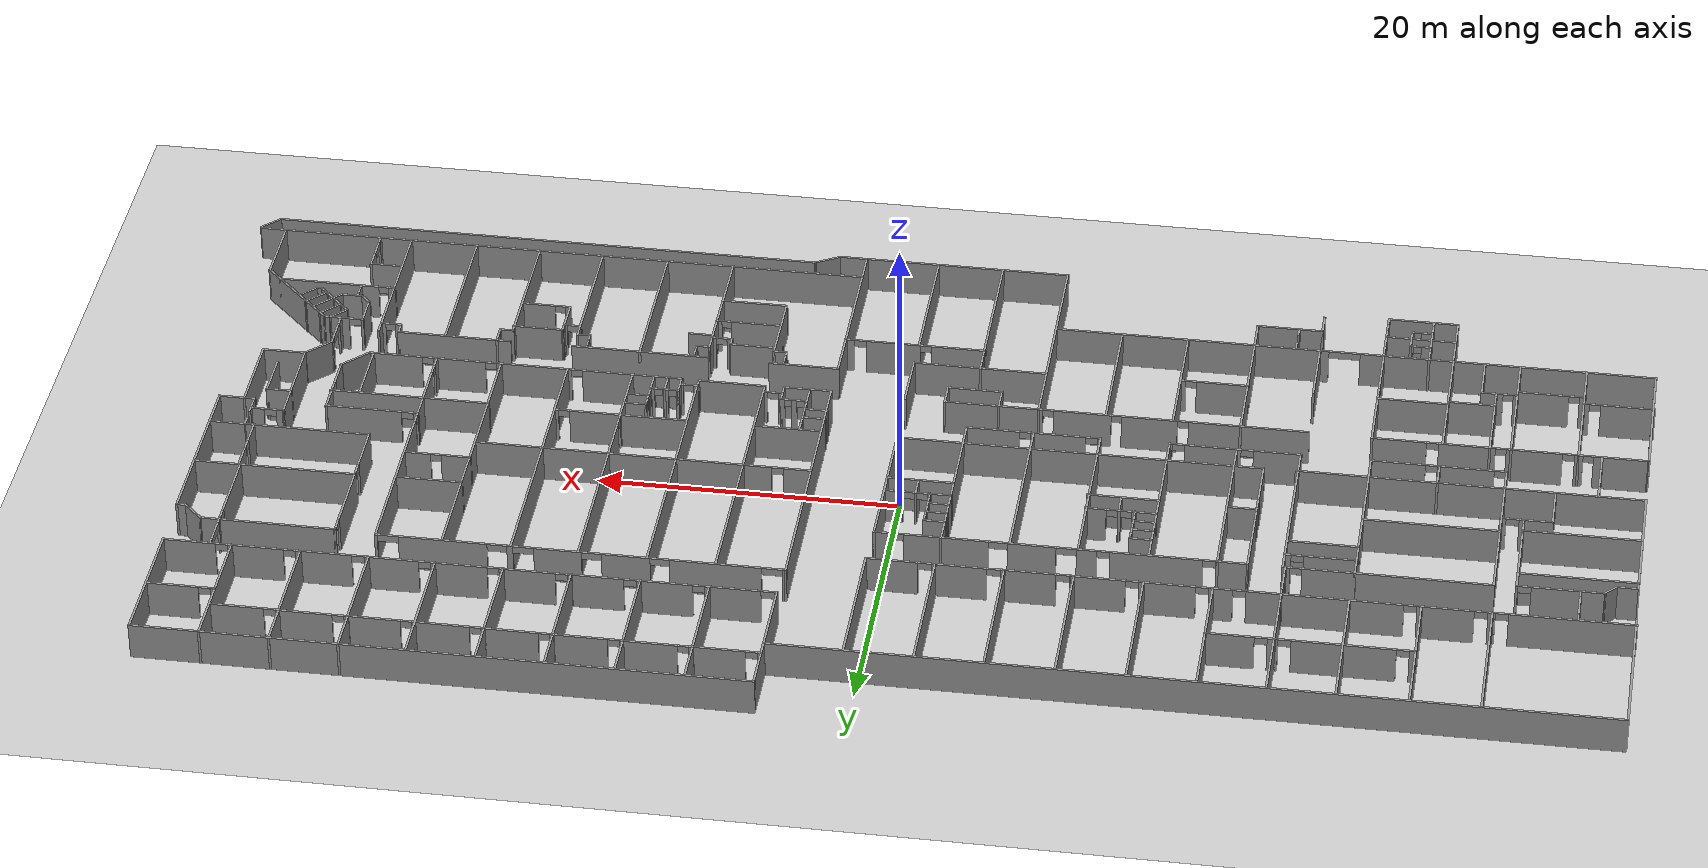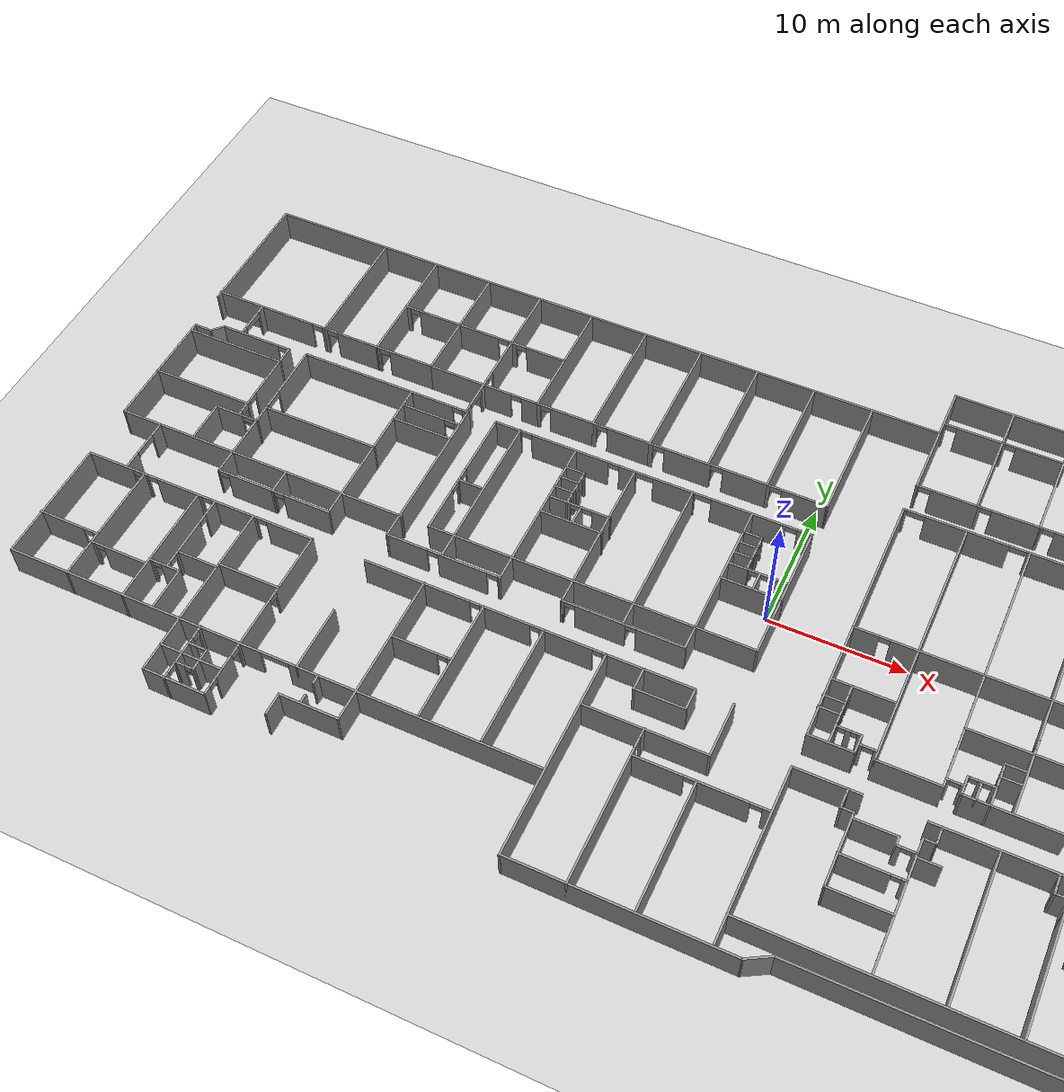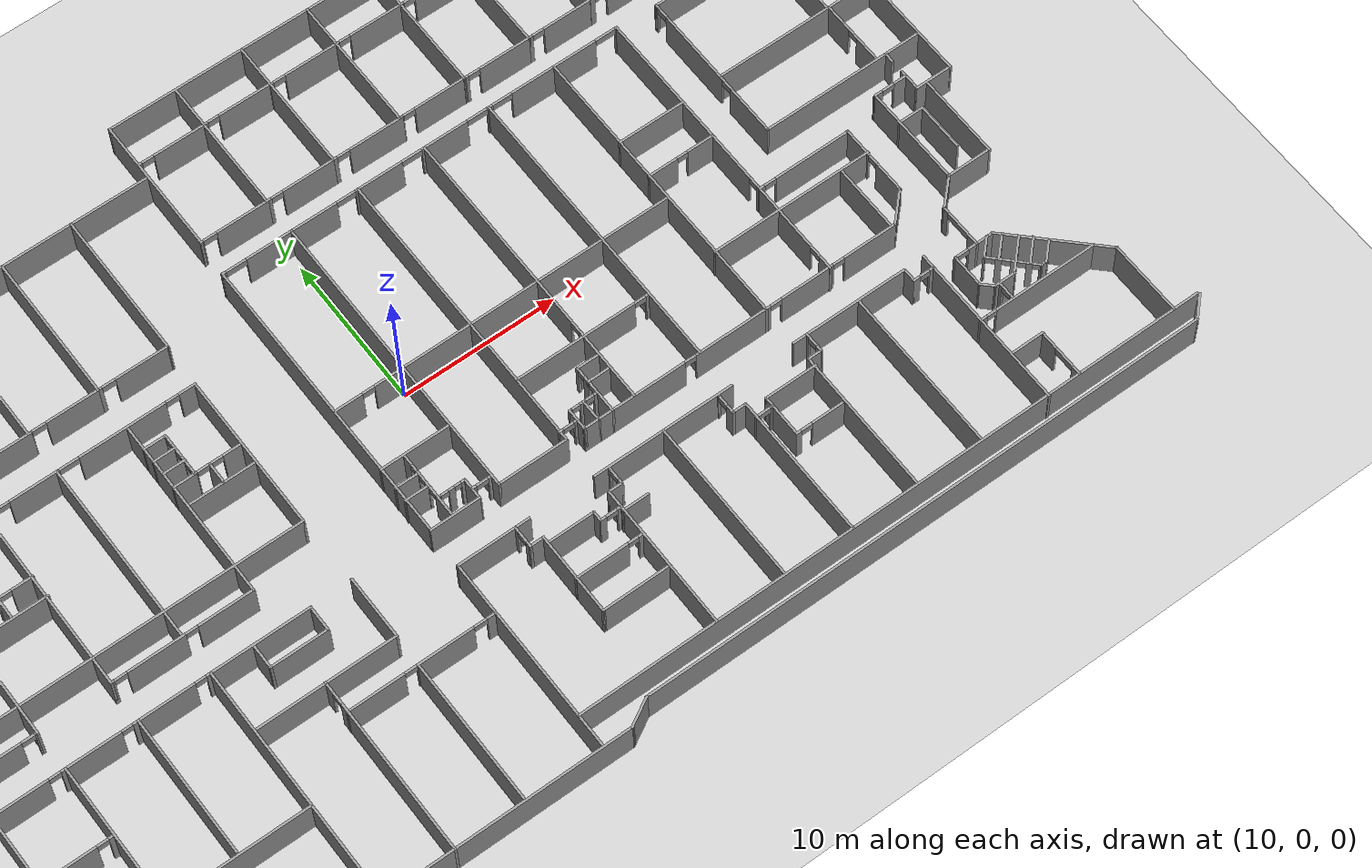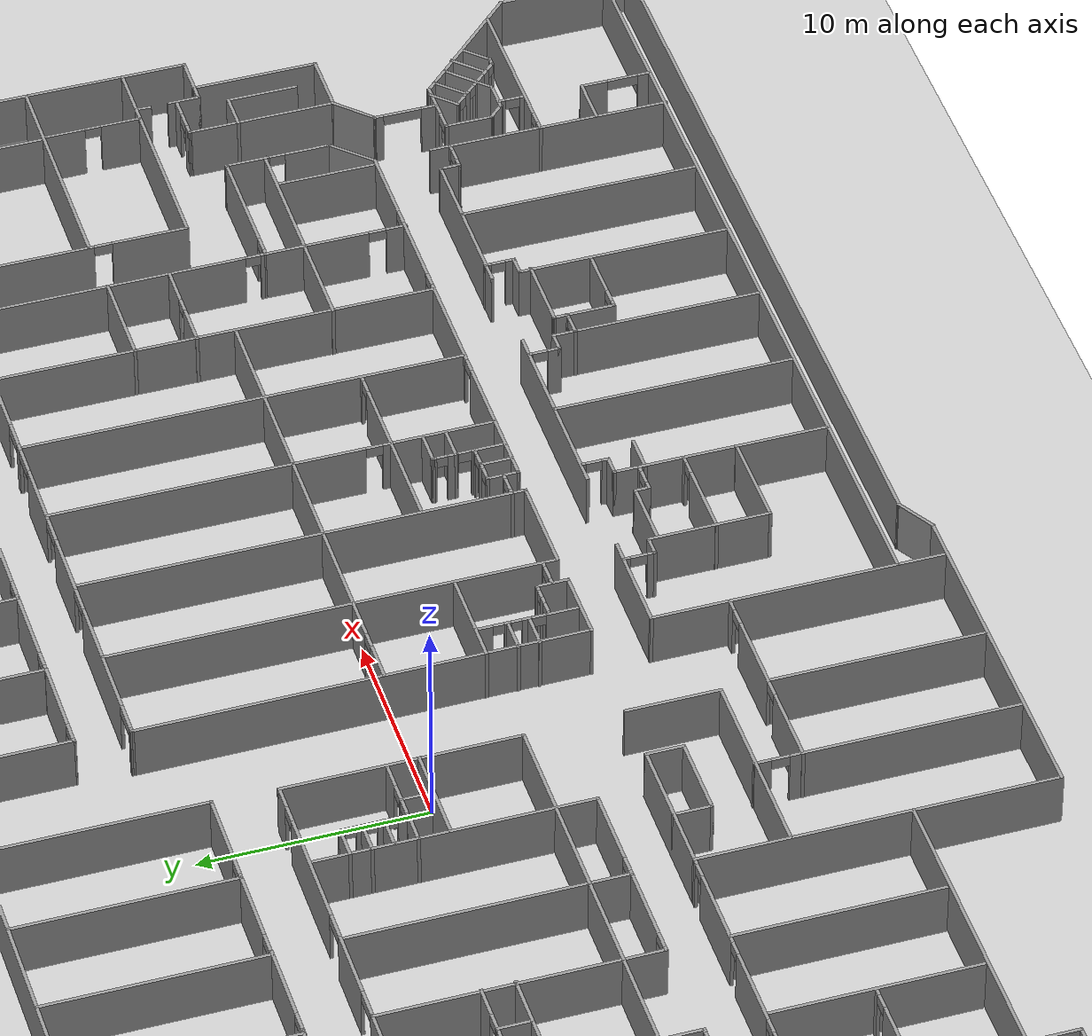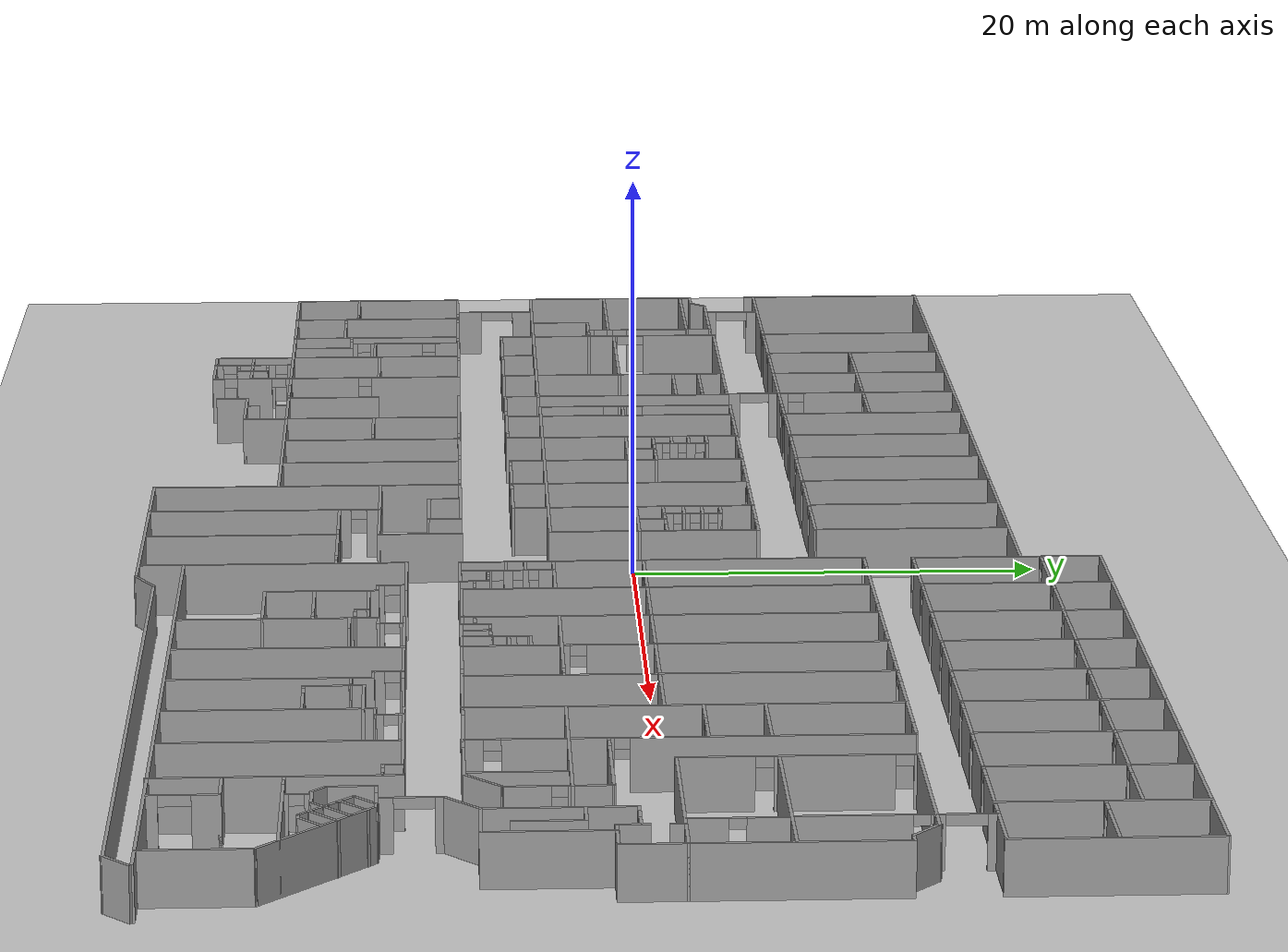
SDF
<sdf version="1.7">
 <world name="default">
  <light name="sun" type="directional">
   <pose>0 0 10 0 -0 0</pose>
   <diffuse>0.8 0.8 0.8 1</diffuse>
   <specular>0.2 0.2 0.2 1</specular>
   <attenuation>
    <range>1000</range>
    <constant>0.9</constant>
    <linear>0.01</linear>
    <quadratic>0.001</quadratic>
   </attenuation>
   <direction>-0.5 0.1 -0.9</direction>
   <spot><inner_angle>0</inner_angle><outer_angle>0</outer_angle><falloff>0</falloff></spot>
  </light>
  <model name="ground_plane">
   <static>1</static>
   <link name="link">
    <collision name="collision">
     <geometry><plane><normal>0 0 1</normal><size>100 100</size></plane></geometry>
     <surface>
      <contact><collide_bitmask>65535</collide_bitmask></contact>
      <friction><ode><mu>100</mu><mu2>50</mu2></ode></friction>
     </surface>
    </collision>
    <visual name="visual">
     <cast_shadows>0</cast_shadows>
     <geometry><plane><normal>0 0 1</normal><size>100 100</size></plane></geometry>
     <material>
      <script><uri>file://media/materials/scripts/gazebo.material</uri><name>Gazebo/Grey</name></script>
     </material>
    </visual>
   </link>
  </model>
  <gravity>0 0 -9.8</gravity>
  <magnetic_field>6e-06 2.3e-05 -4.2e-05</magnetic_field>
  <atmosphere type="adiabatic"/>
  <physics type="ode">
   <max_step_size>0.001</max_step_size>
   <real_time_factor>1</real_time_factor>
   <real_time_update_rate>1000</real_time_update_rate>
  </physics>
  <scene><ambient>0.4 0.4 0.4 1</ambient><background>0.7 0.7 0.7 1</background><shadows>1</shadows></scene>
  <spherical_coordinates>
   <surface_model>EARTH_WGS84</surface_model>
   <latitude_deg>0</latitude_deg>
   <longitude_deg>0</longitude_deg>
   <elevation>0</elevation>
   <heading_deg>0</heading_deg>
  </spherical_coordinates>
  <model name="anglo_3_andar">
   <pose>-0.36557 -0.844839 0 0 -0 0</pose>
   <link name="Wall_100">
    <collision name="Wall_100_Collision">
     <geometry><box><size>9.75 0.15 2.5</size></box></geometry>
     <pose>0 0 1.25 0 -0 0</pose>
    </collision>
    <visual name="Wall_100_Visual">
     <pose>0 0 1.25 0 -0 0</pose>
     <geometry><box><size>9.75 0.15 2.5</size></box></geometry>
     <material>
      <script><uri>file://media/materials/scripts/gazebo.material</uri><name>Gazebo/Grey</name></script>
      <ambient>1 1 1 1</ambient>
     </material>
     <meta><layer>0</layer></meta>
    </visual>
    <pose>-16.5823 14.6737 0 0 -0 -1.5708</pose>
   </link>
   <link name="Wall_102">
    <pose>-14.2823 9.87368 0 0 -0 0</pose>
    <visual name="Wall_102_Visual_0">
     <pose>-2.195 0 1.25 0 -0 0</pose>
     <geometry><box><size>0.360001 0.15 2.5</size></box></geometry>
     <material>
      <script><uri>file://media/materials/scripts/gazebo.material</uri><name>Gazebo/Grey</name></script>
      <ambient>1 1 1 1</ambient>
     </material>
     <meta><layer>0</layer></meta>
    </visual>
    <collision name="Wall_102_Collision_0">
     <geometry><box><size>0.360001 0.15 2.5</size></box></geometry>
     <pose>-2.195 0 1.25 0 -0 0</pose>
    </collision>
    <visual name="Wall_102_Visual_1">
     <pose>0.61 0 1.25 0 -0 0</pose>
     <geometry><box><size>3.53 0.15 2.5</size></box></geometry>
     <material>
      <script><uri>file://media/materials/scripts/gazebo.material</uri><name>Gazebo/Grey</name></script>
      <ambient>1 1 1 1</ambient>
     </material>
     <meta><layer>0</layer></meta>
    </visual>
    <collision name="Wall_102_Collision_1">
     <geometry><box><size>3.53 0.15 2.5</size></box></geometry>
     <pose>0.61 0 1.25 0 -0 0</pose>
    </collision>
    <visual name="Wall_102_Visual_2">
     <pose>-1.585 0 2.25 0 -0 0</pose>
     <geometry><box><size>0.86 0.15 0.5</size></box></geometry>
     <material>
      <script><uri>file://media/materials/scripts/gazebo.material</uri><name>Gazebo/Grey</name></script>
      <ambient>1 1 1 1</ambient>
     </material>
     <meta><layer>0</layer></meta>
    </visual>
    <collision name="Wall_102_Collision_2">
     <geometry><box><size>0.86 0.15 0.5</size></box></geometry>
     <pose>-1.585 0 2.25 0 -0 0</pose>
    </collision>
   </link>
   <link name="Wall_104">
    <collision name="Wall_104_Collision">
     <geometry><box><size>9.75 0.15 2.5</size></box></geometry>
     <pose>0 0 1.25 0 -0 0</pose>
    </collision>
    <visual name="Wall_104_Visual">
     <pose>0 0 1.25 0 -0 0</pose>
     <geometry><box><size>9.75 0.15 2.5</size></box></geometry>
     <material>
      <script><uri>file://media/materials/scripts/gazebo.material</uri><name>Gazebo/Grey</name></script>
      <ambient>1 1 1 1</ambient>
     </material>
     <meta><layer>0</layer></meta>
    </visual>
    <pose>-21.0123 14.6737 0 0 -0 -1.5708</pose>
   </link>
   <link name="Wall_106">
    <pose>-18.7973 9.87368 0 0 -0 0</pose>
    <visual name="Wall_106_Visual_0">
     <pose>-2.13 0 1.25 0 -0 0</pose>
     <geometry><box><size>0.319999 0.15 2.5</size></box></geometry>
     <material>
      <script><uri>file://media/materials/scripts/gazebo.material</uri><name>Gazebo/Grey</name></script>
      <ambient>1 1 1 1</ambient>
     </material>
     <meta><layer>0</layer></meta>
    </visual>
    <collision name="Wall_106_Collision_0">
     <geometry><box><size>0.319999 0.15 2.5</size></box></geometry>
     <pose>-2.13 0 1.25 0 -0 0</pose>
    </collision>
    <visual name="Wall_106_Visual_1">
     <pose>0.579999 0 1.25 0 -0 0</pose>
     <geometry><box><size>3.42 0.15 2.5</size></box></geometry>
     <material>
      <script><uri>file://media/materials/scripts/gazebo.material</uri><name>Gazebo/Grey</name></script>
      <ambient>1 1 1 1</ambient>
     </material>
     <meta><layer>0</layer></meta>
    </visual>
    <collision name="Wall_106_Collision_1">
     <geometry><box><size>3.42 0.15 2.5</size></box></geometry>
     <pose>0.579999 0 1.25 0 -0 0</pose>
    </collision>
    <visual name="Wall_106_Visual_2">
     <pose>-1.55 0 2.25 0 -0 0</pose>
     <geometry><box><size>0.84 0.15 0.5</size></box></geometry>
     <material>
      <script><uri>file://media/materials/scripts/gazebo.material</uri><name>Gazebo/Grey</name></script>
      <ambient>1 1 1 1</ambient>
     </material>
     <meta><layer>0</layer></meta>
    </visual>
    <collision name="Wall_106_Collision_2">
     <geometry><box><size>0.84 0.15 0.5</size></box></geometry>
     <pose>-1.55 0 2.25 0 -0 0</pose>
    </collision>
   </link>
   <link name="Wall_108">
    <pose>-25.3623 14.6637 0 0 -0 -1.5708</pose>
    <visual name="Wall_108_Visual_0">
     <pose>-0.73 0 1.25 0 -0 0</pose>
     <geometry><box><size>8.29 0.15 2.5</size></box></geometry>
     <material>
      <script><uri>file://media/materials/scripts/gazebo.material</uri><name>Gazebo/Grey</name></script>
      <ambient>1 1 1 1</ambient>
     </material>
     <meta><layer>0</layer></meta>
    </visual>
    <collision name="Wall_108_Collision_0">
     <geometry><box><size>8.29 0.15 2.5</size></box></geometry>
     <pose>-0.73 0 1.25 0 -0 0</pose>
    </collision>
    <visual name="Wall_108_Visual_1">
     <pose>4.57 0 1.25 0 -0 0</pose>
     <geometry><box><size>0.61 0.15 2.5</size></box></geometry>
     <material>
      <script><uri>file://media/materials/scripts/gazebo.material</uri><name>Gazebo/Grey</name></script>
      <ambient>1 1 1 1</ambient>
     </material>
     <meta><layer>0</layer></meta>
    </visual>
    <collision name="Wall_108_Collision_1">
     <geometry><box><size>0.61 0.15 2.5</size></box></geometry>
     <pose>4.57 0 1.25 0 -0 0</pose>
    </collision>
    <visual name="Wall_108_Visual_2">
     <pose>3.84 0 2.25 0 -0 0</pose>
     <geometry><box><size>0.85 0.15 0.5</size></box></geometry>
     <material>
      <script><uri>file://media/materials/scripts/gazebo.material</uri><name>Gazebo/Grey</name></script>
      <ambient>1 1 1 1</ambient>
     </material>
     <meta><layer>0</layer></meta>
    </visual>
    <collision name="Wall_108_Collision_2">
     <geometry><box><size>0.85 0.15 0.5</size></box></geometry>
     <pose>3.84 0 2.25 0 -0 0</pose>
    </collision>
   </link>
   <link name="Wall_11">
    <collision name="Wall_11_Collision">
     <geometry><box><size>9.25 0.15 2.5</size></box></geometry>
     <pose>0 0 1.25 0 -0 0</pose>
    </collision>
    <visual name="Wall_11_Visual">
     <pose>0 0 1.25 0 -0 0</pose>
     <geometry><box><size>9.25 0.15 2.5</size></box></geometry>
     <material>
      <script><uri>file://media/materials/scripts/gazebo.material</uri><name>Gazebo/Grey</name></script>
      <ambient>1 1 1 1</ambient>
     </material>
     <meta><layer>0</layer></meta>
    </visual>
    <pose>41.6877 18.8137 0 0 -0 -1.5708</pose>
   </link>
   <link name="Wall_110">
    <pose>-23.2173 14.5137 0 0 -0 0</pose>
    <visual name="Wall_110_Visual_0">
     <pose>-1.9875 0 1.25 0 -0 0</pose>
     <geometry><box><size>0.524999 0.15 2.5</size></box></geometry>
     <material>
      <script><uri>file://media/materials/scripts/gazebo.material</uri><name>Gazebo/Grey</name></script>
      <ambient>1 1 1 1</ambient>
     </material>
     <meta><layer>0</layer></meta>
    </visual>
    <collision name="Wall_110_Collision_0">
     <geometry><box><size>0.524999 0.15 2.5</size></box></geometry>
     <pose>-1.9875 0 1.25 0 -0 0</pose>
    </collision>
    <visual name="Wall_110_Visual_1">
     <pose>0.6725 0 1.25 0 -0 0</pose>
     <geometry><box><size>3.155 0.15 2.5</size></box></geometry>
     <material>
      <script><uri>file://media/materials/scripts/gazebo.material</uri><name>Gazebo/Grey</name></script>
      <ambient>1 1 1 1</ambient>
     </material>
     <meta><layer>0</layer></meta>
    </visual>
    <collision name="Wall_110_Collision_1">
     <geometry><box><size>3.155 0.15 2.5</size></box></geometry>
     <pose>0.6725 0 1.25 0 -0 0</pose>
    </collision>
    <visual name="Wall_110_Visual_2">
     <pose>-1.315 0 2.25 0 -0 0</pose>
     <geometry><box><size>0.82 0.15 0.5</size></box></geometry>
     <material>
      <script><uri>file://media/materials/scripts/gazebo.material</uri><name>Gazebo/Grey</name></script>
      <ambient>1 1 1 1</ambient>
     </material>
     <meta><layer>0</layer></meta>
    </visual>
    <collision name="Wall_110_Collision_2">
     <geometry><box><size>0.82 0.15 0.5</size></box></geometry>
     <pose>-1.315 0 2.25 0 -0 0</pose>
    </collision>
   </link>
   <link name="Wall_112">
    <pose>-23.1873 9.86868 0 0 -0 0.002299</pose>
    <visual name="Wall_112_Visual_0">
     <pose>-1.10011 0 1.25 0 -0 0</pose>
     <geometry><box><size>2.29978 0.15 2.5</size></box></geometry>
     <material>
      <script><uri>file://media/materials/scripts/gazebo.material</uri><name>Gazebo/Grey</name></script>
      <ambient>1 1 1 1</ambient>
     </material>
     <meta><layer>0</layer></meta>
    </visual>
    <collision name="Wall_112_Collision_0">
     <geometry><box><size>2.29978 0.15 2.5</size></box></geometry>
     <pose>-1.10011 0 1.25 0 -0 0</pose>
    </collision>
    <visual name="Wall_112_Visual_1">
     <pose>1.56989 0 1.25 0 -0 0</pose>
     <geometry><box><size>1.36023 0.15 2.5</size></box></geometry>
     <material>
      <script><uri>file://media/materials/scripts/gazebo.material</uri><name>Gazebo/Grey</name></script>
      <ambient>1 1 1 1</ambient>
     </material>
     <meta><layer>0</layer></meta>
    </visual>
    <collision name="Wall_112_Collision_1">
     <geometry><box><size>1.36023 0.15 2.5</size></box></geometry>
     <pose>1.56989 0 1.25 0 -0 0</pose>
    </collision>
    <visual name="Wall_112_Visual_2">
     <pose>0.469779 0 2.25 0 -0 0</pose>
     <geometry><box><size>0.84 0.15 0.5</size></box></geometry>
     <material>
      <script><uri>file://media/materials/scripts/gazebo.material</uri><name>Gazebo/Grey</name></script>
      <ambient>1 1 1 1</ambient>
     </material>
     <meta><layer>0</layer></meta>
    </visual>
    <collision name="Wall_112_Collision_2">
     <geometry><box><size>0.84 0.15 0.5</size></box></geometry>
     <pose>0.469779 0 2.25 0 -0 0</pose>
    </collision>
   </link>
   <link name="Wall_114">
    <collision name="Wall_114_Collision">
     <geometry><box><size>9.75 0.15 2.5</size></box></geometry>
     <pose>0 0 1.25 0 -0 0</pose>
    </collision>
    <visual name="Wall_114_Visual">
     <pose>0 0 1.25 0 -0 0</pose>
     <geometry><box><size>9.75 0.15 2.5</size></box></geometry>
     <material>
      <script><uri>file://media/materials/scripts/gazebo.material</uri><name>Gazebo/Grey</name></script>
      <ambient>1 1 1 1</ambient>
     </material>
     <meta><layer>0</layer></meta>
    </visual>
    <pose>-29.7023 14.6737 0 0 -0 -1.5708</pose>
   </link>
   <link name="Wall_116">
    <pose>-27.5673 14.5137 0 0 -0 0</pose>
    <visual name="Wall_116_Visual_0">
     <pose>-0.565 0 1.25 0 -0 0</pose>
     <geometry><box><size>3.37 0.15 2.5</size></box></geometry>
     <material>
      <script><uri>file://media/materials/scripts/gazebo.material</uri><name>Gazebo/Grey</name></script>
      <ambient>1 1 1 1</ambient>
     </material>
     <meta><layer>0</layer></meta>
    </visual>
    <collision name="Wall_116_Collision_0">
     <geometry><box><size>3.37 0.15 2.5</size></box></geometry>
     <pose>-0.565 0 1.25 0 -0 0</pose>
    </collision>
    <visual name="Wall_116_Visual_1">
     <pose>2.1 0 1.25 0 -0 0</pose>
     <geometry><box><size>0.3 0.15 2.5</size></box></geometry>
     <material>
      <script><uri>file://media/materials/scripts/gazebo.material</uri><name>Gazebo/Grey</name></script>
      <ambient>1 1 1 1</ambient>
     </material>
     <meta><layer>0</layer></meta>
    </visual>
    <collision name="Wall_116_Collision_1">
     <geometry><box><size>0.3 0.15 2.5</size></box></geometry>
     <pose>2.1 0 1.25 0 -0 0</pose>
    </collision>
    <visual name="Wall_116_Visual_2">
     <pose>1.535 0 2.25 0 -0 0</pose>
     <geometry><box><size>0.83 0.15 0.5</size></box></geometry>
     <material>
      <script><uri>file://media/materials/scripts/gazebo.material</uri><name>Gazebo/Grey</name></script>
      <ambient>1 1 1 1</ambient>
     </material>
     <meta><layer>0</layer></meta>
    </visual>
    <collision name="Wall_116_Collision_2">
     <geometry><box><size>0.83 0.15 0.5</size></box></geometry>
     <pose>1.535 0 2.25 0 -0 0</pose>
    </collision>
   </link>
   <link name="Wall_118">
    <collision name="Wall_118_Collision">
     <geometry><box><size>4.49001 0.15 2.5</size></box></geometry>
     <pose>0 0 1.25 0 -0 0</pose>
    </collision>
    <visual name="Wall_118_Visual">
     <pose>0 0 1.25 0 -0 0</pose>
     <geometry><box><size>4.49001 0.15 2.5</size></box></geometry>
     <material>
      <script><uri>file://media/materials/scripts/gazebo.material</uri><name>Gazebo/Grey</name></script>
      <ambient>1 1 1 1</ambient>
     </material>
     <meta><layer>0</layer></meta>
    </visual>
    <pose>-27.5323 9.86868 0 0 -0 -0.002304</pose>
   </link>
   <link name="Wall_120">
    <collision name="Wall_120_Collision">
     <geometry><box><size>9.75 0.15 2.5</size></box></geometry>
     <pose>0 0 1.25 0 -0 0</pose>
    </collision>
    <visual name="Wall_120_Visual">
     <pose>0 0 1.25 0 -0 0</pose>
     <geometry><box><size>9.75 0.15 2.5</size></box></geometry>
     <material>
      <script><uri>file://media/materials/scripts/gazebo.material</uri><name>Gazebo/Grey</name></script>
      <ambient>1 1 1 1</ambient>
     </material>
     <meta><layer>0</layer></meta>
    </visual>
    <pose>-34.2723 14.6737 0 0 -0 -1.5708</pose>
   </link>
   <link name="Wall_122">
    <pose>-32.0123 14.5137 0 0 -0 0</pose>
    <visual name="Wall_122_Visual_0">
     <pose>-2.11 0 1.25 0 -0 0</pose>
     <geometry><box><size>0.469999 0.15 2.5</size></box></geometry>
     <material>
      <script><uri>file://media/materials/scripts/gazebo.material</uri><name>Gazebo/Grey</name></script>
      <ambient>1 1 1 1</ambient>
     </material>
     <meta><layer>0</layer></meta>
    </visual>
    <collision name="Wall_122_Collision_0">
     <geometry><box><size>0.469999 0.15 2.5</size></box></geometry>
     <pose>-2.11 0 1.25 0 -0 0</pose>
    </collision>
    <visual name="Wall_122_Visual_1">
     <pose>0.639999 0 1.25 0 -0 0</pose>
     <geometry><box><size>3.41 0.15 2.5</size></box></geometry>
     <material>
      <script><uri>file://media/materials/scripts/gazebo.material</uri><name>Gazebo/Grey</name></script>
      <ambient>1 1 1 1</ambient>
     </material>
     <meta><layer>0</layer></meta>
    </visual>
    <collision name="Wall_122_Collision_1">
     <geometry><box><size>3.41 0.15 2.5</size></box></geometry>
     <pose>0.639999 0 1.25 0 -0 0</pose>
    </collision>
    <visual name="Wall_122_Visual_2">
     <pose>-1.47 0 2.25 0 -0 0</pose>
     <geometry><box><size>0.81 0.15 0.5</size></box></geometry>
     <material>
      <script><uri>file://media/materials/scripts/gazebo.material</uri><name>Gazebo/Grey</name></script>
      <ambient>1 1 1 1</ambient>
     </material>
     <meta><layer>0</layer></meta>
    </visual>
    <collision name="Wall_122_Collision_2">
     <geometry><box><size>0.81 0.15 0.5</size></box></geometry>
     <pose>-1.47 0 2.25 0 -0 0</pose>
    </collision>
   </link>
   <link name="Wall_127">
    <pose>-31.9873 9.87368 0 0 -0 0</pose>
    <visual name="Wall_127_Visual_0">
     <pose>-2.1825 0 1.25 0 -0 0</pose>
     <geometry><box><size>0.354999 0.15 2.5</size></box></geometry>
     <material>
      <script><uri>file://media/materials/scripts/gazebo.material</uri><name>Gazebo/Grey</name></script>
      <ambient>1 1 1 1</ambient>
     </material>
     <meta><layer>0</layer></meta>
    </visual>
    <collision name="Wall_127_Collision_0">
     <geometry><box><size>0.354999 0.15 2.5</size></box></geometry>
     <pose>-2.1825 0 1.25 0 -0 0</pose>
    </collision>
    <visual name="Wall_127_Visual_1">
     <pose>0.587499 0 1.25 0 -0 0</pose>
     <geometry><box><size>3.545 0.15 2.5</size></box></geometry>
     <material>
      <script><uri>file://media/materials/scripts/gazebo.material</uri><name>Gazebo/Grey</name></script>
      <ambient>1 1 1 1</ambient>
     </material>
     <meta><layer>0</layer></meta>
    </visual>
    <collision name="Wall_127_Collision_1">
     <geometry><box><size>3.545 0.15 2.5</size></box></geometry>
     <pose>0.587499 0 1.25 0 -0 0</pose>
    </collision>
    <visual name="Wall_127_Visual_2">
     <pose>-1.595 0 2.25 0 -0 0</pose>
     <geometry><box><size>0.82 0.15 0.5</size></box></geometry>
     <material>
      <script><uri>file://media/materials/scripts/gazebo.material</uri><name>Gazebo/Grey</name></script>
      <ambient>1 1 1 1</ambient>
     </material>
     <meta><layer>0</layer></meta>
    </visual>
    <collision name="Wall_127_Collision_2">
     <geometry><box><size>0.82 0.15 0.5</size></box></geometry>
     <pose>-1.595 0 2.25 0 -0 0</pose>
    </collision>
   </link>
   <link name="Wall_129">
    <collision name="Wall_129_Collision">
     <geometry><box><size>9.75 0.15 2.5</size></box></geometry>
     <pose>0 0 1.25 0 -0 0</pose>
    </collision>
    <visual name="Wall_129_Visual">
     <pose>0 0 1.25 0 -0 0</pose>
     <geometry><box><size>9.75 0.15 2.5</size></box></geometry>
     <material>
      <script><uri>file://media/materials/scripts/gazebo.material</uri><name>Gazebo/Grey</name></script>
      <ambient>1 1 1 1</ambient>
     </material>
     <meta><layer>0</layer></meta>
    </visual>
    <pose>-38.7623 14.6837 0 0 -0 -1.5708</pose>
   </link>
   <link name="Wall_13">
    <pose>43.8627 14.2737 0 0 -0 0</pose>
    <visual name="Wall_13_Visual_0">
     <pose>-2.08 0 1.25 0 -0 0</pose>
     <geometry><box><size>0.34 0.15 2.5</size></box></geometry>
     <material>
      <script><uri>file://media/materials/scripts/gazebo.material</uri><name>Gazebo/Grey</name></script>
      <ambient>1 1 1 1</ambient>
     </material>
     <meta><layer>0</layer></meta>
    </visual>
    <collision name="Wall_13_Collision_0">
     <geometry><box><size>0.34 0.15 2.5</size></box></geometry>
     <pose>-2.08 0 1.25 0 -0 0</pose>
    </collision>
    <visual name="Wall_13_Visual_1">
     <pose>0.56 0 1.25 0 -0 0</pose>
     <geometry><box><size>3.38 0.15 2.5</size></box></geometry>
     <material>
      <script><uri>file://media/materials/scripts/gazebo.material</uri><name>Gazebo/Grey</name></script>
      <ambient>1 1 1 1</ambient>
     </material>
     <meta><layer>0</layer></meta>
    </visual>
    <collision name="Wall_13_Collision_1">
     <geometry><box><size>3.38 0.15 2.5</size></box></geometry>
     <pose>0.56 0 1.25 0 -0 0</pose>
    </collision>
    <visual name="Wall_13_Visual_2">
     <pose>-1.52 0 2.25 0 -0 0</pose>
     <geometry><box><size>0.78 0.15 0.5</size></box></geometry>
     <material>
      <script><uri>file://media/materials/scripts/gazebo.material</uri><name>Gazebo/Grey</name></script>
      <ambient>1 1 1 1</ambient>
     </material>
     <meta><layer>0</layer></meta>
    </visual>
    <collision name="Wall_13_Collision_2">
     <geometry><box><size>0.78 0.15 0.5</size></box></geometry>
     <pose>-1.52 0 2.25 0 -0 0</pose>
    </collision>
   </link>
   <link name="Wall_134">
    <pose>-36.5173 9.87868 0 0 -0 -0.002227</pose>
    <visual name="Wall_134_Visual_0">
     <pose>-2.14494 0 1.25 0 -0 0</pose>
     <geometry><box><size>0.350134 0.15 2.5</size></box></geometry>
     <material>
      <script><uri>file://media/materials/scripts/gazebo.material</uri><name>Gazebo/Grey</name></script>
      <ambient>1 1 1 1</ambient>
     </material>
     <meta><layer>0</layer></meta>
    </visual>
    <collision name="Wall_134_Collision_0">
     <geometry><box><size>0.350134 0.15 2.5</size></box></geometry>
     <pose>-2.14494 0 1.25 0 -0 0</pose>
    </collision>
    <visual name="Wall_134_Visual_1">
     <pose>0.605067 0 1.25 0 -0 0</pose>
     <geometry><box><size>3.42988 0.15 2.5</size></box></geometry>
     <material>
      <script><uri>file://media/materials/scripts/gazebo.material</uri><name>Gazebo/Grey</name></script>
      <ambient>1 1 1 1</ambient>
     </material>
     <meta><layer>0</layer></meta>
    </visual>
    <collision name="Wall_134_Collision_1">
     <geometry><box><size>3.42988 0.15 2.5</size></box></geometry>
     <pose>0.605067 0 1.25 0 -0 0</pose>
    </collision>
    <visual name="Wall_134_Visual_2">
     <pose>-1.53987 0 2.25 0 -0 0</pose>
     <geometry><box><size>0.86 0.15 0.5</size></box></geometry>
     <material>
      <script><uri>file://media/materials/scripts/gazebo.material</uri><name>Gazebo/Grey</name></script>
      <ambient>1 1 1 1</ambient>
     </material>
     <meta><layer>0</layer></meta>
    </visual>
    <collision name="Wall_134_Collision_2">
     <geometry><box><size>0.86 0.15 0.5</size></box></geometry>
     <pose>-1.53987 0 2.25 0 -0 0</pose>
    </collision>
   </link>
   <link name="Wall_136">
    <collision name="Wall_136_Collision">
     <geometry><box><size>10.25 0.15 2.5</size></box></geometry>
     <pose>0 0 1.25 0 -0 0</pose>
    </collision>
    <visual name="Wall_136_Visual">
     <pose>0 0 1.25 0 -0 0</pose>
     <geometry><box><size>10.25 0.15 2.5</size></box></geometry>
     <material>
      <script><uri>file://media/materials/scripts/gazebo.material</uri><name>Gazebo/Grey</name></script>
      <ambient>1 1 1 1</ambient>
     </material>
     <meta><layer>0</layer></meta>
    </visual>
    <pose>-47.8223 14.4537 0 0 -0 -1.5708</pose>
   </link>
   <link name="Wall_141">
    <pose>-43.3123 9.88368 0 0 -0 3.14159</pose>
    <visual name="Wall_141_Visual_0">
     <pose>-4.4925 0 1.25 0 -0 0</pose>
     <geometry><box><size>0.265001 0.15 2.5</size></box></geometry>
     <material>
      <script><uri>file://media/materials/scripts/gazebo.material</uri><name>Gazebo/Grey</name></script>
      <ambient>1 1 1 1</ambient>
     </material>
     <meta><layer>0</layer></meta>
    </visual>
    <collision name="Wall_141_Collision_0">
     <geometry><box><size>0.265001 0.15 2.5</size></box></geometry>
     <pose>-4.4925 0 1.25 0 -0 0</pose>
    </collision>
    <visual name="Wall_141_Visual_1">
     <pose>0.552501 0 1.25 0 -0 0</pose>
     <geometry><box><size>8.145 0.15 2.5</size></box></geometry>
     <material>
      <script><uri>file://media/materials/scripts/gazebo.material</uri><name>Gazebo/Grey</name></script>
      <ambient>1 1 1 1</ambient>
     </material>
     <meta><layer>0</layer></meta>
    </visual>
    <collision name="Wall_141_Collision_1">
     <geometry><box><size>8.145 0.15 2.5</size></box></geometry>
     <pose>0.552501 0 1.25 0 -0 0</pose>
    </collision>
    <visual name="Wall_141_Visual_2">
     <pose>-3.94 0 2.25 0 -0 0</pose>
     <geometry><box><size>0.84 0.15 0.5</size></box></geometry>
     <material>
      <script><uri>file://media/materials/scripts/gazebo.material</uri><name>Gazebo/Grey</name></script>
      <ambient>1 1 1 1</ambient>
     </material>
     <meta><layer>0</layer></meta>
    </visual>
    <collision name="Wall_141_Collision_2">
     <geometry><box><size>0.84 0.15 0.5</size></box></geometry>
     <pose>-3.94 0 2.25 0 -0 0</pose>
    </collision>
   </link>
   <link name="Wall_143">
    <pose>-44.1623 8.42868 0 0 -0 -1.5708</pose>
    <visual name="Wall_143_Visual_0">
     <pose>-1.155 0 1.25 0 -0 0</pose>
     <geometry><box><size>0.69 0.15 2.5</size></box></geometry>
     <material>
      <script><uri>file://media/materials/scripts/gazebo.material</uri><name>Gazebo/Grey</name></script>
      <ambient>1 1 1 1</ambient>
     </material>
     <meta><layer>0</layer></meta>
    </visual>
    <collision name="Wall_143_Collision_0">
     <geometry><box><size>0.69 0.15 2.5</size></box></geometry>
     <pose>-1.155 0 1.25 0 -0 0</pose>
    </collision>
    <visual name="Wall_143_Visual_1">
     <pose>1.24 0 1.25 0 -0 0</pose>
     <geometry><box><size>0.52 0.15 2.5</size></box></geometry>
     <material>
      <script><uri>file://media/materials/scripts/gazebo.material</uri><name>Gazebo/Grey</name></script>
      <ambient>1 1 1 1</ambient>
     </material>
     <meta><layer>0</layer></meta>
    </visual>
    <collision name="Wall_143_Collision_1">
     <geometry><box><size>0.52 0.15 2.5</size></box></geometry>
     <pose>1.24 0 1.25 0 -0 0</pose>
    </collision>
    <visual name="Wall_143_Visual_2">
     <pose>0.085 0 2.25 0 -0 0</pose>
     <geometry><box><size>1.79 0.15 0.5</size></box></geometry>
     <material>
      <script><uri>file://media/materials/scripts/gazebo.material</uri><name>Gazebo/Grey</name></script>
      <ambient>1 1 1 1</ambient>
     </material>
     <meta><layer>0</layer></meta>
    </visual>
    <collision name="Wall_143_Collision_2">
     <geometry><box><size>1.79 0.15 0.5</size></box></geometry>
     <pose>0.085 0 2.25 0 -0 0</pose>
    </collision>
   </link>
   <link name="Wall_15">
    <pose>43.8727 18.9037 0 0 -0 0</pose>
    <visual name="Wall_15_Visual_0">
     <pose>-2.065 0 1.25 0 -0 0</pose>
     <geometry><box><size>0.370002 0.15 2.5</size></box></geometry>
     <material>
      <script><uri>file://media/materials/scripts/gazebo.material</uri><name>Gazebo/Grey</name></script>
      <ambient>1 1 1 1</ambient>
     </material>
     <meta><layer>0</layer></meta>
    </visual>
    <collision name="Wall_15_Collision_0">
     <geometry><box><size>0.370002 0.15 2.5</size></box></geometry>
     <pose>-2.065 0 1.25 0 -0 0</pose>
    </collision>
    <visual name="Wall_15_Visual_1">
     <pose>0.575001 0 1.25 0 -0 0</pose>
     <geometry><box><size>3.35 0.15 2.5</size></box></geometry>
     <material>
      <script><uri>file://media/materials/scripts/gazebo.material</uri><name>Gazebo/Grey</name></script>
      <ambient>1 1 1 1</ambient>
     </material>
     <meta><layer>0</layer></meta>
    </visual>
    <collision name="Wall_15_Collision_1">
     <geometry><box><size>3.35 0.15 2.5</size></box></geometry>
     <pose>0.575001 0 1.25 0 -0 0</pose>
    </collision>
    <visual name="Wall_15_Visual_2">
     <pose>-1.49 0 2.25 0 -0 0</pose>
     <geometry><box><size>0.78 0.15 0.5</size></box></geometry>
     <material>
      <script><uri>file://media/materials/scripts/gazebo.material</uri><name>Gazebo/Grey</name></script>
      <ambient>1 1 1 1</ambient>
     </material>
     <meta><layer>0</layer></meta>
    </visual>
    <collision name="Wall_15_Collision_2">
     <geometry><box><size>0.78 0.15 0.5</size></box></geometry>
     <pose>-1.49 0 2.25 0 -0 0</pose>
    </collision>
   </link>
   <link name="Wall_150">
    <pose>-42.8923 6.87368 0 0 -0 3.14159</pose>
    <visual name="Wall_150_Visual_0">
     <pose>-2.8225 0 1.25 0 -0 0</pose>
     <geometry><box><size>0.105 0.15 2.5</size></box></geometry>
     <material>
      <script><uri>file://media/materials/scripts/gazebo.material</uri><name>Gazebo/Grey</name></script>
      <ambient>1 1 1 1</ambient>
     </material>
     <meta><layer>0</layer></meta>
    </visual>
    <collision name="Wall_150_Collision_0">
     <geometry><box><size>0.105 0.15 2.5</size></box></geometry>
     <pose>-2.8225 0 1.25 0 -0 0</pose>
    </collision>
    <visual name="Wall_150_Visual_1">
     <pose>0.5025 0 1.25 0 -0 0</pose>
     <geometry><box><size>4.745 0.15 2.5</size></box></geometry>
     <material>
      <script><uri>file://media/materials/scripts/gazebo.material</uri><name>Gazebo/Grey</name></script>
      <ambient>1 1 1 1</ambient>
     </material>
     <meta><layer>0</layer></meta>
    </visual>
    <collision name="Wall_150_Collision_1">
     <geometry><box><size>4.745 0.15 2.5</size></box></geometry>
     <pose>0.5025 0 1.25 0 -0 0</pose>
    </collision>
    <visual name="Wall_150_Visual_2">
     <pose>-2.32 0 2.25 0 -0 0</pose>
     <geometry><box><size>0.9 0.15 0.5</size></box></geometry>
     <material>
      <script><uri>file://media/materials/scripts/gazebo.material</uri><name>Gazebo/Grey</name></script>
      <ambient>1 1 1 1</ambient>
     </material>
     <meta><layer>0</layer></meta>
    </visual>
    <collision name="Wall_150_Collision_2">
     <geometry><box><size>0.9 0.15 0.5</size></box></geometry>
     <pose>-2.32 0 2.25 0 -0 0</pose>
    </collision>
   </link>
   <link name="Wall_151">
    <collision name="Wall_151_Collision">
     <geometry><box><size>1.21523 0.15 2.5</size></box></geometry>
     <pose>0 0 1.25 0 -0 0</pose>
    </collision>
    <visual name="Wall_151_Visual">
     <pose>0 0 1.25 0 -0 0</pose>
     <geometry><box><size>1.21523 0.15 2.5</size></box></geometry>
     <material>
      <script><uri>file://media/materials/scripts/gazebo.material</uri><name>Gazebo/Grey</name></script>
      <ambient>1 1 1 1</ambient>
     </material>
     <meta><layer>0</layer></meta>
    </visual>
    <pose>-46.0562 6.48477 0 0 -0 -2.323</pose>
   </link>
   <link name="Wall_152">
    <collision name="Wall_152_Collision">
     <geometry><box><size>1.5 0.15 2.5</size></box></geometry>
     <pose>0 0 1.25 0 -0 0</pose>
    </collision>
    <visual name="Wall_152_Visual">
     <pose>0 0 1.25 0 -0 0</pose>
     <geometry><box><size>1.5 0.15 2.5</size></box></geometry>
     <material>
      <script><uri>file://media/materials/scripts/gazebo.material</uri><name>Gazebo/Grey</name></script>
      <ambient>1 1 1 1</ambient>
     </material>
     <meta><layer>0</layer></meta>
    </visual>
    <pose>-47.0851 6.09586 0 0 -0 3.14159</pose>
   </link>
   <link name="Wall_154">
    <collision name="Wall_154_Collision">
     <geometry><box><size>1.49015 0.15 2.5</size></box></geometry>
     <pose>0 0 1.25 0 -0 0</pose>
    </collision>
    <visual name="Wall_154_Visual">
     <pose>0 0 1.25 0 -0 0</pose>
     <geometry><box><size>1.49015 0.15 2.5</size></box></geometry>
     <material>
      <script><uri>file://media/materials/scripts/gazebo.material</uri><name>Gazebo/Grey</name></script>
      <ambient>1 1 1 1</ambient>
     </material>
     <meta><layer>0</layer></meta>
    </visual>
    <pose>-40.0923 6.20368 0 0 -0 -1.5708</pose>
   </link>
   <link name="Wall_157">
    <collision name="Wall_157_Collision">
     <geometry><box><size>7.81003 0.15 2.5</size></box></geometry>
     <pose>0 0 1.25 0 -0 0</pose>
    </collision>
    <visual name="Wall_157_Visual">
     <pose>0 0 1.25 0 -0 0</pose>
     <geometry><box><size>7.81003 0.15 2.5</size></box></geometry>
     <material>
      <script><uri>file://media/materials/scripts/gazebo.material</uri><name>Gazebo/Grey</name></script>
      <ambient>1 1 1 1</ambient>
     </material>
     <meta><layer>0</layer></meta>
    </visual>
    <pose>-43.9223 5.52368 0 0 -0 0.002611</pose>
   </link>
   <link name="Wall_160">
    <collision name="Wall_160_Collision">
     <geometry><box><size>5.25001 0.15 2.5</size></box></geometry>
     <pose>0 0 1.25 0 -0 0</pose>
    </collision>
    <visual name="Wall_160_Visual">
     <pose>0 0 1.25 0 -0 0</pose>
     <geometry><box><size>5.25001 0.15 2.5</size></box></geometry>
     <material>
      <script><uri>file://media/materials/scripts/gazebo.material</uri><name>Gazebo/Grey</name></script>
      <ambient>1 1 1 1</ambient>
     </material>
     <meta><layer>0</layer></meta>
    </visual>
    <pose>-47.7651 3.54586 0 0 -0 -1.57276</pose>
   </link>
   <link name="Wall_164">
    <collision name="Wall_164_Collision">
     <geometry><box><size>7.76 0.15 2.5</size></box></geometry>
     <pose>0 0 1.25 0 -0 0</pose>
    </collision>
    <visual name="Wall_164_Visual">
     <pose>0 0 1.25 0 -0 0</pose>
     <geometry><box><size>7.76 0.15 2.5</size></box></geometry>
     <material>
      <script><uri>file://media/materials/scripts/gazebo.material</uri><name>Gazebo/Grey</name></script>
      <ambient>1 1 1 1</ambient>
     </material>
     <meta><layer>0</layer></meta>
    </visual>
    <pose>-43.9651 0.995863 0 0 -0 0</pose>
   </link>
   <link name="Wall_17">
    <collision name="Wall_17_Collision">
     <geometry><box><size>9.25 0.15 2.5</size></box></geometry>
     <pose>0 0 1.25 0 -0 0</pose>
    </collision>
    <visual name="Wall_17_Visual">
     <pose>0 0 1.25 0 -0 0</pose>
     <geometry><box><size>9.25 0.15 2.5</size></box></geometry>
     <material>
      <script><uri>file://media/materials/scripts/gazebo.material</uri><name>Gazebo/Grey</name></script>
      <ambient>1 1 1 1</ambient>
     </material>
     <meta><layer>0</layer></meta>
    </visual>
    <pose>37.1877 18.8237 0 0 -0 -1.5708</pose>
   </link>
   <link name="Wall_172">
    <collision name="Wall_172_Collision">
     <geometry><box><size>22.77 0.15 2.5</size></box></geometry>
     <pose>0 0 1.25 0 -0 0</pose>
    </collision>
    <visual name="Wall_172_Visual">
     <pose>0 0 1.25 0 -0 0</pose>
     <geometry><box><size>22.77 0.15 2.5</size></box></geometry>
     <material>
      <script><uri>file://media/materials/scripts/gazebo.material</uri><name>Gazebo/Grey</name></script>
      <ambient>1 1 1 1</ambient>
     </material>
     <meta><layer>0</layer></meta>
    </visual>
    <pose>-36.3901 -3.36414 0 0 -0 -0.000884</pose>
   </link>
   <link name="Wall_175">
    <pose>-40.2673 -0.15632 0 0 -0 3.14159</pose>
    <visual name="Wall_175_Visual_0">
     <pose>-1.535 0 1.25 0 -0 0</pose>
     <geometry><box><size>0.429998 0.15 2.5</size></box></geometry>
     <material>
      <script><uri>file://media/materials/scripts/gazebo.material</uri><name>Gazebo/Grey</name></script>
      <ambient>1 1 1 1</ambient>
     </material>
     <meta><layer>0</layer></meta>
    </visual>
    <collision name="Wall_175_Collision_0">
     <geometry><box><size>0.429998 0.15 2.5</size></box></geometry>
     <pose>-1.535 0 1.25 0 -0 0</pose>
    </collision>
    <visual name="Wall_175_Visual_1">
     <pose>0.634999 0 1.25 0 -0 0</pose>
     <geometry><box><size>2.23 0.15 2.5</size></box></geometry>
     <material>
      <script><uri>file://media/materials/scripts/gazebo.material</uri><name>Gazebo/Grey</name></script>
      <ambient>1 1 1 1</ambient>
     </material>
     <meta><layer>0</layer></meta>
    </visual>
    <collision name="Wall_175_Collision_1">
     <geometry><box><size>2.23 0.15 2.5</size></box></geometry>
     <pose>0.634999 0 1.25 0 -0 0</pose>
    </collision>
    <visual name="Wall_175_Visual_2">
     <pose>-0.900002 0 2.25 0 -0 0</pose>
     <geometry><box><size>0.84 0.15 0.5</size></box></geometry>
     <material>
      <script><uri>file://media/materials/scripts/gazebo.material</uri><name>Gazebo/Grey</name></script>
      <ambient>1 1 1 1</ambient>
     </material>
     <meta><layer>0</layer></meta>
    </visual>
    <collision name="Wall_175_Collision_2">
     <geometry><box><size>0.84 0.15 0.5</size></box></geometry>
     <pose>-0.900002 0 2.25 0 -0 0</pose>
    </collision>
   </link>
   <link name="Wall_176">
    <collision name="Wall_176_Collision">
     <geometry><box><size>3.25 0.15 2.5</size></box></geometry>
     <pose>0 0 1.25 0 -0 0</pose>
    </collision>
    <visual name="Wall_176_Visual">
     <pose>0 0 1.25 0 -0 0</pose>
     <geometry><box><size>3.25 0.15 2.5</size></box></geometry>
     <material>
      <script><uri>file://media/materials/scripts/gazebo.material</uri><name>Gazebo/Grey</name></script>
      <ambient>1 1 1 1</ambient>
     </material>
     <meta><layer>0</layer></meta>
    </visual>
    <pose>-41.9423 -1.70632 0 0 -0 -1.5708</pose>
   </link>
   <link name="Wall_180">
    <pose>-40.0923 2.73368 0 0 -0 -1.5708</pose>
    <visual name="Wall_180_Visual_0">
     <pose>-1.105 0 1.25 0 -0 0</pose>
     <geometry><box><size>3.54 0.15 2.5</size></box></geometry>
     <material>
      <script><uri>file://media/materials/scripts/gazebo.material</uri><name>Gazebo/Grey</name></script>
      <ambient>1 1 1 1</ambient>
     </material>
     <meta><layer>0</layer></meta>
    </visual>
    <collision name="Wall_180_Collision_0">
     <geometry><box><size>3.54 0.15 2.5</size></box></geometry>
     <pose>-1.105 0 1.25 0 -0 0</pose>
    </collision>
    <visual name="Wall_180_Visual_1">
     <pose>1.635 0 1.25 0 -0 0</pose>
     <geometry><box><size>0.32 0.15 2.5</size></box></geometry>
     <material>
      <script><uri>file://media/materials/scripts/gazebo.material</uri><name>Gazebo/Grey</name></script>
      <ambient>1 1 1 1</ambient>
     </material>
     <meta><layer>0</layer></meta>
    </visual>
    <collision name="Wall_180_Collision_1">
     <geometry><box><size>0.32 0.15 2.5</size></box></geometry>
     <pose>1.635 0 1.25 0 -0 0</pose>
    </collision>
    <visual name="Wall_180_Visual_2">
     <pose>2.71 0 1.25 0 -0 0</pose>
     <geometry><box><size>0.33 0.15 2.5</size></box></geometry>
     <material>
      <script><uri>file://media/materials/scripts/gazebo.material</uri><name>Gazebo/Grey</name></script>
      <ambient>1 1 1 1</ambient>
     </material>
     <meta><layer>0</layer></meta>
    </visual>
    <collision name="Wall_180_Collision_2">
     <geometry><box><size>0.33 0.15 2.5</size></box></geometry>
     <pose>2.71 0 1.25 0 -0 0</pose>
    </collision>
    <visual name="Wall_180_Visual_3">
     <pose>1.07 0 2.25 0 -0 0</pose>
     <geometry><box><size>0.81 0.15 0.5</size></box></geometry>
     <material>
      <script><uri>file://media/materials/scripts/gazebo.material</uri><name>Gazebo/Grey</name></script>
      <ambient>1 1 1 1</ambient>
     </material>
     <meta><layer>0</layer></meta>
    </visual>
    <collision name="Wall_180_Collision_3">
     <geometry><box><size>0.81 0.15 0.5</size></box></geometry>
     <pose>1.07 0 2.25 0 -0 0</pose>
    </collision>
    <visual name="Wall_180_Visual_4">
     <pose>2.17 0 2.25 0 -0 0</pose>
     <geometry><box><size>0.75 0.15 0.5</size></box></geometry>
     <material>
      <script><uri>file://media/materials/scripts/gazebo.material</uri><name>Gazebo/Grey</name></script>
      <ambient>1 1 1 1</ambient>
     </material>
     <meta><layer>0</layer></meta>
    </visual>
    <collision name="Wall_180_Collision_4">
     <geometry><box><size>0.75 0.15 0.5</size></box></geometry>
     <pose>2.17 0 2.25 0 -0 0</pose>
    </collision>
   </link>
   <link name="Wall_185">
    <collision name="Wall_185_Collision">
     <geometry><box><size>4.75 0.15 2.5</size></box></geometry>
     <pose>0 0 1.25 0 -0 0</pose>
    </collision>
    <visual name="Wall_185_Visual">
     <pose>0 0 1.25 0 -0 0</pose>
     <geometry><box><size>4.75 0.15 2.5</size></box></geometry>
     <material>
      <script><uri>file://media/materials/scripts/gazebo.material</uri><name>Gazebo/Grey</name></script>
      <ambient>1 1 1 1</ambient>
     </material>
     <meta><layer>0</layer></meta>
    </visual>
    <pose>-38.6423 -1.04632 0 0 -0 -1.5708</pose>
   </link>
   <link name="Wall_187">
    <collision name="Wall_187_Collision">
     <geometry><box><size>9 0.15 2.5</size></box></geometry>
     <pose>0 0 1.25 0 -0 0</pose>
    </collision>
    <visual name="Wall_187_Visual">
     <pose>0 0 1.25 0 -0 0</pose>
     <geometry><box><size>9 0.15 2.5</size></box></geometry>
     <material>
      <script><uri>file://media/materials/scripts/gazebo.material</uri><name>Gazebo/Grey</name></script>
      <ambient>1 1 1 1</ambient>
     </material>
     <meta><layer>0</layer></meta>
    </visual>
    <pose>-34.2173 1.25368 0 0 -0 0</pose>
   </link>
   <link name="Wall_19">
    <pose>39.4377 14.2687 0 0 -0 -0.002222</pose>
    <visual name="Wall_19_Visual_0">
     <pose>-2.13754 0 1.25 0 -0 0</pose>
     <geometry><box><size>0.374924 0.15 2.5</size></box></geometry>
     <material>
      <script><uri>file://media/materials/scripts/gazebo.material</uri><name>Gazebo/Grey</name></script>
      <ambient>1 1 1 1</ambient>
     </material>
     <meta><layer>0</layer></meta>
    </visual>
    <collision name="Wall_19_Collision_0">
     <geometry><box><size>0.374924 0.15 2.5</size></box></geometry>
     <pose>-2.13754 0 1.25 0 -0 0</pose>
    </collision>
    <visual name="Wall_19_Visual_1">
     <pose>0.587462 0 1.25 0 -0 0</pose>
     <geometry><box><size>3.47508 0.15 2.5</size></box></geometry>
     <material>
      <script><uri>file://media/materials/scripts/gazebo.material</uri><name>Gazebo/Grey</name></script>
      <ambient>1 1 1 1</ambient>
     </material>
     <meta><layer>0</layer></meta>
    </visual>
    <collision name="Wall_19_Collision_1">
     <geometry><box><size>3.47508 0.15 2.5</size></box></geometry>
     <pose>0.587462 0 1.25 0 -0 0</pose>
    </collision>
    <visual name="Wall_19_Visual_2">
     <pose>-1.55008 0 2.25 0 -0 0</pose>
     <geometry><box><size>0.8 0.15 0.5</size></box></geometry>
     <material>
      <script><uri>file://media/materials/scripts/gazebo.material</uri><name>Gazebo/Grey</name></script>
      <ambient>1 1 1 1</ambient>
     </material>
     <meta><layer>0</layer></meta>
    </visual>
    <collision name="Wall_19_Collision_2">
     <geometry><box><size>0.8 0.15 0.5</size></box></geometry>
     <pose>-1.55008 0 2.25 0 -0 0</pose>
    </collision>
   </link>
   <link name="Wall_191">
    <pose>-38.6523 4.08868 0 0 -0 -1.5708</pose>
    <visual name="Wall_191_Visual_0">
     <pose>-0.93 0 1.25 0 -0 0</pose>
     <geometry><box><size>4.14 0.15 2.5</size></box></geometry>
     <material>
      <script><uri>file://media/materials/scripts/gazebo.material</uri><name>Gazebo/Grey</name></script>
      <ambient>1 1 1 1</ambient>
     </material>
     <meta><layer>0</layer></meta>
    </visual>
    <collision name="Wall_191_Collision_0">
     <geometry><box><size>4.14 0.15 2.5</size></box></geometry>
     <pose>-0.93 0 1.25 0 -0 0</pose>
    </collision>
    <visual name="Wall_191_Visual_1">
     <pose>2.815 0 1.25 0 -0 0</pose>
     <geometry><box><size>0.37 0.15 2.5</size></box></geometry>
     <material>
      <script><uri>file://media/materials/scripts/gazebo.material</uri><name>Gazebo/Grey</name></script>
      <ambient>1 1 1 1</ambient>
     </material>
     <meta><layer>0</layer></meta>
    </visual>
    <collision name="Wall_191_Collision_1">
     <geometry><box><size>0.37 0.15 2.5</size></box></geometry>
     <pose>2.815 0 1.25 0 -0 0</pose>
    </collision>
    <visual name="Wall_191_Visual_2">
     <pose>1.885 0 2.25 0 -0 0</pose>
     <geometry><box><size>1.49 0.15 0.5</size></box></geometry>
     <material>
      <script><uri>file://media/materials/scripts/gazebo.material</uri><name>Gazebo/Grey</name></script>
      <ambient>1 1 1 1</ambient>
     </material>
     <meta><layer>0</layer></meta>
    </visual>
    <collision name="Wall_191_Collision_2">
     <geometry><box><size>1.49 0.15 0.5</size></box></geometry>
     <pose>1.885 0 2.25 0 -0 0</pose>
    </collision>
   </link>
   <link name="Wall_193">
    <collision name="Wall_193_Collision">
     <geometry><box><size>9 0.15 2.5</size></box></geometry>
     <pose>0 0 1.25 0 -0 0</pose>
    </collision>
    <visual name="Wall_193_Visual">
     <pose>0 0 1.25 0 -0 0</pose>
     <geometry><box><size>9 0.15 2.5</size></box></geometry>
     <material>
      <script><uri>file://media/materials/scripts/gazebo.material</uri><name>Gazebo/Grey</name></script>
      <ambient>1 1 1 1</ambient>
     </material>
     <meta><layer>0</layer></meta>
    </visual>
    <pose>-34.2273 7.01368 0 0 -0 0</pose>
   </link>
   <link name="Wall_195">
    <collision name="Wall_195_Collision">
     <geometry><box><size>12.25 0.15 2.5</size></box></geometry>
     <pose>0 0 1.25 0 -0 0</pose>
    </collision>
    <visual name="Wall_195_Visual">
     <pose>0 0 1.25 0 -0 0</pose>
     <geometry><box><size>12.25 0.15 2.5</size></box></geometry>
     <material>
      <script><uri>file://media/materials/scripts/gazebo.material</uri><name>Gazebo/Grey</name></script>
      <ambient>1 1 1 1</ambient>
     </material>
     <meta><layer>0</layer></meta>
    </visual>
    <pose>-29.8023 0.96368 0 0 -0 -1.5708</pose>
   </link>
   <link name="Wall_197">
    <pose>-27.5023 7.01368 0 0 -0 0</pose>
    <visual name="Wall_197_Visual_0">
     <pose>-0.65 0 1.25 0 -0 0</pose>
     <geometry><box><size>3.45 0.15 2.5</size></box></geometry>
     <material>
      <script><uri>file://media/materials/scripts/gazebo.material</uri><name>Gazebo/Grey</name></script>
      <ambient>1 1 1 1</ambient>
     </material>
     <meta><layer>0</layer></meta>
    </visual>
    <collision name="Wall_197_Collision_0">
     <geometry><box><size>3.45 0.15 2.5</size></box></geometry>
     <pose>-0.65 0 1.25 0 -0 0</pose>
    </collision>
    <visual name="Wall_197_Visual_1">
     <pose>2.105 0 1.25 0 -0 0</pose>
     <geometry><box><size>0.54 0.15 2.5</size></box></geometry>
     <material>
      <script><uri>file://media/materials/scripts/gazebo.material</uri><name>Gazebo/Grey</name></script>
      <ambient>1 1 1 1</ambient>
     </material>
     <meta><layer>0</layer></meta>
    </visual>
    <collision name="Wall_197_Collision_1">
     <geometry><box><size>0.54 0.15 2.5</size></box></geometry>
     <pose>2.105 0 1.25 0 -0 0</pose>
    </collision>
    <visual name="Wall_197_Visual_2">
     <pose>1.455 0 2.25 0 -0 0</pose>
     <geometry><box><size>0.76 0.15 0.5</size></box></geometry>
     <material>
      <script><uri>file://media/materials/scripts/gazebo.material</uri><name>Gazebo/Grey</name></script>
      <ambient>1 1 1 1</ambient>
     </material>
     <meta><layer>0</layer></meta>
    </visual>
    <collision name="Wall_197_Collision_2">
     <geometry><box><size>0.76 0.15 0.5</size></box></geometry>
     <pose>1.455 0 2.25 0 -0 0</pose>
    </collision>
   </link>
   <link name="Wall_199">
    <collision name="Wall_199_Collision">
     <geometry><box><size>12.3301 0.15 2.5</size></box></geometry>
     <pose>0 0 1.25 0 -0 0</pose>
    </collision>
    <visual name="Wall_199_Visual">
     <pose>0 0 1.25 0 -0 0</pose>
     <geometry><box><size>12.3301 0.15 2.5</size></box></geometry>
     <material>
      <script><uri>file://media/materials/scripts/gazebo.material</uri><name>Gazebo/Grey</name></script>
      <ambient>1 1 1 1</ambient>
     </material>
     <meta><layer>0</layer></meta>
    </visual>
    <pose>-25.2023 0.92368 0 0 -0 -1.5708</pose>
   </link>
   <link name="Wall_2">
    <collision name="Wall_2_Collision">
     <geometry><box><size>40.0201 0.15 2.5</size></box></geometry>
     <pose>0 0 1.25 0 -0 0</pose>
    </collision>
    <visual name="Wall_2_Visual">
     <pose>0 0 1.25 0 -0 0</pose>
     <geometry><box><size>40.0201 0.15 2.5</size></box></geometry>
     <material>
      <script><uri>file://media/materials/scripts/gazebo.material</uri><name>Gazebo/Grey</name></script>
      <ambient>1 1 1 1</ambient>
     </material>
     <meta><layer>0</layer></meta>
    </visual>
    <pose>26.2327 23.3787 0 0 -0 3.14034</pose>
   </link>
   <link name="Wall_201">
    <pose>-27.5223 5.67368 0 0 -0 0</pose>
    <visual name="Wall_201_Visual_0">
     <pose>-0.63 0 1.25 0 -0 0</pose>
     <geometry><box><size>3.49 0.15 2.5</size></box></geometry>
     <material>
      <script><uri>file://media/materials/scripts/gazebo.material</uri><name>Gazebo/Grey</name></script>
      <ambient>1 1 1 1</ambient>
     </material>
     <meta><layer>0</layer></meta>
    </visual>
    <collision name="Wall_201_Collision_0">
     <geometry><box><size>3.49 0.15 2.5</size></box></geometry>
     <pose>-0.63 0 1.25 0 -0 0</pose>
    </collision>
    <visual name="Wall_201_Visual_1">
     <pose>2.145 0 1.25 0 -0 0</pose>
     <geometry><box><size>0.460001 0.15 2.5</size></box></geometry>
     <material>
      <script><uri>file://media/materials/scripts/gazebo.material</uri><name>Gazebo/Grey</name></script>
      <ambient>1 1 1 1</ambient>
     </material>
     <meta><layer>0</layer></meta>
    </visual>
    <collision name="Wall_201_Collision_1">
     <geometry><box><size>0.460001 0.15 2.5</size></box></geometry>
     <pose>2.145 0 1.25 0 -0 0</pose>
    </collision>
    <visual name="Wall_201_Visual_2">
     <pose>1.515 0 2.25 0 -0 0</pose>
     <geometry><box><size>0.8 0.15 0.5</size></box></geometry>
     <material>
      <script><uri>file://media/materials/scripts/gazebo.material</uri><name>Gazebo/Grey</name></script>
      <ambient>1 1 1 1</ambient>
     </material>
     <meta><layer>0</layer></meta>
    </visual>
    <collision name="Wall_201_Collision_2">
     <geometry><box><size>0.8 0.15 0.5</size></box></geometry>
     <pose>1.515 0 2.25 0 -0 0</pose>
    </collision>
   </link>
   <link name="Wall_203">
    <collision name="Wall_203_Collision">
     <geometry><box><size>4.75 0.15 2.5</size></box></geometry>
     <pose>0 0 1.25 0 -0 0</pose>
    </collision>
    <visual name="Wall_203_Visual">
     <pose>0 0 1.25 0 -0 0</pose>
     <geometry><box><size>4.75 0.15 2.5</size></box></geometry>
     <material>
      <script><uri>file://media/materials/scripts/gazebo.material</uri><name>Gazebo/Grey</name></script>
      <ambient>1 1 1 1</ambient>
     </material>
     <meta><layer>0</layer></meta>
    </visual>
    <pose>-27.5023 4.23368 0 0 -0 0</pose>
   </link>
   <link name="Wall_209">
    <collision name="Wall_209_Collision">
     <geometry><box><size>2 0.15 2.5</size></box></geometry>
     <pose>0 0 1.25 0 -0 0</pose>
    </collision>
    <visual name="Wall_209_Visual">
     <pose>0 0 1.25 0 -0 0</pose>
     <geometry><box><size>2 0.15 2.5</size></box></geometry>
     <material>
      <script><uri>file://media/materials/scripts/gazebo.material</uri><name>Gazebo/Grey</name></script>
      <ambient>1 1 1 1</ambient>
     </material>
     <meta><layer>0</layer></meta>
    </visual>
    <pose>-38.6423 -4.27132 0 0 -0 -1.5708</pose>
   </link>
   <link name="Wall_21">
    <pose>39.3627 20.4837 0 0 -0 0</pose>
    <visual name="Wall_21_Visual_0">
     <pose>-2.11 0 1.25 0 -0 0</pose>
     <geometry><box><size>0.280001 0.15 2.5</size></box></geometry>
     <material>
      <script><uri>file://media/materials/scripts/gazebo.material</uri><name>Gazebo/Grey</name></script>
      <ambient>1 1 1 1</ambient>
     </material>
     <meta><layer>0</layer></meta>
    </visual>
    <collision name="Wall_21_Collision_0">
     <geometry><box><size>0.280001 0.15 2.5</size></box></geometry>
     <pose>-2.11 0 1.25 0 -0 0</pose>
    </collision>
    <visual name="Wall_21_Visual_1">
     <pose>0.525 0 1.25 0 -0 0</pose>
     <geometry><box><size>3.45 0.15 2.5</size></box></geometry>
     <material>
      <script><uri>file://media/materials/scripts/gazebo.material</uri><name>Gazebo/Grey</name></script>
      <ambient>1 1 1 1</ambient>
     </material>
     <meta><layer>0</layer></meta>
    </visual>
    <collision name="Wall_21_Collision_1">
     <geometry><box><size>3.45 0.15 2.5</size></box></geometry>
     <pose>0.525 0 1.25 0 -0 0</pose>
    </collision>
    <visual name="Wall_21_Visual_2">
     <pose>-1.585 0 2.25 0 -0 0</pose>
     <geometry><box><size>0.77 0.15 0.5</size></box></geometry>
     <material>
      <script><uri>file://media/materials/scripts/gazebo.material</uri><name>Gazebo/Grey</name></script>
      <ambient>1 1 1 1</ambient>
     </material>
     <meta><layer>0</layer></meta>
    </visual>
    <collision name="Wall_21_Collision_2">
     <geometry><box><size>0.77 0.15 0.5</size></box></geometry>
     <pose>-1.585 0 2.25 0 -0 0</pose>
    </collision>
   </link>
   <link name="Wall_212">
    <pose>-34.2173 -5.19632 0 0 -0 0</pose>
    <visual name="Wall_212_Visual_0">
     <pose>-4.435 0 1.25 0 -0 0</pose>
     <geometry><box><size>0.130001 0.15 2.5</size></box></geometry>
     <material>
      <script><uri>file://media/materials/scripts/gazebo.material</uri><name>Gazebo/Grey</name></script>
      <ambient>1 1 1 1</ambient>
     </material>
     <meta><layer>0</layer></meta>
    </visual>
    <collision name="Wall_212_Collision_0">
     <geometry><box><size>0.130001 0.15 2.5</size></box></geometry>
     <pose>-4.435 0 1.25 0 -0 0</pose>
    </collision>
    <visual name="Wall_212_Visual_1">
     <pose>-1.765 0 1.25 0 -0 0</pose>
     <geometry><box><size>3.71 0.15 2.5</size></box></geometry>
     <material>
      <script><uri>file://media/materials/scripts/gazebo.material</uri><name>Gazebo/Grey</name></script>
      <ambient>1 1 1 1</ambient>
     </material>
     <meta><layer>0</layer></meta>
    </visual>
    <collision name="Wall_212_Collision_1">
     <geometry><box><size>3.71 0.15 2.5</size></box></geometry>
     <pose>-1.765 0 1.25 0 -0 0</pose>
    </collision>
    <visual name="Wall_212_Visual_2">
     <pose>2.68 0 1.25 0 -0 0</pose>
     <geometry><box><size>3.64 0.15 2.5</size></box></geometry>
     <material>
      <script><uri>file://media/materials/scripts/gazebo.material</uri><name>Gazebo/Grey</name></script>
      <ambient>1 1 1 1</ambient>
     </material>
     <meta><layer>0</layer></meta>
    </visual>
    <collision name="Wall_212_Collision_2">
     <geometry><box><size>3.64 0.15 2.5</size></box></geometry>
     <pose>2.68 0 1.25 0 -0 0</pose>
    </collision>
    <visual name="Wall_212_Visual_3">
     <pose>-3.995 0 2.25 0 -0 0</pose>
     <geometry><box><size>0.75 0.15 0.5</size></box></geometry>
     <material>
      <script><uri>file://media/materials/scripts/gazebo.material</uri><name>Gazebo/Grey</name></script>
      <ambient>1 1 1 1</ambient>
     </material>
     <meta><layer>0</layer></meta>
    </visual>
    <collision name="Wall_212_Collision_3">
     <geometry><box><size>0.75 0.15 0.5</size></box></geometry>
     <pose>-3.995 0 2.25 0 -0 0</pose>
    </collision>
    <visual name="Wall_212_Visual_4">
     <pose>0.475002 0 2.25 0 -0 0</pose>
     <geometry><box><size>0.77 0.15 0.5</size></box></geometry>
     <material>
      <script><uri>file://media/materials/scripts/gazebo.material</uri><name>Gazebo/Grey</name></script>
      <ambient>1 1 1 1</ambient>
     </material>
     <meta><layer>0</layer></meta>
    </visual>
    <collision name="Wall_212_Collision_4">
     <geometry><box><size>0.77 0.15 0.5</size></box></geometry>
     <pose>0.475002 0 2.25 0 -0 0</pose>
    </collision>
   </link>
   <link name="Wall_215">
    <collision name="Wall_215_Collision">
     <geometry><box><size>2 0.15 2.5</size></box></geometry>
     <pose>0 0 1.25 0 -0 0</pose>
    </collision>
    <visual name="Wall_215_Visual">
     <pose>0 0 1.25 0 -0 0</pose>
     <geometry><box><size>2 0.15 2.5</size></box></geometry>
     <material>
      <script><uri>file://media/materials/scripts/gazebo.material</uri><name>Gazebo/Grey</name></script>
      <ambient>1 1 1 1</ambient>
     </material>
     <meta><layer>0</layer></meta>
    </visual>
    <pose>-34.2723 -4.28132 0 0 -0 -1.5708</pose>
   </link>
   <link name="Wall_217">
    <pose>-20.9123 -5.16632 0 0 -0 0</pose>
    <visual name="Wall_217_Visual_0">
     <pose>-2.785 0 1.25 0 -0 0</pose>
     <geometry><box><size>3.18 0.15 2.5</size></box></geometry>
     <material>
      <script><uri>file://media/materials/scripts/gazebo.material</uri><name>Gazebo/Grey</name></script>
      <ambient>1 1 1 1</ambient>
     </material>
     <meta><layer>0</layer></meta>
    </visual>
    <collision name="Wall_217_Collision_0">
     <geometry><box><size>3.18 0.15 2.5</size></box></geometry>
     <pose>-2.785 0 1.25 0 -0 0</pose>
    </collision>
    <visual name="Wall_217_Visual_1">
     <pose>1.47 0 1.25 0 -0 0</pose>
     <geometry><box><size>3.71 0.15 2.5</size></box></geometry>
     <material>
      <script><uri>file://media/materials/scripts/gazebo.material</uri><name>Gazebo/Grey</name></script>
      <ambient>1 1 1 1</ambient>
     </material>
     <meta><layer>0</layer></meta>
    </visual>
    <collision name="Wall_217_Collision_1">
     <geometry><box><size>3.71 0.15 2.5</size></box></geometry>
     <pose>1.47 0 1.25 0 -0 0</pose>
    </collision>
    <visual name="Wall_217_Visual_2">
     <pose>4.26 0 1.25 0 -0 0</pose>
     <geometry><box><size>0.230001 0.15 2.5</size></box></geometry>
     <material>
      <script><uri>file://media/materials/scripts/gazebo.material</uri><name>Gazebo/Grey</name></script>
      <ambient>1 1 1 1</ambient>
     </material>
     <meta><layer>0</layer></meta>
    </visual>
    <collision name="Wall_217_Collision_2">
     <geometry><box><size>0.230001 0.15 2.5</size></box></geometry>
     <pose>4.26 0 1.25 0 -0 0</pose>
    </collision>
    <visual name="Wall_217_Visual_3">
     <pose>-0.790001 0 2.25 0 -0 0</pose>
     <geometry><box><size>0.81 0.15 0.5</size></box></geometry>
     <material>
      <script><uri>file://media/materials/scripts/gazebo.material</uri><name>Gazebo/Grey</name></script>
      <ambient>1 1 1 1</ambient>
     </material>
     <meta><layer>0</layer></meta>
    </visual>
    <collision name="Wall_217_Collision_3">
     <geometry><box><size>0.81 0.15 0.5</size></box></geometry>
     <pose>-0.790001 0 2.25 0 -0 0</pose>
    </collision>
    <visual name="Wall_217_Visual_4">
     <pose>3.735 0 2.25 0 -0 0</pose>
     <geometry><box><size>0.82 0.15 0.5</size></box></geometry>
     <material>
      <script><uri>file://media/materials/scripts/gazebo.material</uri><name>Gazebo/Grey</name></script>
      <ambient>1 1 1 1</ambient>
     </material>
     <meta><layer>0</layer></meta>
    </visual>
    <collision name="Wall_217_Collision_4">
     <geometry><box><size>0.82 0.15 0.5</size></box></geometry>
     <pose>3.735 0 2.25 0 -0 0</pose>
    </collision>
   </link>
   <link name="Wall_220">
    <collision name="Wall_220_Collision">
     <geometry><box><size>12.3301 0.15 2.5</size></box></geometry>
     <pose>0 0 1.25 0 -0 0</pose>
    </collision>
    <visual name="Wall_220_Visual">
     <pose>0 0 1.25 0 -0 0</pose>
     <geometry><box><size>12.3301 0.15 2.5</size></box></geometry>
     <material>
      <script><uri>file://media/materials/scripts/gazebo.material</uri><name>Gazebo/Grey</name></script>
      <ambient>1 1 1 1</ambient>
     </material>
     <meta><layer>0</layer></meta>
    </visual>
    <pose>-16.6023 0.92368 0 0 -0 1.5708</pose>
   </link>
   <link name="Wall_222">
    <collision name="Wall_222_Collision">
     <geometry><box><size>12.25 0.15 2.5</size></box></geometry>
     <pose>0 0 1.25 0 -0 0</pose>
    </collision>
    <visual name="Wall_222_Visual">
     <pose>0 0 1.25 0 -0 0</pose>
     <geometry><box><size>12.25 0.15 2.5</size></box></geometry>
     <material>
      <script><uri>file://media/materials/scripts/gazebo.material</uri><name>Gazebo/Grey</name></script>
      <ambient>1 1 1 1</ambient>
     </material>
     <meta><layer>0</layer></meta>
    </visual>
    <pose>-21.0123 1.00368 0 0 -0 1.5708</pose>
   </link>
   <link name="Wall_224">
    <pose>-22.9523 1.85868 0 0 -0 1.5708</pose>
    <visual name="Wall_224_Visual_0">
     <pose>-3.4975 0 1.25 0 -0 0</pose>
     <geometry><box><size>3.505 0.15 2.5</size></box></geometry>
     <material>
      <script><uri>file://media/materials/scripts/gazebo.material</uri><name>Gazebo/Grey</name></script>
      <ambient>1 1 1 1</ambient>
     </material>
     <meta><layer>0</layer></meta>
    </visual>
    <collision name="Wall_224_Collision_0">
     <geometry><box><size>3.505 0.15 2.5</size></box></geometry>
     <pose>-3.4975 0 1.25 0 -0 0</pose>
    </collision>
    <visual name="Wall_224_Visual_1">
     <pose>-0.6925 0 1.25 0 -0 0</pose>
     <geometry><box><size>0.485 0.15 2.5</size></box></geometry>
     <material>
      <script><uri>file://media/materials/scripts/gazebo.material</uri><name>Gazebo/Grey</name></script>
      <ambient>1 1 1 1</ambient>
     </material>
     <meta><layer>0</layer></meta>
    </visual>
    <collision name="Wall_224_Collision_1">
     <geometry><box><size>0.485 0.15 2.5</size></box></geometry>
     <pose>-0.6925 0 1.25 0 -0 0</pose>
    </collision>
    <visual name="Wall_224_Visual_2">
     <pose>2.81 0 1.25 0 -0 0</pose>
     <geometry><box><size>4.88 0.15 2.5</size></box></geometry>
     <material>
      <script><uri>file://media/materials/scripts/gazebo.material</uri><name>Gazebo/Grey</name></script>
      <ambient>1 1 1 1</ambient>
     </material>
     <meta><layer>0</layer></meta>
    </visual>
    <collision name="Wall_224_Collision_2">
     <geometry><box><size>4.88 0.15 2.5</size></box></geometry>
     <pose>2.81 0 1.25 0 -0 0</pose>
    </collision>
    <visual name="Wall_224_Visual_3">
     <pose>-1.34 0 2.25 0 -0 0</pose>
     <geometry><box><size>0.81 0.15 0.5</size></box></geometry>
     <material>
      <script><uri>file://media/materials/scripts/gazebo.material</uri><name>Gazebo/Grey</name></script>
      <ambient>1 1 1 1</ambient>
     </material>
     <meta><layer>0</layer></meta>
    </visual>
    <collision name="Wall_224_Collision_3">
     <geometry><box><size>0.81 0.15 0.5</size></box></geometry>
     <pose>-1.34 0 2.25 0 -0 0</pose>
    </collision>
    <visual name="Wall_224_Visual_4">
     <pose>-0.04 0 2.25 0 -0 0</pose>
     <geometry><box><size>0.82 0.15 0.5</size></box></geometry>
     <material>
      <script><uri>file://media/materials/scripts/gazebo.material</uri><name>Gazebo/Grey</name></script>
      <ambient>1 1 1 1</ambient>
     </material>
     <meta><layer>0</layer></meta>
    </visual>
    <collision name="Wall_224_Collision_4">
     <geometry><box><size>0.82 0.15 0.5</size></box></geometry>
     <pose>-0.04 0 2.25 0 -0 0</pose>
    </collision>
   </link>
   <link name="Wall_226">
    <collision name="Wall_226_Collision">
     <geometry><box><size>24.25 0.15 2.5</size></box></geometry>
     <pose>0 0 1.25 0 -0 0</pose>
    </collision>
    <visual name="Wall_226_Visual">
     <pose>0 0 1.25 0 -0 0</pose>
     <geometry><box><size>24.25 0.15 2.5</size></box></geometry>
     <material>
      <script><uri>file://media/materials/scripts/gazebo.material</uri><name>Gazebo/Grey</name></script>
      <ambient>1 1 1 1</ambient>
     </material>
     <meta><layer>0</layer></meta>
    </visual>
    <pose>-10.9023 -3.31632 0 0 -0 0</pose>
   </link>
   <link name="Wall_228">
    <collision name="Wall_228_Collision">
     <geometry><box><size>2 0.15 2.5</size></box></geometry>
     <pose>0 0 1.25 0 -0 0</pose>
    </collision>
    <visual name="Wall_228_Visual">
     <pose>0 0 1.25 0 -0 0</pose>
     <geometry><box><size>2 0.15 2.5</size></box></geometry>
     <material>
      <script><uri>file://media/materials/scripts/gazebo.material</uri><name>Gazebo/Grey</name></script>
      <ambient>1 1 1 1</ambient>
     </material>
     <meta><layer>0</layer></meta>
    </visual>
    <pose>-21.9773 1.16368 0 0 -0 0</pose>
   </link>
   <link name="Wall_23">
    <collision name="Wall_23_Collision">
     <geometry><box><size>9.25 0.15 2.5</size></box></geometry>
     <pose>0 0 1.25 0 -0 0</pose>
    </collision>
    <visual name="Wall_23_Visual">
     <pose>0 0 1.25 0 -0 0</pose>
     <geometry><box><size>9.25 0.15 2.5</size></box></geometry>
     <material>
      <script><uri>file://media/materials/scripts/gazebo.material</uri><name>Gazebo/Grey</name></script>
      <ambient>1 1 1 1</ambient>
     </material>
     <meta><layer>0</layer></meta>
    </visual>
    <pose>32.7377 18.8237 0 0 -0 -1.5708</pose>
   </link>
   <link name="Wall_231">
    <pose>-10.9023 7.03368 0 0 -0 0</pose>
    <visual name="Wall_231_Visual_0">
     <pose>-11.07 0 1.25 0 -0 0</pose>
     <geometry><box><size>2.11 0.15 2.5</size></box></geometry>
     <material>
      <script><uri>file://media/materials/scripts/gazebo.material</uri><name>Gazebo/Grey</name></script>
      <ambient>1 1 1 1</ambient>
     </material>
     <meta><layer>0</layer></meta>
    </visual>
    <collision name="Wall_231_Collision_0">
     <geometry><box><size>2.11 0.15 2.5</size></box></geometry>
     <pose>-11.07 0 1.25 0 -0 0</pose>
    </collision>
    <visual name="Wall_231_Visual_1">
     <pose>-6.19 0 1.25 0 -0 0</pose>
     <geometry><box><size>5.99 0.15 2.5</size></box></geometry>
     <material>
      <script><uri>file://media/materials/scripts/gazebo.material</uri><name>Gazebo/Grey</name></script>
      <ambient>1 1 1 1</ambient>
     </material>
     <meta><layer>0</layer></meta>
    </visual>
    <collision name="Wall_231_Collision_1">
     <geometry><box><size>5.99 0.15 2.5</size></box></geometry>
     <pose>-6.19 0 1.25 0 -0 0</pose>
    </collision>
    <visual name="Wall_231_Visual_2">
     <pose>-1.7 0 1.25 0 -0 0</pose>
     <geometry><box><size>1.31 0.15 2.5</size></box></geometry>
     <material>
      <script><uri>file://media/materials/scripts/gazebo.material</uri><name>Gazebo/Grey</name></script>
      <ambient>1 1 1 1</ambient>
     </material>
     <meta><layer>0</layer></meta>
    </visual>
    <collision name="Wall_231_Collision_2">
     <geometry><box><size>1.31 0.15 2.5</size></box></geometry>
     <pose>-1.7 0 1.25 0 -0 0</pose>
    </collision>
    <visual name="Wall_231_Visual_3">
     <pose>1.84 0 1.25 0 -0 0</pose>
     <geometry><box><size>3.15 0.15 2.5</size></box></geometry>
     <material>
      <script><uri>file://media/materials/scripts/gazebo.material</uri><name>Gazebo/Grey</name></script>
      <ambient>1 1 1 1</ambient>
     </material>
     <meta><layer>0</layer></meta>
    </visual>
    <collision name="Wall_231_Collision_3">
     <geometry><box><size>3.15 0.15 2.5</size></box></geometry>
     <pose>1.84 0 1.25 0 -0 0</pose>
    </collision>
    <visual name="Wall_231_Visual_4">
     <pose>7.4025 0 1.25 0 -0 0</pose>
     <geometry><box><size>5.515 0.15 2.5</size></box></geometry>
     <material>
      <script><uri>file://media/materials/scripts/gazebo.material</uri><name>Gazebo/Grey</name></script>
      <ambient>1 1 1 1</ambient>
     </material>
     <meta><layer>0</layer></meta>
    </visual>
    <collision name="Wall_231_Collision_4">
     <geometry><box><size>5.515 0.15 2.5</size></box></geometry>
     <pose>7.4025 0 1.25 0 -0 0</pose>
    </collision>
    <visual name="Wall_231_Visual_5">
     <pose>11.5625 0 1.25 0 -0 0</pose>
     <geometry><box><size>1.125 0.15 2.5</size></box></geometry>
     <material>
      <script><uri>file://media/materials/scripts/gazebo.material</uri><name>Gazebo/Grey</name></script>
      <ambient>1 1 1 1</ambient>
     </material>
     <meta><layer>0</layer></meta>
    </visual>
    <collision name="Wall_231_Collision_5">
     <geometry><box><size>1.125 0.15 2.5</size></box></geometry>
     <pose>11.5625 0 1.25 0 -0 0</pose>
    </collision>
    <visual name="Wall_231_Visual_6">
     <pose>-9.6 0 2.25 0 -0 0</pose>
     <geometry><box><size>0.83 0.15 0.5</size></box></geometry>
     <material>
      <script><uri>file://media/materials/scripts/gazebo.material</uri><name>Gazebo/Grey</name></script>
      <ambient>1 1 1 1</ambient>
     </material>
     <meta><layer>0</layer></meta>
    </visual>
    <collision name="Wall_231_Collision_6">
     <geometry><box><size>0.83 0.15 0.5</size></box></geometry>
     <pose>-9.6 0 2.25 0 -0 0</pose>
    </collision>
    <visual name="Wall_231_Visual_7">
     <pose>-2.775 0 2.25 0 -0 0</pose>
     <geometry><box><size>0.84 0.15 0.5</size></box></geometry>
     <material>
      <script><uri>file://media/materials/scripts/gazebo.material</uri><name>Gazebo/Grey</name></script>
      <ambient>1 1 1 1</ambient>
     </material>
     <meta><layer>0</layer></meta>
    </visual>
    <collision name="Wall_231_Collision_7">
     <geometry><box><size>0.84 0.15 0.5</size></box></geometry>
     <pose>-2.775 0 2.25 0 -0 0</pose>
    </collision>
    <visual name="Wall_231_Visual_8">
     <pose>-0.389999 0 2.25 0 -0 0</pose>
     <geometry><box><size>1.31 0.15 0.5</size></box></geometry>
     <material>
      <script><uri>file://media/materials/scripts/gazebo.material</uri><name>Gazebo/Grey</name></script>
      <ambient>1 1 1 1</ambient>
     </material>
     <meta><layer>0</layer></meta>
    </visual>
    <collision name="Wall_231_Collision_8">
     <geometry><box><size>1.31 0.15 0.5</size></box></geometry>
     <pose>-0.389999 0 2.25 0 -0 0</pose>
    </collision>
    <visual name="Wall_231_Visual_9">
     <pose>4.03 0 2.25 0 -0 0</pose>
     <geometry><box><size>1.23 0.15 0.5</size></box></geometry>
     <material>
      <script><uri>file://media/materials/scripts/gazebo.material</uri><name>Gazebo/Grey</name></script>
      <ambient>1 1 1 1</ambient>
     </material>
     <meta><layer>0</layer></meta>
    </visual>
    <collision name="Wall_231_Collision_9">
     <geometry><box><size>1.23 0.15 0.5</size></box></geometry>
     <pose>4.03 0 2.25 0 -0 0</pose>
    </collision>
    <visual name="Wall_231_Visual_10">
     <pose>10.58 0 2.25 0 -0 0</pose>
     <geometry><box><size>0.84 0.15 0.5</size></box></geometry>
     <material>
      <script><uri>file://media/materials/scripts/gazebo.material</uri><name>Gazebo/Grey</name></script>
      <ambient>1 1 1 1</ambient>
     </material>
     <meta><layer>0</layer></meta>
    </visual>
    <collision name="Wall_231_Collision_10">
     <geometry><box><size>0.84 0.15 0.5</size></box></geometry>
     <pose>10.58 0 2.25 0 -0 0</pose>
    </collision>
   </link>
   <link name="Wall_233">
    <collision name="Wall_233_Collision">
     <geometry><box><size>10.5 0.15 2.5</size></box></geometry>
     <pose>0 0 1.25 0 -0 0</pose>
    </collision>
    <visual name="Wall_233_Visual">
     <pose>0 0 1.25 0 -0 0</pose>
     <geometry><box><size>10.5 0.15 2.5</size></box></geometry>
     <material>
      <script><uri>file://media/materials/scripts/gazebo.material</uri><name>Gazebo/Grey</name></script>
      <ambient>1 1 1 1</ambient>
     </material>
     <meta><layer>0</layer></meta>
    </visual>
    <pose>1.14771 1.85868 0 0 -0 1.5708</pose>
   </link>
   <link name="Wall_235">
    <collision name="Wall_235_Collision">
     <geometry><box><size>1.54004 0.15 2.5</size></box></geometry>
     <pose>0 0 1.25 0 -0 0</pose>
    </collision>
    <visual name="Wall_235_Visual">
     <pose>0 0 1.25 0 -0 0</pose>
     <geometry><box><size>1.54004 0.15 2.5</size></box></geometry>
     <material>
      <script><uri>file://media/materials/scripts/gazebo.material</uri><name>Gazebo/Grey</name></script>
      <ambient>1 1 1 1</ambient>
     </material>
     <meta><layer>0</layer></meta>
    </visual>
    <pose>-15.8973 5.37868 0 0 -0 0.007194</pose>
   </link>
   <link name="Wall_237">
    <collision name="Wall_237_Collision">
     <geometry><box><size>1.5 0.15 2.5</size></box></geometry>
     <pose>0 0 1.25 0 -0 0</pose>
    </collision>
    <visual name="Wall_237_Visual">
     <pose>0 0 1.25 0 -0 0</pose>
     <geometry><box><size>1.5 0.15 2.5</size></box></geometry>
     <material>
      <script><uri>file://media/materials/scripts/gazebo.material</uri><name>Gazebo/Grey</name></script>
      <ambient>1 1 1 1</ambient>
     </material>
     <meta><layer>0</layer></meta>
    </visual>
    <pose>-15.9273 4.42368 0 0 -0 0</pose>
   </link>
   <link name="Wall_239">
    <collision name="Wall_239_Collision">
     <geometry><box><size>1.5 0.15 2.5</size></box></geometry>
     <pose>0 0 1.25 0 -0 0</pose>
    </collision>
    <visual name="Wall_239_Visual">
     <pose>0 0 1.25 0 -0 0</pose>
     <geometry><box><size>1.5 0.15 2.5</size></box></geometry>
     <material>
      <script><uri>file://media/materials/scripts/gazebo.material</uri><name>Gazebo/Grey</name></script>
      <ambient>1 1 1 1</ambient>
     </material>
     <meta><layer>0</layer></meta>
    </visual>
    <pose>-15.9373 3.51368 0 0 -0 0</pose>
   </link>
   <link name="Wall_241">
    <pose>-14.2923 2.55368 0 0 -0 0</pose>
    <visual name="Wall_241_Visual_0">
     <pose>-1.53 0 1.25 0 -0 0</pose>
     <geometry><box><size>1.69 0.15 2.5</size></box></geometry>
     <material>
      <script><uri>file://media/materials/scripts/gazebo.material</uri><name>Gazebo/Grey</name></script>
      <ambient>1 1 1 1</ambient>
     </material>
     <meta><layer>0</layer></meta>
    </visual>
    <collision name="Wall_241_Collision_0">
     <geometry><box><size>1.69 0.15 2.5</size></box></geometry>
     <pose>-1.53 0 1.25 0 -0 0</pose>
    </collision>
    <visual name="Wall_241_Visual_1">
     <pose>0.115 0 1.25 0 -0 0</pose>
     <geometry><box><size>0.180001 0.15 2.5</size></box></geometry>
     <material>
      <script><uri>file://media/materials/scripts/gazebo.material</uri><name>Gazebo/Grey</name></script>
      <ambient>1 1 1 1</ambient>
     </material>
     <meta><layer>0</layer></meta>
    </visual>
    <collision name="Wall_241_Collision_1">
     <geometry><box><size>0.180001 0.15 2.5</size></box></geometry>
     <pose>0.115 0 1.25 0 -0 0</pose>
    </collision>
    <visual name="Wall_241_Visual_2">
     <pose>1.665 0 1.25 0 -0 0</pose>
     <geometry><box><size>1.42 0.15 2.5</size></box></geometry>
     <material>
      <script><uri>file://media/materials/scripts/gazebo.material</uri><name>Gazebo/Grey</name></script>
      <ambient>1 1 1 1</ambient>
     </material>
     <meta><layer>0</layer></meta>
    </visual>
    <collision name="Wall_241_Collision_2">
     <geometry><box><size>1.42 0.15 2.5</size></box></geometry>
     <pose>1.665 0 1.25 0 -0 0</pose>
    </collision>
    <visual name="Wall_241_Visual_3">
     <pose>-0.330001 0 2.25 0 -0 0</pose>
     <geometry><box><size>0.71 0.15 0.5</size></box></geometry>
     <material>
      <script><uri>file://media/materials/scripts/gazebo.material</uri><name>Gazebo/Grey</name></script>
      <ambient>1 1 1 1</ambient>
     </material>
     <meta><layer>0</layer></meta>
    </visual>
    <collision name="Wall_241_Collision_3">
     <geometry><box><size>0.71 0.15 0.5</size></box></geometry>
     <pose>-0.330001 0 2.25 0 -0 0</pose>
    </collision>
    <visual name="Wall_241_Visual_4">
     <pose>0.58 0 2.25 0 -0 0</pose>
     <geometry><box><size>0.75 0.15 0.5</size></box></geometry>
     <material>
      <script><uri>file://media/materials/scripts/gazebo.material</uri><name>Gazebo/Grey</name></script>
      <ambient>1 1 1 1</ambient>
     </material>
     <meta><layer>0</layer></meta>
    </visual>
    <collision name="Wall_241_Collision_4">
     <geometry><box><size>0.75 0.15 0.5</size></box></geometry>
     <pose>0.58 0 2.25 0 -0 0</pose>
    </collision>
   </link>
   <link name="Wall_243">
    <collision name="Wall_243_Collision">
     <geometry><box><size>4.75 0.15 2.5</size></box></geometry>
     <pose>0 0 1.25 0 -0 0</pose>
    </collision>
    <visual name="Wall_243_Visual">
     <pose>0 0 1.25 0 -0 0</pose>
     <geometry><box><size>4.75 0.15 2.5</size></box></geometry>
     <material>
      <script><uri>file://media/materials/scripts/gazebo.material</uri><name>Gazebo/Grey</name></script>
      <ambient>1 1 1 1</ambient>
     </material>
     <meta><layer>0</layer></meta>
    </visual>
    <pose>-14.2623 1.11368 0 0 -0 0</pose>
   </link>
   <link name="Wall_245">
    <collision name="Wall_245_Collision">
     <geometry><box><size>1.5 0.15 2.5</size></box></geometry>
     <pose>0 0 1.25 0 -0 0</pose>
    </collision>
    <visual name="Wall_245_Visual">
     <pose>0 0 1.25 0 -0 0</pose>
     <geometry><box><size>1.5 0.15 2.5</size></box></geometry>
     <material>
      <script><uri>file://media/materials/scripts/gazebo.material</uri><name>Gazebo/Grey</name></script>
      <ambient>1 1 1 1</ambient>
     </material>
     <meta><layer>0</layer></meta>
    </visual>
    <pose>-14.1523 1.87868 0 0 -0 -1.5708</pose>
   </link>
   <link name="Wall_248">
    <pose>-15.2123 3.94868 0 0 -0 -1.5708</pose>
    <visual name="Wall_248_Visual_0">
     <pose>-1.395 0 1.25 0 -0 0</pose>
     <geometry><box><size>0.21 0.15 2.5</size></box></geometry>
     <material>
      <script><uri>file://media/materials/scripts/gazebo.material</uri><name>Gazebo/Grey</name></script>
      <ambient>1 1 1 1</ambient>
     </material>
     <meta><layer>0</layer></meta>
    </visual>
    <collision name="Wall_248_Collision_0">
     <geometry><box><size>0.21 0.15 2.5</size></box></geometry>
     <pose>-1.395 0 1.25 0 -0 0</pose>
    </collision>
    <visual name="Wall_248_Visual_1">
     <pose>-0.5675 0 1.25 0 -0 0</pose>
     <geometry><box><size>0.445 0.15 2.5</size></box></geometry>
     <material>
      <script><uri>file://media/materials/scripts/gazebo.material</uri><name>Gazebo/Grey</name></script>
      <ambient>1 1 1 1</ambient>
     </material>
     <meta><layer>0</layer></meta>
    </visual>
    <collision name="Wall_248_Collision_1">
     <geometry><box><size>0.445 0.15 2.5</size></box></geometry>
     <pose>-0.5675 0 1.25 0 -0 0</pose>
    </collision>
    <visual name="Wall_248_Visual_2">
     <pose>0.3375 0 1.25 0 -0 0</pose>
     <geometry><box><size>0.405 0.15 2.5</size></box></geometry>
     <material>
      <script><uri>file://media/materials/scripts/gazebo.material</uri><name>Gazebo/Grey</name></script>
      <ambient>1 1 1 1</ambient>
     </material>
     <meta><layer>0</layer></meta>
    </visual>
    <collision name="Wall_248_Collision_2">
     <geometry><box><size>0.405 0.15 2.5</size></box></geometry>
     <pose>0.3375 0 1.25 0 -0 0</pose>
    </collision>
    <visual name="Wall_248_Visual_3">
     <pose>1.235 0 1.25 0 -0 0</pose>
     <geometry><box><size>0.53 0.15 2.5</size></box></geometry>
     <material>
      <script><uri>file://media/materials/scripts/gazebo.material</uri><name>Gazebo/Grey</name></script>
      <ambient>1 1 1 1</ambient>
     </material>
     <meta><layer>0</layer></meta>
    </visual>
    <collision name="Wall_248_Collision_3">
     <geometry><box><size>0.53 0.15 2.5</size></box></geometry>
     <pose>1.235 0 1.25 0 -0 0</pose>
    </collision>
    <visual name="Wall_248_Visual_4">
     <pose>-1.04 0 2.25 0 -0 0</pose>
     <geometry><box><size>0.5 0.15 0.5</size></box></geometry>
     <material>
      <script><uri>file://media/materials/scripts/gazebo.material</uri><name>Gazebo/Grey</name></script>
      <ambient>1 1 1 1</ambient>
     </material>
     <meta><layer>0</layer></meta>
    </visual>
    <collision name="Wall_248_Collision_4">
     <geometry><box><size>0.5 0.15 0.5</size></box></geometry>
     <pose>-1.04 0 2.25 0 -0 0</pose>
    </collision>
    <visual name="Wall_248_Visual_5">
     <pose>-0.105 0 2.25 0 -0 0</pose>
     <geometry><box><size>0.48 0.15 0.5</size></box></geometry>
     <material>
      <script><uri>file://media/materials/scripts/gazebo.material</uri><name>Gazebo/Grey</name></script>
      <ambient>1 1 1 1</ambient>
     </material>
     <meta><layer>0</layer></meta>
    </visual>
    <collision name="Wall_248_Collision_5">
     <geometry><box><size>0.48 0.15 0.5</size></box></geometry>
     <pose>-0.105 0 2.25 0 -0 0</pose>
    </collision>
    <visual name="Wall_248_Visual_6">
     <pose>0.755 0 2.25 0 -0 0</pose>
     <geometry><box><size>0.43 0.15 0.5</size></box></geometry>
     <material>
      <script><uri>file://media/materials/scripts/gazebo.material</uri><name>Gazebo/Grey</name></script>
      <ambient>1 1 1 1</ambient>
     </material>
     <meta><layer>0</layer></meta>
    </visual>
    <collision name="Wall_248_Collision_6">
     <geometry><box><size>0.43 0.15 0.5</size></box></geometry>
     <pose>0.755 0 2.25 0 -0 0</pose>
    </collision>
   </link>
   <link name="Wall_25">
    <pose>34.9127 14.2637 0 0 -0 0</pose>
    <visual name="Wall_25_Visual_0">
     <pose>-2.085 0 1.25 0 -0 0</pose>
     <geometry><box><size>0.329999 0.15 2.5</size></box></geometry>
     <material>
      <script><uri>file://media/materials/scripts/gazebo.material</uri><name>Gazebo/Grey</name></script>
      <ambient>1 1 1 1</ambient>
     </material>
     <meta><layer>0</layer></meta>
    </visual>
    <collision name="Wall_25_Collision_0">
     <geometry><box><size>0.329999 0.15 2.5</size></box></geometry>
     <pose>-2.085 0 1.25 0 -0 0</pose>
    </collision>
    <visual name="Wall_25_Visual_1">
     <pose>0.579999 0 1.25 0 -0 0</pose>
     <geometry><box><size>3.34 0.15 2.5</size></box></geometry>
     <material>
      <script><uri>file://media/materials/scripts/gazebo.material</uri><name>Gazebo/Grey</name></script>
      <ambient>1 1 1 1</ambient>
     </material>
     <meta><layer>0</layer></meta>
    </visual>
    <collision name="Wall_25_Collision_1">
     <geometry><box><size>3.34 0.15 2.5</size></box></geometry>
     <pose>0.579999 0 1.25 0 -0 0</pose>
    </collision>
    <visual name="Wall_25_Visual_2">
     <pose>-1.505 0 2.25 0 -0 0</pose>
     <geometry><box><size>0.83 0.15 0.5</size></box></geometry>
     <material>
      <script><uri>file://media/materials/scripts/gazebo.material</uri><name>Gazebo/Grey</name></script>
      <ambient>1 1 1 1</ambient>
     </material>
     <meta><layer>0</layer></meta>
    </visual>
    <collision name="Wall_25_Collision_2">
     <geometry><box><size>0.83 0.15 0.5</size></box></geometry>
     <pose>-1.505 0 2.25 0 -0 0</pose>
    </collision>
   </link>
   <link name="Wall_250">
    <collision name="Wall_250_Collision">
     <geometry><box><size>12.25 0.15 2.5</size></box></geometry>
     <pose>0 0 1.25 0 -0 0</pose>
    </collision>
    <visual name="Wall_250_Visual">
     <pose>0 0 1.25 0 -0 0</pose>
     <geometry><box><size>12.25 0.15 2.5</size></box></geometry>
     <material>
      <script><uri>file://media/materials/scripts/gazebo.material</uri><name>Gazebo/Grey</name></script>
      <ambient>1 1 1 1</ambient>
     </material>
     <meta><layer>0</layer></meta>
    </visual>
    <pose>-12.0523 0.96368 0 0 -0 -1.5708</pose>
   </link>
   <link name="Wall_252">
    <pose>-7.62729 -5.08632 0 0 -0 0</pose>
    <visual name="Wall_252_Visual_0">
     <pose>-4.37 0 1.25 0 -0 0</pose>
     <geometry><box><size>0.26 0.15 2.5</size></box></geometry>
     <material>
      <script><uri>file://media/materials/scripts/gazebo.material</uri><name>Gazebo/Grey</name></script>
      <ambient>1 1 1 1</ambient>
     </material>
     <meta><layer>0</layer></meta>
    </visual>
    <collision name="Wall_252_Collision_0">
     <geometry><box><size>0.26 0.15 2.5</size></box></geometry>
     <pose>-4.37 0 1.25 0 -0 0</pose>
    </collision>
    <visual name="Wall_252_Visual_1">
     <pose>-1.64 0 1.25 0 -0 0</pose>
     <geometry><box><size>3.64 0.15 2.5</size></box></geometry>
     <material>
      <script><uri>file://media/materials/scripts/gazebo.material</uri><name>Gazebo/Grey</name></script>
      <ambient>1 1 1 1</ambient>
     </material>
     <meta><layer>0</layer></meta>
    </visual>
    <collision name="Wall_252_Collision_1">
     <geometry><box><size>3.64 0.15 2.5</size></box></geometry>
     <pose>-1.64 0 1.25 0 -0 0</pose>
    </collision>
    <visual name="Wall_252_Visual_2">
     <pose>2.72 0 1.25 0 -0 0</pose>
     <geometry><box><size>3.56 0.15 2.5</size></box></geometry>
     <material>
      <script><uri>file://media/materials/scripts/gazebo.material</uri><name>Gazebo/Grey</name></script>
      <ambient>1 1 1 1</ambient>
     </material>
     <meta><layer>0</layer></meta>
    </visual>
    <collision name="Wall_252_Collision_2">
     <geometry><box><size>3.56 0.15 2.5</size></box></geometry>
     <pose>2.72 0 1.25 0 -0 0</pose>
    </collision>
    <visual name="Wall_252_Visual_3">
     <pose>-3.85 0 2.25 0 -0 0</pose>
     <geometry><box><size>0.78 0.15 0.5</size></box></geometry>
     <material>
      <script><uri>file://media/materials/scripts/gazebo.material</uri><name>Gazebo/Grey</name></script>
      <ambient>1 1 1 1</ambient>
     </material>
     <meta><layer>0</layer></meta>
    </visual>
    <collision name="Wall_252_Collision_3">
     <geometry><box><size>0.78 0.15 0.5</size></box></geometry>
     <pose>-3.85 0 2.25 0 -0 0</pose>
    </collision>
    <visual name="Wall_252_Visual_4">
     <pose>0.559999 0 2.25 0 -0 0</pose>
     <geometry><box><size>0.76 0.15 0.5</size></box></geometry>
     <material>
      <script><uri>file://media/materials/scripts/gazebo.material</uri><name>Gazebo/Grey</name></script>
      <ambient>1 1 1 1</ambient>
     </material>
     <meta><layer>0</layer></meta>
    </visual>
    <collision name="Wall_252_Collision_4">
     <geometry><box><size>0.76 0.15 0.5</size></box></geometry>
     <pose>0.559999 0 2.25 0 -0 0</pose>
    </collision>
   </link>
   <link name="Wall_254">
    <collision name="Wall_254_Collision">
     <geometry><box><size>12.25 0.15 2.5</size></box></geometry>
     <pose>0 0 1.25 0 -0 0</pose>
    </collision>
    <visual name="Wall_254_Visual">
     <pose>0 0 1.25 0 -0 0</pose>
     <geometry><box><size>12.25 0.15 2.5</size></box></geometry>
     <material>
      <script><uri>file://media/materials/scripts/gazebo.material</uri><name>Gazebo/Grey</name></script>
      <ambient>1 1 1 1</ambient>
     </material>
     <meta><layer>0</layer></meta>
    </visual>
    <pose>-7.64229 0.97368 0 0 -0 -1.5708</pose>
   </link>
   <link name="Wall_256">
    <collision name="Wall_256_Collision">
     <geometry><box><size>12.25 0.15 2.5</size></box></geometry>
     <pose>0 0 1.25 0 -0 0</pose>
    </collision>
    <visual name="Wall_256_Visual">
     <pose>0 0 1.25 0 -0 0</pose>
     <geometry><box><size>12.25 0.15 2.5</size></box></geometry>
     <material>
      <script><uri>file://media/materials/scripts/gazebo.material</uri><name>Gazebo/Grey</name></script>
      <ambient>1 1 1 1</ambient>
     </material>
     <meta><layer>0</layer></meta>
    </visual>
    <pose>-3.20229 0.98368 0 0 -0 -1.5708</pose>
   </link>
   <link name="Wall_258">
    <collision name="Wall_258_Collision">
     <geometry><box><size>1.5 0.15 2.5</size></box></geometry>
     <pose>0 0 1.25 0 -0 0</pose>
    </collision>
    <visual name="Wall_258_Visual">
     <pose>0 0 1.25 0 -0 0</pose>
     <geometry><box><size>1.5 0.15 2.5</size></box></geometry>
     <material>
      <script><uri>file://media/materials/scripts/gazebo.material</uri><name>Gazebo/Grey</name></script>
      <ambient>1 1 1 1</ambient>
     </material>
     <meta><layer>0</layer></meta>
    </visual>
    <pose>-2.52729 5.35368 0 0 -0 0</pose>
   </link>
   <link name="Wall_260">
    <collision name="Wall_260_Collision">
     <geometry><box><size>1.5 0.15 2.5</size></box></geometry>
     <pose>0 0 1.25 0 -0 0</pose>
    </collision>
    <visual name="Wall_260_Visual">
     <pose>0 0 1.25 0 -0 0</pose>
     <geometry><box><size>1.5 0.15 2.5</size></box></geometry>
     <material>
      <script><uri>file://media/materials/scripts/gazebo.material</uri><name>Gazebo/Grey</name></script>
      <ambient>1 1 1 1</ambient>
     </material>
     <meta><layer>0</layer></meta>
    </visual>
    <pose>-2.52729 4.42368 0 0 -0 0</pose>
   </link>
   <link name="Wall_262">
    <collision name="Wall_262_Collision">
     <geometry><box><size>1.5 0.15 2.5</size></box></geometry>
     <pose>0 0 1.25 0 -0 0</pose>
    </collision>
    <visual name="Wall_262_Visual">
     <pose>0 0 1.25 0 -0 0</pose>
     <geometry><box><size>1.5 0.15 2.5</size></box></geometry>
     <material>
      <script><uri>file://media/materials/scripts/gazebo.material</uri><name>Gazebo/Grey</name></script>
      <ambient>1 1 1 1</ambient>
     </material>
     <meta><layer>0</layer></meta>
    </visual>
    <pose>-2.50729 3.49368 0 0 -0 0</pose>
   </link>
   <link name="Wall_264">
    <collision name="Wall_264_Collision">
     <geometry><box><size>1.5 0.15 2.5</size></box></geometry>
     <pose>0 0 1.25 0 -0 0</pose>
    </collision>
    <visual name="Wall_264_Visual">
     <pose>0 0 1.25 0 -0 0</pose>
     <geometry><box><size>1.5 0.15 2.5</size></box></geometry>
     <material>
      <script><uri>file://media/materials/scripts/gazebo.material</uri><name>Gazebo/Grey</name></script>
      <ambient>1 1 1 1</ambient>
     </material>
     <meta><layer>0</layer></meta>
    </visual>
    <pose>-2.52729 2.48368 0 0 -0 0</pose>
   </link>
   <link name="Wall_266">
    <pose>-1.85229 3.92868 0 0 -0 -1.5708</pose>
    <visual name="Wall_266_Visual_0">
     <pose>-1.38 0 1.25 0 -0 0</pose>
     <geometry><box><size>0.24 0.15 2.5</size></box></geometry>
     <material>
      <script><uri>file://media/materials/scripts/gazebo.material</uri><name>Gazebo/Grey</name></script>
      <ambient>1 1 1 1</ambient>
     </material>
     <meta><layer>0</layer></meta>
    </visual>
    <collision name="Wall_266_Collision_0">
     <geometry><box><size>0.24 0.15 2.5</size></box></geometry>
     <pose>-1.38 0 1.25 0 -0 0</pose>
    </collision>
    <visual name="Wall_266_Visual_1">
     <pose>-0.575 0 1.25 0 -0 0</pose>
     <geometry><box><size>0.41 0.15 2.5</size></box></geometry>
     <material>
      <script><uri>file://media/materials/scripts/gazebo.material</uri><name>Gazebo/Grey</name></script>
      <ambient>1 1 1 1</ambient>
     </material>
     <meta><layer>0</layer></meta>
    </visual>
    <collision name="Wall_266_Collision_1">
     <geometry><box><size>0.41 0.15 2.5</size></box></geometry>
     <pose>-0.575 0 1.25 0 -0 0</pose>
    </collision>
    <visual name="Wall_266_Visual_2">
     <pose>0.3525 0 1.25 0 -0 0</pose>
     <geometry><box><size>0.445 0.15 2.5</size></box></geometry>
     <material>
      <script><uri>file://media/materials/scripts/gazebo.material</uri><name>Gazebo/Grey</name></script>
      <ambient>1 1 1 1</ambient>
     </material>
     <meta><layer>0</layer></meta>
    </visual>
    <collision name="Wall_266_Collision_2">
     <geometry><box><size>0.445 0.15 2.5</size></box></geometry>
     <pose>0.3525 0 1.25 0 -0 0</pose>
    </collision>
    <visual name="Wall_266_Visual_3">
     <pose>1.2475 0 1.25 0 -0 0</pose>
     <geometry><box><size>0.505 0.15 2.5</size></box></geometry>
     <material>
      <script><uri>file://media/materials/scripts/gazebo.material</uri><name>Gazebo/Grey</name></script>
      <ambient>1 1 1 1</ambient>
     </material>
     <meta><layer>0</layer></meta>
    </visual>
    <collision name="Wall_266_Collision_3">
     <geometry><box><size>0.505 0.15 2.5</size></box></geometry>
     <pose>1.2475 0 1.25 0 -0 0</pose>
    </collision>
    <visual name="Wall_266_Visual_4">
     <pose>-1.02 0 2.25 0 -0 0</pose>
     <geometry><box><size>0.48 0.15 0.5</size></box></geometry>
     <material>
      <script><uri>file://media/materials/scripts/gazebo.material</uri><name>Gazebo/Grey</name></script>
      <ambient>1 1 1 1</ambient>
     </material>
     <meta><layer>0</layer></meta>
    </visual>
    <collision name="Wall_266_Collision_4">
     <geometry><box><size>0.48 0.15 0.5</size></box></geometry>
     <pose>-1.02 0 2.25 0 -0 0</pose>
    </collision>
    <visual name="Wall_266_Visual_5">
     <pose>-0.12 0 2.25 0 -0 0</pose>
     <geometry><box><size>0.5 0.15 0.5</size></box></geometry>
     <material>
      <script><uri>file://media/materials/scripts/gazebo.material</uri><name>Gazebo/Grey</name></script>
      <ambient>1 1 1 1</ambient>
     </material>
     <meta><layer>0</layer></meta>
    </visual>
    <collision name="Wall_266_Collision_5">
     <geometry><box><size>0.5 0.15 0.5</size></box></geometry>
     <pose>-0.12 0 2.25 0 -0 0</pose>
    </collision>
    <visual name="Wall_266_Visual_6">
     <pose>0.785 0 2.25 0 -0 0</pose>
     <geometry><box><size>0.42 0.15 0.5</size></box></geometry>
     <material>
      <script><uri>file://media/materials/scripts/gazebo.material</uri><name>Gazebo/Grey</name></script>
      <ambient>1 1 1 1</ambient>
     </material>
     <meta><layer>0</layer></meta>
    </visual>
    <collision name="Wall_266_Collision_6">
     <geometry><box><size>0.42 0.15 0.5</size></box></geometry>
     <pose>0.785 0 2.25 0 -0 0</pose>
    </collision>
   </link>
   <link name="Wall_268">
    <pose>-0.427293 2.50368 0 0 -0 0</pose>
    <visual name="Wall_268_Visual_0">
     <pose>-1.39 0 1.25 0 -0 0</pose>
     <geometry><box><size>0.22 0.15 2.5</size></box></geometry>
     <material>
      <script><uri>file://media/materials/scripts/gazebo.material</uri><name>Gazebo/Grey</name></script>
      <ambient>1 1 1 1</ambient>
     </material>
     <meta><layer>0</layer></meta>
    </visual>
    <collision name="Wall_268_Collision_0">
     <geometry><box><size>0.22 0.15 2.5</size></box></geometry>
     <pose>-1.39 0 1.25 0 -0 0</pose>
    </collision>
    <visual name="Wall_268_Visual_1">
     <pose>-0.47 0 1.25 0 -0 0</pose>
     <geometry><box><size>0.1 0.15 2.5</size></box></geometry>
     <material>
      <script><uri>file://media/materials/scripts/gazebo.material</uri><name>Gazebo/Grey</name></script>
      <ambient>1 1 1 1</ambient>
     </material>
     <meta><layer>0</layer></meta>
    </visual>
    <collision name="Wall_268_Collision_1">
     <geometry><box><size>0.1 0.15 2.5</size></box></geometry>
     <pose>-0.47 0 1.25 0 -0 0</pose>
    </collision>
    <visual name="Wall_268_Visual_2">
     <pose>0.925 0 1.25 0 -0 0</pose>
     <geometry><box><size>1.15 0.15 2.5</size></box></geometry>
     <material>
      <script><uri>file://media/materials/scripts/gazebo.material</uri><name>Gazebo/Grey</name></script>
      <ambient>1 1 1 1</ambient>
     </material>
     <meta><layer>0</layer></meta>
    </visual>
    <collision name="Wall_268_Collision_2">
     <geometry><box><size>1.15 0.15 2.5</size></box></geometry>
     <pose>0.925 0 1.25 0 -0 0</pose>
    </collision>
    <visual name="Wall_268_Visual_3">
     <pose>-0.9 0 2.25 0 -0 0</pose>
     <geometry><box><size>0.76 0.15 0.5</size></box></geometry>
     <material>
      <script><uri>file://media/materials/scripts/gazebo.material</uri><name>Gazebo/Grey</name></script>
      <ambient>1 1 1 1</ambient>
     </material>
     <meta><layer>0</layer></meta>
    </visual>
    <collision name="Wall_268_Collision_3">
     <geometry><box><size>0.76 0.15 0.5</size></box></geometry>
     <pose>-0.9 0 2.25 0 -0 0</pose>
    </collision>
    <visual name="Wall_268_Visual_4">
     <pose>-0.035 0 2.25 0 -0 0</pose>
     <geometry><box><size>0.77 0.15 0.5</size></box></geometry>
     <material>
      <script><uri>file://media/materials/scripts/gazebo.material</uri><name>Gazebo/Grey</name></script>
      <ambient>1 1 1 1</ambient>
     </material>
     <meta><layer>0</layer></meta>
    </visual>
    <collision name="Wall_268_Collision_4">
     <geometry><box><size>0.77 0.15 0.5</size></box></geometry>
     <pose>-0.035 0 2.25 0 -0 0</pose>
    </collision>
   </link>
   <link name="Wall_27">
    <pose>34.9127 20.5137 0 0 -0 0</pose>
    <visual name="Wall_27_Visual_0">
     <pose>-2.0975 0 1.25 0 -0 0</pose>
     <geometry><box><size>0.305002 0.15 2.5</size></box></geometry>
     <material>
      <script><uri>file://media/materials/scripts/gazebo.material</uri><name>Gazebo/Grey</name></script>
      <ambient>1 1 1 1</ambient>
     </material>
     <meta><layer>0</layer></meta>
    </visual>
    <collision name="Wall_27_Collision_0">
     <geometry><box><size>0.305002 0.15 2.5</size></box></geometry>
     <pose>-2.0975 0 1.25 0 -0 0</pose>
    </collision>
    <visual name="Wall_27_Visual_1">
     <pose>0.537501 0 1.25 0 -0 0</pose>
     <geometry><box><size>3.425 0.15 2.5</size></box></geometry>
     <material>
      <script><uri>file://media/materials/scripts/gazebo.material</uri><name>Gazebo/Grey</name></script>
      <ambient>1 1 1 1</ambient>
     </material>
     <meta><layer>0</layer></meta>
    </visual>
    <collision name="Wall_27_Collision_1">
     <geometry><box><size>3.425 0.15 2.5</size></box></geometry>
     <pose>0.537501 0 1.25 0 -0 0</pose>
    </collision>
    <visual name="Wall_27_Visual_2">
     <pose>-1.56 0 2.25 0 -0 0</pose>
     <geometry><box><size>0.77 0.15 0.5</size></box></geometry>
     <material>
      <script><uri>file://media/materials/scripts/gazebo.material</uri><name>Gazebo/Grey</name></script>
      <ambient>1 1 1 1</ambient>
     </material>
     <meta><layer>0</layer></meta>
    </visual>
    <collision name="Wall_27_Collision_2">
     <geometry><box><size>0.77 0.15 0.5</size></box></geometry>
     <pose>-1.56 0 2.25 0 -0 0</pose>
    </collision>
   </link>
   <link name="Wall_270">
    <collision name="Wall_270_Collision">
     <geometry><box><size>1.5 0.15 2.5</size></box></geometry>
     <pose>0 0 1.25 0 -0 0</pose>
    </collision>
    <visual name="Wall_270_Visual">
     <pose>0 0 1.25 0 -0 0</pose>
     <geometry><box><size>1.5 0.15 2.5</size></box></geometry>
     <material>
      <script><uri>file://media/materials/scripts/gazebo.material</uri><name>Gazebo/Grey</name></script>
      <ambient>1 1 1 1</ambient>
     </material>
     <meta><layer>0</layer></meta>
    </visual>
    <pose>-0.902293 1.82868 0 0 -0 -1.5708</pose>
   </link>
   <link name="Wall_272">
    <collision name="Wall_272_Collision">
     <geometry><box><size>4.5 0.15 2.5</size></box></geometry>
     <pose>0 0 1.25 0 -0 0</pose>
    </collision>
    <visual name="Wall_272_Visual">
     <pose>0 0 1.25 0 -0 0</pose>
     <geometry><box><size>4.5 0.15 2.5</size></box></geometry>
     <material>
      <script><uri>file://media/materials/scripts/gazebo.material</uri><name>Gazebo/Grey</name></script>
      <ambient>1 1 1 1</ambient>
     </material>
     <meta><layer>0</layer></meta>
    </visual>
    <pose>-1.01729 1.12368 0 0 -0 0</pose>
   </link>
   <link name="Wall_275">
    <collision name="Wall_275_Collision">
     <geometry><box><size>4.5 0.15 2.5</size></box></geometry>
     <pose>0 0 1.25 0 -0 0</pose>
    </collision>
    <visual name="Wall_275_Visual">
     <pose>0 0 1.25 0 -0 0</pose>
     <geometry><box><size>4.5 0.15 2.5</size></box></geometry>
     <material>
      <script><uri>file://media/materials/scripts/gazebo.material</uri><name>Gazebo/Grey</name></script>
      <ambient>1 1 1 1</ambient>
     </material>
     <meta><layer>0</layer></meta>
    </visual>
    <pose>-47.7701 -1.17914 0 0 -0 -1.5708</pose>
   </link>
   <link name="Wall_277">
    <pose>-44.7023 -5.50632 0 0 -0 -1.5708</pose>
    <visual name="Wall_277_Visual_0">
     <pose>-1.575 0 1.25 0 -0 0</pose>
     <geometry><box><size>1.1 0.15 2.5</size></box></geometry>
     <material>
      <script><uri>file://media/materials/scripts/gazebo.material</uri><name>Gazebo/Grey</name></script>
      <ambient>1 1 1 1</ambient>
     </material>
     <meta><layer>0</layer></meta>
    </visual>
    <collision name="Wall_277_Collision_0">
     <geometry><box><size>1.1 0.15 2.5</size></box></geometry>
     <pose>-1.575 0 1.25 0 -0 0</pose>
    </collision>
    <visual name="Wall_277_Visual_1">
     <pose>1.46 0 1.25 0 -0 0</pose>
     <geometry><box><size>1.33 0.15 2.5</size></box></geometry>
     <material>
      <script><uri>file://media/materials/scripts/gazebo.material</uri><name>Gazebo/Grey</name></script>
      <ambient>1 1 1 1</ambient>
     </material>
     <meta><layer>0</layer></meta>
    </visual>
    <collision name="Wall_277_Collision_1">
     <geometry><box><size>1.33 0.15 2.5</size></box></geometry>
     <pose>1.46 0 1.25 0 -0 0</pose>
    </collision>
    <visual name="Wall_277_Visual_2">
     <pose>-0.115 0 2.25 0 -0 0</pose>
     <geometry><box><size>1.82 0.15 0.5</size></box></geometry>
     <material>
      <script><uri>file://media/materials/scripts/gazebo.material</uri><name>Gazebo/Grey</name></script>
      <ambient>1 1 1 1</ambient>
     </material>
     <meta><layer>0</layer></meta>
    </visual>
    <collision name="Wall_277_Collision_2">
     <geometry><box><size>1.82 0.15 0.5</size></box></geometry>
     <pose>-0.115 0 2.25 0 -0 0</pose>
    </collision>
   </link>
   <link name="Wall_285">
    <pose>-38.7023 -7.68632 0 0 -0 3.14159</pose>
    <visual name="Wall_285_Visual_0">
     <pose>-7.2925 0 1.25 0 -0 0</pose>
     <geometry><box><size>3.665 0.15 2.5</size></box></geometry>
     <material>
      <script><uri>file://media/materials/scripts/gazebo.material</uri><name>Gazebo/Grey</name></script>
      <ambient>1 1 1 1</ambient>
     </material>
     <meta><layer>0</layer></meta>
    </visual>
    <collision name="Wall_285_Collision_0">
     <geometry><box><size>3.665 0.15 2.5</size></box></geometry>
     <pose>-7.2925 0 1.25 0 -0 0</pose>
    </collision>
    <visual name="Wall_285_Visual_1">
     <pose>-2.8175 0 1.25 0 -0 0</pose>
     <geometry><box><size>3.705 0.15 2.5</size></box></geometry>
     <material>
      <script><uri>file://media/materials/scripts/gazebo.material</uri><name>Gazebo/Grey</name></script>
      <ambient>1 1 1 1</ambient>
     </material>
     <meta><layer>0</layer></meta>
    </visual>
    <collision name="Wall_285_Collision_1">
     <geometry><box><size>3.705 0.15 2.5</size></box></geometry>
     <pose>-2.8175 0 1.25 0 -0 0</pose>
    </collision>
    <visual name="Wall_285_Visual_2">
     <pose>1.585 0 1.25 0 -0 0</pose>
     <geometry><box><size>3.68 0.15 2.5</size></box></geometry>
     <material>
      <script><uri>file://media/materials/scripts/gazebo.material</uri><name>Gazebo/Grey</name></script>
      <ambient>1 1 1 1</ambient>
     </material>
     <meta><layer>0</layer></meta>
    </visual>
    <collision name="Wall_285_Collision_2">
     <geometry><box><size>3.68 0.15 2.5</size></box></geometry>
     <pose>1.585 0 1.25 0 -0 0</pose>
    </collision>
    <visual name="Wall_285_Visual_3">
     <pose>4.49 0 1.25 0 -0 0</pose>
     <geometry><box><size>0.550004 0.15 2.5</size></box></geometry>
     <material>
      <script><uri>file://media/materials/scripts/gazebo.material</uri><name>Gazebo/Grey</name></script>
      <ambient>1 1 1 1</ambient>
     </material>
     <meta><layer>0</layer></meta>
    </visual>
    <collision name="Wall_285_Collision_3">
     <geometry><box><size>0.550004 0.15 2.5</size></box></geometry>
     <pose>4.49 0 1.25 0 -0 0</pose>
    </collision>
    <visual name="Wall_285_Visual_4">
     <pose>7.285 0 1.25 0 -0 0</pose>
     <geometry><box><size>3.68 0.15 2.5</size></box></geometry>
     <material>
      <script><uri>file://media/materials/scripts/gazebo.material</uri><name>Gazebo/Grey</name></script>
      <ambient>1 1 1 1</ambient>
     </material>
     <meta><layer>0</layer></meta>
    </visual>
    <collision name="Wall_285_Collision_4">
     <geometry><box><size>3.68 0.15 2.5</size></box></geometry>
     <pose>7.285 0 1.25 0 -0 0</pose>
    </collision>
    <visual name="Wall_285_Visual_5">
     <pose>-5.065 0 2.25 0 -0 0</pose>
     <geometry><box><size>0.79 0.15 0.5</size></box></geometry>
     <material>
      <script><uri>file://media/materials/scripts/gazebo.material</uri><name>Gazebo/Grey</name></script>
      <ambient>1 1 1 1</ambient>
     </material>
     <meta><layer>0</layer></meta>
    </visual>
    <collision name="Wall_285_Collision_5">
     <geometry><box><size>0.79 0.15 0.5</size></box></geometry>
     <pose>-5.065 0 2.25 0 -0 0</pose>
    </collision>
    <visual name="Wall_285_Visual_6">
     <pose>-0.609997 0 2.25 0 -0 0</pose>
     <geometry><box><size>0.71 0.15 0.5</size></box></geometry>
     <material>
      <script><uri>file://media/materials/scripts/gazebo.material</uri><name>Gazebo/Grey</name></script>
      <ambient>1 1 1 1</ambient>
     </material>
     <meta><layer>0</layer></meta>
    </visual>
    <collision name="Wall_285_Collision_6">
     <geometry><box><size>0.71 0.15 0.5</size></box></geometry>
     <pose>-0.609997 0 2.25 0 -0 0</pose>
    </collision>
    <visual name="Wall_285_Visual_7">
     <pose>3.82 0 2.25 0 -0 0</pose>
     <geometry><box><size>0.79 0.15 0.5</size></box></geometry>
     <material>
      <script><uri>file://media/materials/scripts/gazebo.material</uri><name>Gazebo/Grey</name></script>
      <ambient>1 1 1 1</ambient>
     </material>
     <meta><layer>0</layer></meta>
    </visual>
    <collision name="Wall_285_Collision_7">
     <geometry><box><size>0.79 0.15 0.5</size></box></geometry>
     <pose>3.82 0 2.25 0 -0 0</pose>
    </collision>
    <visual name="Wall_285_Visual_8">
     <pose>5.105 0 2.25 0 -0 0</pose>
     <geometry><box><size>0.68 0.15 0.5</size></box></geometry>
     <material>
      <script><uri>file://media/materials/scripts/gazebo.material</uri><name>Gazebo/Grey</name></script>
      <ambient>1 1 1 1</ambient>
     </material>
     <meta><layer>0</layer></meta>
    </visual>
    <collision name="Wall_285_Collision_8">
     <geometry><box><size>0.68 0.15 0.5</size></box></geometry>
     <pose>5.105 0 2.25 0 -0 0</pose>
    </collision>
   </link>
   <link name="Wall_287">
    <collision name="Wall_287_Collision">
     <geometry><box><size>9.48002 0.15 2.5</size></box></geometry>
     <pose>0 0 1.25 0 -0 0</pose>
    </collision>
    <visual name="Wall_287_Visual">
     <pose>0 0 1.25 0 -0 0</pose>
     <geometry><box><size>9.48002 0.15 2.5</size></box></geometry>
     <material>
      <script><uri>file://media/materials/scripts/gazebo.material</uri><name>Gazebo/Grey</name></script>
      <ambient>1 1 1 1</ambient>
     </material>
     <meta><layer>0</layer></meta>
    </visual>
    <pose>-47.7423 -12.3513 0 0 -0 -1.56865</pose>
   </link>
   <link name="Wall_289">
    <pose>-27.6923 -17.0263 0 0 -0 0</pose>
    <visual name="Wall_289_Visual_0">
     <pose>-10.2525 0 1.25 0 -0 0</pose>
     <geometry><box><size>19.745 0.15 2.5</size></box></geometry>
     <material>
      <script><uri>file://media/materials/scripts/gazebo.material</uri><name>Gazebo/Grey</name></script>
      <ambient>1 1 1 1</ambient>
     </material>
     <meta><layer>0</layer></meta>
    </visual>
    <collision name="Wall_289_Collision_0">
     <geometry><box><size>19.745 0.15 2.5</size></box></geometry>
     <pose>-10.2525 0 1.25 0 -0 0</pose>
    </collision>
    <visual name="Wall_289_Visual_1">
     <pose>10.9125 0 1.25 0 -0 0</pose>
     <geometry><box><size>18.425 0.15 2.5</size></box></geometry>
     <material>
      <script><uri>file://media/materials/scripts/gazebo.material</uri><name>Gazebo/Grey</name></script>
      <ambient>1 1 1 1</ambient>
     </material>
     <meta><layer>0</layer></meta>
    </visual>
    <collision name="Wall_289_Collision_1">
     <geometry><box><size>18.425 0.15 2.5</size></box></geometry>
     <pose>10.9125 0 1.25 0 -0 0</pose>
    </collision>
    <visual name="Wall_289_Visual_2">
     <pose>0.66 0 2.25 0 -0 0</pose>
     <geometry><box><size>2.08 0.15 0.5</size></box></geometry>
     <material>
      <script><uri>file://media/materials/scripts/gazebo.material</uri><name>Gazebo/Grey</name></script>
      <ambient>1 1 1 1</ambient>
     </material>
     <meta><layer>0</layer></meta>
    </visual>
    <collision name="Wall_289_Collision_2">
     <geometry><box><size>2.08 0.15 0.5</size></box></geometry>
     <pose>0.66 0 2.25 0 -0 0</pose>
    </collision>
   </link>
   <link name="Wall_291">
    <pose>-29.6523 -14.4863 0 0 -0 -1.5708</pose>
    <visual name="Wall_291_Visual_0">
     <pose>-4.41 0 1.25 0 -0 0</pose>
     <geometry><box><size>4.93 0.15 2.5</size></box></geometry>
     <material>
      <script><uri>file://media/materials/scripts/gazebo.material</uri><name>Gazebo/Grey</name></script>
      <ambient>1 1 1 1</ambient>
     </material>
     <meta><layer>0</layer></meta>
    </visual>
    <collision name="Wall_291_Collision_0">
     <geometry><box><size>4.93 0.15 2.5</size></box></geometry>
     <pose>-4.41 0 1.25 0 -0 0</pose>
    </collision>
    <visual name="Wall_291_Visual_1">
     <pose>0.810001 0 1.25 0 -0 0</pose>
     <geometry><box><size>4.01 0.15 2.5</size></box></geometry>
     <material>
      <script><uri>file://media/materials/scripts/gazebo.material</uri><name>Gazebo/Grey</name></script>
      <ambient>1 1 1 1</ambient>
     </material>
     <meta><layer>0</layer></meta>
    </visual>
    <collision name="Wall_291_Collision_1">
     <geometry><box><size>4.01 0.15 2.5</size></box></geometry>
     <pose>0.810001 0 1.25 0 -0 0</pose>
    </collision>
    <visual name="Wall_291_Visual_2">
     <pose>4.545 0 1.25 0 -0 0</pose>
     <geometry><box><size>1.9 0.15 2.5</size></box></geometry>
     <material>
      <script><uri>file://media/materials/scripts/gazebo.material</uri><name>Gazebo/Grey</name></script>
      <ambient>1 1 1 1</ambient>
     </material>
     <meta><layer>0</layer></meta>
    </visual>
    <collision name="Wall_291_Collision_2">
     <geometry><box><size>1.9 0.15 2.5</size></box></geometry>
     <pose>4.545 0 1.25 0 -0 0</pose>
    </collision>
    <visual name="Wall_291_Visual_3">
     <pose>6.555 0 1.25 0 -0 0</pose>
     <geometry><box><size>0.639999 0.15 2.5</size></box></geometry>
     <material>
      <script><uri>file://media/materials/scripts/gazebo.material</uri><name>Gazebo/Grey</name></script>
      <ambient>1 1 1 1</ambient>
     </material>
     <meta><layer>0</layer></meta>
    </visual>
    <collision name="Wall_291_Collision_3">
     <geometry><box><size>0.639999 0.15 2.5</size></box></geometry>
     <pose>6.555 0 1.25 0 -0 0</pose>
    </collision>
    <visual name="Wall_291_Visual_4">
     <pose>-1.57 0 2.25 0 -0 0</pose>
     <geometry><box><size>0.75 0.15 0.5</size></box></geometry>
     <material>
      <script><uri>file://media/materials/scripts/gazebo.material</uri><name>Gazebo/Grey</name></script>
      <ambient>1 1 1 1</ambient>
     </material>
     <meta><layer>0</layer></meta>
    </visual>
    <collision name="Wall_291_Collision_4">
     <geometry><box><size>0.75 0.15 0.5</size></box></geometry>
     <pose>-1.57 0 2.25 0 -0 0</pose>
    </collision>
    <visual name="Wall_291_Visual_5">
     <pose>3.205 0 2.25 0 -0 0</pose>
     <geometry><box><size>0.78 0.15 0.5</size></box></geometry>
     <material>
      <script><uri>file://media/materials/scripts/gazebo.material</uri><name>Gazebo/Grey</name></script>
      <ambient>1 1 1 1</ambient>
     </material>
     <meta><layer>0</layer></meta>
    </visual>
    <collision name="Wall_291_Collision_5">
     <geometry><box><size>0.78 0.15 0.5</size></box></geometry>
     <pose>3.205 0 2.25 0 -0 0</pose>
    </collision>
    <visual name="Wall_291_Visual_6">
     <pose>5.865 0 2.25 0 -0 0</pose>
     <geometry><box><size>0.74 0.15 0.5</size></box></geometry>
     <material>
      <script><uri>file://media/materials/scripts/gazebo.material</uri><name>Gazebo/Grey</name></script>
      <ambient>1 1 1 1</ambient>
     </material>
     <meta><layer>0</layer></meta>
    </visual>
    <collision name="Wall_291_Collision_6">
     <geometry><box><size>0.74 0.15 0.5</size></box></geometry>
     <pose>5.865 0 2.25 0 -0 0</pose>
    </collision>
   </link>
   <link name="Wall_293">
    <collision name="Wall_293_Collision">
     <geometry><box><size>9.5 0.15 2.5</size></box></geometry>
     <pose>0 0 1.25 0 -0 0</pose>
    </collision>
    <visual name="Wall_293_Visual">
     <pose>0 0 1.25 0 -0 0</pose>
     <geometry><box><size>9.5 0.15 2.5</size></box></geometry>
     <material>
      <script><uri>file://media/materials/scripts/gazebo.material</uri><name>Gazebo/Grey</name></script>
      <ambient>1 1 1 1</ambient>
     </material>
     <meta><layer>0</layer></meta>
    </visual>
    <pose>-43.1723 -12.3613 0 0 -0 -1.5708</pose>
   </link>
   <link name="Wall_295">
    <pose>-45.5123 -13.4863 0 0 -0 0</pose>
    <visual name="Wall_295_Visual_0">
     <pose>-0.577499 0 1.25 0 -0 0</pose>
     <geometry><box><size>3.595 0.15 2.5</size></box></geometry>
     <material>
      <script><uri>file://media/materials/scripts/gazebo.material</uri><name>Gazebo/Grey</name></script>
      <ambient>1 1 1 1</ambient>
     </material>
     <meta><layer>0</layer></meta>
    </visual>
    <collision name="Wall_295_Collision_0">
     <geometry><box><size>3.595 0.15 2.5</size></box></geometry>
     <pose>-0.577499 0 1.25 0 -0 0</pose>
    </collision>
    <visual name="Wall_295_Visual_1">
     <pose>2.1725 0 1.25 0 -0 0</pose>
     <geometry><box><size>0.404999 0.15 2.5</size></box></geometry>
     <material>
      <script><uri>file://media/materials/scripts/gazebo.material</uri><name>Gazebo/Grey</name></script>
      <ambient>1 1 1 1</ambient>
     </material>
     <meta><layer>0</layer></meta>
    </visual>
    <collision name="Wall_295_Collision_1">
     <geometry><box><size>0.404999 0.15 2.5</size></box></geometry>
     <pose>2.1725 0 1.25 0 -0 0</pose>
    </collision>
    <visual name="Wall_295_Visual_2">
     <pose>1.595 0 2.25 0 -0 0</pose>
     <geometry><box><size>0.75 0.15 0.5</size></box></geometry>
     <material>
      <script><uri>file://media/materials/scripts/gazebo.material</uri><name>Gazebo/Grey</name></script>
      <ambient>1 1 1 1</ambient>
     </material>
     <meta><layer>0</layer></meta>
    </visual>
    <collision name="Wall_295_Collision_2">
     <geometry><box><size>0.75 0.15 0.5</size></box></geometry>
     <pose>1.595 0 2.25 0 -0 0</pose>
    </collision>
   </link>
   <link name="Wall_297">
    <collision name="Wall_297_Collision">
     <geometry><box><size>9.5 0.15 2.5</size></box></geometry>
     <pose>0 0 1.25 0 -0 0</pose>
    </collision>
    <visual name="Wall_297_Visual">
     <pose>0 0 1.25 0 -0 0</pose>
     <geometry><box><size>9.5 0.15 2.5</size></box></geometry>
     <material>
      <script><uri>file://media/materials/scripts/gazebo.material</uri><name>Gazebo/Grey</name></script>
      <ambient>1 1 1 1</ambient>
     </material>
     <meta><layer>0</layer></meta>
    </visual>
    <pose>-38.7623 -12.3613 0 0 -0 -1.5708</pose>
   </link>
   <link name="Wall_299">
    <pose>-40.9873 -14.1863 0 0 -0 0</pose>
    <visual name="Wall_299_Visual_0">
     <pose>-2.055 0 1.25 0 -0 0</pose>
     <geometry><box><size>0.389997 0.15 2.5</size></box></geometry>
     <material>
      <script><uri>file://media/materials/scripts/gazebo.material</uri><name>Gazebo/Grey</name></script>
      <ambient>1 1 1 1</ambient>
     </material>
     <meta><layer>0</layer></meta>
    </visual>
    <collision name="Wall_299_Collision_0">
     <geometry><box><size>0.389997 0.15 2.5</size></box></geometry>
     <pose>-2.055 0 1.25 0 -0 0</pose>
    </collision>
    <visual name="Wall_299_Visual_1">
     <pose>0.539998 0 1.25 0 -0 0</pose>
     <geometry><box><size>3.42 0.15 2.5</size></box></geometry>
     <material>
      <script><uri>file://media/materials/scripts/gazebo.material</uri><name>Gazebo/Grey</name></script>
      <ambient>1 1 1 1</ambient>
     </material>
     <meta><layer>0</layer></meta>
    </visual>
    <collision name="Wall_299_Collision_1">
     <geometry><box><size>3.42 0.15 2.5</size></box></geometry>
     <pose>0.539998 0 1.25 0 -0 0</pose>
    </collision>
    <visual name="Wall_299_Visual_2">
     <pose>-1.515 0 2.25 0 -0 0</pose>
     <geometry><box><size>0.69 0.15 0.5</size></box></geometry>
     <material>
      <script><uri>file://media/materials/scripts/gazebo.material</uri><name>Gazebo/Grey</name></script>
      <ambient>1 1 1 1</ambient>
     </material>
     <meta><layer>0</layer></meta>
    </visual>
    <collision name="Wall_299_Collision_2">
     <geometry><box><size>0.69 0.15 0.5</size></box></geometry>
     <pose>-1.515 0 2.25 0 -0 0</pose>
    </collision>
   </link>
   <link name="Wall_301">
    <collision name="Wall_301_Collision">
     <geometry><box><size>13.75 0.15 2.5</size></box></geometry>
     <pose>0 0 1.25 0 -0 0</pose>
    </collision>
    <visual name="Wall_301_Visual">
     <pose>0 0 1.25 0 -0 0</pose>
     <geometry><box><size>13.75 0.15 2.5</size></box></geometry>
     <material>
      <script><uri>file://media/materials/scripts/gazebo.material</uri><name>Gazebo/Grey</name></script>
      <ambient>1 1 1 1</ambient>
     </material>
     <meta><layer>0</layer></meta>
    </visual>
    <pose>-34.2923 -14.5063 0 0 -0 -1.5708</pose>
   </link>
   <link name="Wall_303">
    <pose>-37.3723 -10.7263 0 0 -0 -1.5708</pose>
    <visual name="Wall_303_Visual_0">
     <pose>-2.425 0 1.25 0 -0 0</pose>
     <geometry><box><size>1.4 0.15 2.5</size></box></geometry>
     <material>
      <script><uri>file://media/materials/scripts/gazebo.material</uri><name>Gazebo/Grey</name></script>
      <ambient>1 1 1 1</ambient>
     </material>
     <meta><layer>0</layer></meta>
    </visual>
    <collision name="Wall_303_Collision_0">
     <geometry><box><size>1.4 0.15 2.5</size></box></geometry>
     <pose>-2.425 0 1.25 0 -0 0</pose>
    </collision>
    <visual name="Wall_303_Visual_1">
     <pose>0.499999 0 1.25 0 -0 0</pose>
     <geometry><box><size>2.97 0.15 2.5</size></box></geometry>
     <material>
      <script><uri>file://media/materials/scripts/gazebo.material</uri><name>Gazebo/Grey</name></script>
      <ambient>1 1 1 1</ambient>
     </material>
     <meta><layer>0</layer></meta>
    </visual>
    <collision name="Wall_303_Collision_1">
     <geometry><box><size>2.97 0.15 2.5</size></box></geometry>
     <pose>0.499999 0 1.25 0 -0 0</pose>
    </collision>
    <visual name="Wall_303_Visual_2">
     <pose>2.915 0 1.25 0 -0 0</pose>
     <geometry><box><size>0.420001 0.15 2.5</size></box></geometry>
     <material>
      <script><uri>file://media/materials/scripts/gazebo.material</uri><name>Gazebo/Grey</name></script>
      <ambient>1 1 1 1</ambient>
     </material>
     <meta><layer>0</layer></meta>
    </visual>
    <collision name="Wall_303_Collision_2">
     <geometry><box><size>0.420001 0.15 2.5</size></box></geometry>
     <pose>2.915 0 1.25 0 -0 0</pose>
    </collision>
    <visual name="Wall_303_Visual_3">
     <pose>-1.355 0 2.25 0 -0 0</pose>
     <geometry><box><size>0.74 0.15 0.5</size></box></geometry>
     <material>
      <script><uri>file://media/materials/scripts/gazebo.material</uri><name>Gazebo/Grey</name></script>
      <ambient>1 1 1 1</ambient>
     </material>
     <meta><layer>0</layer></meta>
    </visual>
    <collision name="Wall_303_Collision_3">
     <geometry><box><size>0.74 0.15 0.5</size></box></geometry>
     <pose>-1.355 0 2.25 0 -0 0</pose>
    </collision>
    <visual name="Wall_303_Visual_4">
     <pose>2.345 0 2.25 0 -0 0</pose>
     <geometry><box><size>0.72 0.15 0.5</size></box></geometry>
     <material>
      <script><uri>file://media/materials/scripts/gazebo.material</uri><name>Gazebo/Grey</name></script>
      <ambient>1 1 1 1</ambient>
     </material>
     <meta><layer>0</layer></meta>
    </visual>
    <collision name="Wall_303_Collision_4">
     <geometry><box><size>0.72 0.15 0.5</size></box></geometry>
     <pose>2.345 0 2.25 0 -0 0</pose>
    </collision>
   </link>
   <link name="Wall_306">
    <collision name="Wall_306_Collision">
     <geometry><box><size>3.25 0.15 2.5</size></box></geometry>
     <pose>0 0 1.25 0 -0 0</pose>
    </collision>
    <visual name="Wall_306_Visual">
     <pose>0 0 1.25 0 -0 0</pose>
     <geometry><box><size>3.25 0.15 2.5</size></box></geometry>
     <material>
      <script><uri>file://media/materials/scripts/gazebo.material</uri><name>Gazebo/Grey</name></script>
      <ambient>1 1 1 1</ambient>
     </material>
     <meta><layer>0</layer></meta>
    </visual>
    <pose>-35.8523 -12.4263 0 0 -0 0</pose>
   </link>
   <link name="Wall_31">
    <collision name="Wall_31_Collision">
     <geometry><box><size>9.25 0.15 2.5</size></box></geometry>
     <pose>0 0 1.25 0 -0 0</pose>
    </collision>
    <visual name="Wall_31_Visual">
     <pose>0 0 1.25 0 -0 0</pose>
     <geometry><box><size>9.25 0.15 2.5</size></box></geometry>
     <material>
      <script><uri>file://media/materials/scripts/gazebo.material</uri><name>Gazebo/Grey</name></script>
      <ambient>1 1 1 1</ambient>
     </material>
     <meta><layer>0</layer></meta>
    </visual>
    <pose>28.4177 18.8237 0 0 -0 -1.5708</pose>
   </link>
   <link name="Wall_310">
    <collision name="Wall_310_Collision">
     <geometry><box><size>4.75 0.15 2.5</size></box></geometry>
     <pose>0 0 1.25 0 -0 0</pose>
    </collision>
    <visual name="Wall_310_Visual">
     <pose>0 0 1.25 0 -0 0</pose>
     <geometry><box><size>4.75 0.15 2.5</size></box></geometry>
     <material>
      <script><uri>file://media/materials/scripts/gazebo.material</uri><name>Gazebo/Grey</name></script>
      <ambient>1 1 1 1</ambient>
     </material>
     <meta><layer>0</layer></meta>
    </visual>
    <pose>-31.9923 -12.1463 0 0 -0 0</pose>
   </link>
   <link name="Wall_312">
    <pose>-37.5773 -13.7863 0 0 -0 0</pose>
    <visual name="Wall_312_Visual_0">
     <pose>-1.085 0 1.25 0 -0 0</pose>
     <geometry><box><size>0.329997 0.15 2.5</size></box></geometry>
     <material>
      <script><uri>file://media/materials/scripts/gazebo.material</uri><name>Gazebo/Grey</name></script>
      <ambient>1 1 1 1</ambient>
     </material>
     <meta><layer>0</layer></meta>
    </visual>
    <collision name="Wall_312_Collision_0">
     <geometry><box><size>0.329997 0.15 2.5</size></box></geometry>
     <pose>-1.085 0 1.25 0 -0 0</pose>
    </collision>
    <visual name="Wall_312_Visual_1">
     <pose>0.499999 0 1.25 0 -0 0</pose>
     <geometry><box><size>1.5 0.15 2.5</size></box></geometry>
     <material>
      <script><uri>file://media/materials/scripts/gazebo.material</uri><name>Gazebo/Grey</name></script>
      <ambient>1 1 1 1</ambient>
     </material>
     <meta><layer>0</layer></meta>
    </visual>
    <collision name="Wall_312_Collision_1">
     <geometry><box><size>1.5 0.15 2.5</size></box></geometry>
     <pose>0.499999 0 1.25 0 -0 0</pose>
    </collision>
    <visual name="Wall_312_Visual_2">
     <pose>-0.585003 0 2.25 0 -0 0</pose>
     <geometry><box><size>0.67 0.15 0.5</size></box></geometry>
     <material>
      <script><uri>file://media/materials/scripts/gazebo.material</uri><name>Gazebo/Grey</name></script>
      <ambient>1 1 1 1</ambient>
     </material>
     <meta><layer>0</layer></meta>
    </visual>
    <collision name="Wall_312_Collision_2">
     <geometry><box><size>0.67 0.15 0.5</size></box></geometry>
     <pose>-0.585003 0 2.25 0 -0 0</pose>
    </collision>
   </link>
   <link name="Wall_314">
    <collision name="Wall_314_Collision">
     <geometry><box><size>3.25 0.15 2.5</size></box></geometry>
     <pose>0 0 1.25 0 -0 0</pose>
    </collision>
    <visual name="Wall_314_Visual">
     <pose>0 0 1.25 0 -0 0</pose>
     <geometry><box><size>3.25 0.15 2.5</size></box></geometry>
     <material>
      <script><uri>file://media/materials/scripts/gazebo.material</uri><name>Gazebo/Grey</name></script>
      <ambient>1 1 1 1</ambient>
     </material>
     <meta><layer>0</layer></meta>
    </visual>
    <pose>-36.4023 -15.3363 0 0 -0 -1.5708</pose>
   </link>
   <link name="Wall_316">
    <collision name="Wall_316_Collision">
     <geometry><box><size>4.75 0.15 2.5</size></box></geometry>
     <pose>0 0 1.25 0 -0 0</pose>
    </collision>
    <visual name="Wall_316_Visual">
     <pose>0 0 1.25 0 -0 0</pose>
     <geometry><box><size>4.75 0.15 2.5</size></box></geometry>
     <material>
      <script><uri>file://media/materials/scripts/gazebo.material</uri><name>Gazebo/Grey</name></script>
      <ambient>1 1 1 1</ambient>
     </material>
     <meta><layer>0</layer></meta>
    </visual>
    <pose>-31.9923 -21.3063 0 0 -0 0</pose>
   </link>
   <link name="Wall_318">
    <collision name="Wall_318_Collision">
     <geometry><box><size>4.75 0.15 2.5</size></box></geometry>
     <pose>0 0 1.25 0 -0 0</pose>
    </collision>
    <visual name="Wall_318_Visual">
     <pose>0 0 1.25 0 -0 0</pose>
     <geometry><box><size>4.75 0.15 2.5</size></box></geometry>
     <material>
      <script><uri>file://media/materials/scripts/gazebo.material</uri><name>Gazebo/Grey</name></script>
      <ambient>1 1 1 1</ambient>
     </material>
     <meta><layer>0</layer></meta>
    </visual>
    <pose>-31.9923 -19.2463 0 0 -0 0</pose>
   </link>
   <link name="Wall_320">
    <pose>-32.6723 -19.1713 0 0 -0 -1.5708</pose>
    <visual name="Wall_320_Visual_0">
     <pose>-2.055 0 1.25 0 -0 0</pose>
     <geometry><box><size>0.390001 0.15 2.5</size></box></geometry>
     <material>
      <script><uri>file://media/materials/scripts/gazebo.material</uri><name>Gazebo/Grey</name></script>
      <ambient>1 1 1 1</ambient>
     </material>
     <meta><layer>0</layer></meta>
    </visual>
    <collision name="Wall_320_Collision_0">
     <geometry><box><size>0.390001 0.15 2.5</size></box></geometry>
     <pose>-2.055 0 1.25 0 -0 0</pose>
    </collision>
    <visual name="Wall_320_Visual_1">
     <pose>-0.08 0 1.25 0 -0 0</pose>
     <geometry><box><size>2.18 0.15 2.5</size></box></geometry>
     <material>
      <script><uri>file://media/materials/scripts/gazebo.material</uri><name>Gazebo/Grey</name></script>
      <ambient>1 1 1 1</ambient>
     </material>
     <meta><layer>0</layer></meta>
    </visual>
    <collision name="Wall_320_Collision_1">
     <geometry><box><size>2.18 0.15 2.5</size></box></geometry>
     <pose>-0.08 0 1.25 0 -0 0</pose>
    </collision>
    <visual name="Wall_320_Visual_2">
     <pose>1.995 0 1.25 0 -0 0</pose>
     <geometry><box><size>0.51 0.15 2.5</size></box></geometry>
     <material>
      <script><uri>file://media/materials/scripts/gazebo.material</uri><name>Gazebo/Grey</name></script>
      <ambient>1 1 1 1</ambient>
     </material>
     <meta><layer>0</layer></meta>
    </visual>
    <collision name="Wall_320_Collision_2">
     <geometry><box><size>0.51 0.15 2.5</size></box></geometry>
     <pose>1.995 0 1.25 0 -0 0</pose>
    </collision>
    <visual name="Wall_320_Visual_3">
     <pose>-1.515 0 2.25 0 -0 0</pose>
     <geometry><box><size>0.69 0.15 0.5</size></box></geometry>
     <material>
      <script><uri>file://media/materials/scripts/gazebo.material</uri><name>Gazebo/Grey</name></script>
      <ambient>1 1 1 1</ambient>
     </material>
     <meta><layer>0</layer></meta>
    </visual>
    <collision name="Wall_320_Collision_3">
     <geometry><box><size>0.69 0.15 0.5</size></box></geometry>
     <pose>-1.515 0 2.25 0 -0 0</pose>
    </collision>
    <visual name="Wall_320_Visual_4">
     <pose>1.375 0 2.25 0 -0 0</pose>
     <geometry><box><size>0.73 0.15 0.5</size></box></geometry>
     <material>
      <script><uri>file://media/materials/scripts/gazebo.material</uri><name>Gazebo/Grey</name></script>
      <ambient>1 1 1 1</ambient>
     </material>
     <meta><layer>0</layer></meta>
    </visual>
    <collision name="Wall_320_Collision_4">
     <geometry><box><size>0.73 0.15 0.5</size></box></geometry>
     <pose>1.375 0 2.25 0 -0 0</pose>
    </collision>
   </link>
   <link name="Wall_322">
    <pose>-31.9973 -18.4063 0 0 -0 0</pose>
    <visual name="Wall_322_Visual_0">
     <pose>-0.4025 0 1.25 0 -0 0</pose>
     <geometry><box><size>0.695 0.15 2.5</size></box></geometry>
     <material>
      <script><uri>file://media/materials/scripts/gazebo.material</uri><name>Gazebo/Grey</name></script>
      <ambient>1 1 1 1</ambient>
     </material>
     <meta><layer>0</layer></meta>
    </visual>
    <collision name="Wall_322_Collision_0">
     <geometry><box><size>0.695 0.15 2.5</size></box></geometry>
     <pose>-0.4025 0 1.25 0 -0 0</pose>
    </collision>
    <visual name="Wall_322_Visual_1">
     <pose>0.6175 0 1.25 0 -0 0</pose>
     <geometry><box><size>0.265 0.15 2.5</size></box></geometry>
     <material>
      <script><uri>file://media/materials/scripts/gazebo.material</uri><name>Gazebo/Grey</name></script>
      <ambient>1 1 1 1</ambient>
     </material>
     <meta><layer>0</layer></meta>
    </visual>
    <collision name="Wall_322_Collision_1">
     <geometry><box><size>0.265 0.15 2.5</size></box></geometry>
     <pose>0.6175 0 1.25 0 -0 0</pose>
    </collision>
    <visual name="Wall_322_Visual_2">
     <pose>0.215 0 2.25 0 -0 0</pose>
     <geometry><box><size>0.54 0.15 0.5</size></box></geometry>
     <material>
      <script><uri>file://media/materials/scripts/gazebo.material</uri><name>Gazebo/Grey</name></script>
      <ambient>1 1 1 1</ambient>
     </material>
     <meta><layer>0</layer></meta>
    </visual>
    <collision name="Wall_322_Collision_2">
     <geometry><box><size>0.54 0.15 0.5</size></box></geometry>
     <pose>0.215 0 2.25 0 -0 0</pose>
    </collision>
   </link>
   <link name="Wall_323">
    <collision name="Wall_323_Collision">
     <geometry><box><size>1.75 0.15 2.5</size></box></geometry>
     <pose>0 0 1.25 0 -0 0</pose>
    </collision>
    <visual name="Wall_323_Visual">
     <pose>0 0 1.25 0 -0 0</pose>
     <geometry><box><size>1.75 0.15 2.5</size></box></geometry>
     <material>
      <script><uri>file://media/materials/scripts/gazebo.material</uri><name>Gazebo/Grey</name></script>
      <ambient>1 1 1 1</ambient>
     </material>
     <meta><layer>0</layer></meta>
    </visual>
    <pose>-31.3223 -19.2063 0 0 -0 -1.5708</pose>
   </link>
   <link name="Wall_324">
    <pose>-31.9973 -20.0063 0 0 -0 3.14159</pose>
    <visual name="Wall_324_Visual_0">
     <pose>-0.639999 0 1.25 0 -0 0</pose>
     <geometry><box><size>0.220001 0.15 2.5</size></box></geometry>
     <material>
      <script><uri>file://media/materials/scripts/gazebo.material</uri><name>Gazebo/Grey</name></script>
      <ambient>1 1 1 1</ambient>
     </material>
     <meta><layer>0</layer></meta>
    </visual>
    <collision name="Wall_324_Collision_0">
     <geometry><box><size>0.220001 0.15 2.5</size></box></geometry>
     <pose>-0.639999 0 1.25 0 -0 0</pose>
    </collision>
    <visual name="Wall_324_Visual_1">
     <pose>0.360001 0 1.25 0 -0 0</pose>
     <geometry><box><size>0.779999 0.15 2.5</size></box></geometry>
     <material>
      <script><uri>file://media/materials/scripts/gazebo.material</uri><name>Gazebo/Grey</name></script>
      <ambient>1 1 1 1</ambient>
     </material>
     <meta><layer>0</layer></meta>
    </visual>
    <collision name="Wall_324_Collision_1">
     <geometry><box><size>0.779999 0.15 2.5</size></box></geometry>
     <pose>0.360001 0 1.25 0 -0 0</pose>
    </collision>
    <visual name="Wall_324_Visual_2">
     <pose>-0.279999 0 2.25 0 -0 0</pose>
     <geometry><box><size>0.5 0.15 0.5</size></box></geometry>
     <material>
      <script><uri>file://media/materials/scripts/gazebo.material</uri><name>Gazebo/Grey</name></script>
      <ambient>1 1 1 1</ambient>
     </material>
     <meta><layer>0</layer></meta>
    </visual>
    <collision name="Wall_324_Collision_2">
     <geometry><box><size>0.5 0.15 0.5</size></box></geometry>
     <pose>-0.279999 0 2.25 0 -0 0</pose>
    </collision>
   </link>
   <link name="Wall_326">
    <collision name="Wall_326_Collision">
     <geometry><box><size>5 0.15 2.5</size></box></geometry>
     <pose>0 0 1.25 0 -0 0</pose>
    </collision>
    <visual name="Wall_326_Visual">
     <pose>0 0 1.25 0 -0 0</pose>
     <geometry><box><size>5 0.15 2.5</size></box></geometry>
     <material>
      <script><uri>file://media/materials/scripts/gazebo.material</uri><name>Gazebo/Grey</name></script>
      <ambient>1 1 1 1</ambient>
     </material>
     <meta><layer>0</layer></meta>
    </visual>
    <pose>-25.3823 -14.6013 0 0 -0 -1.5708</pose>
   </link>
   <link name="Wall_330">
    <collision name="Wall_330_Collision">
     <geometry><box><size>0.75 0.15 2.5</size></box></geometry>
     <pose>0 0 1.25 0 -0 0</pose>
    </collision>
    <visual name="Wall_330_Visual">
     <pose>0 0 1.25 0 -0 0</pose>
     <geometry><box><size>0.75 0.15 2.5</size></box></geometry>
     <material>
      <script><uri>file://media/materials/scripts/gazebo.material</uri><name>Gazebo/Grey</name></script>
      <ambient>1 1 1 1</ambient>
     </material>
     <meta><layer>0</layer></meta>
    </visual>
    <pose>-23.7823 -17.3363 0 0 -0 -1.5708</pose>
   </link>
   <link name="Wall_332">
    <collision name="Wall_332_Collision">
     <geometry><box><size>0.75 0.15 2.5</size></box></geometry>
     <pose>0 0 1.25 0 -0 0</pose>
    </collision>
    <visual name="Wall_332_Visual">
     <pose>0 0 1.25 0 -0 0</pose>
     <geometry><box><size>0.75 0.15 2.5</size></box></geometry>
     <material>
      <script><uri>file://media/materials/scripts/gazebo.material</uri><name>Gazebo/Grey</name></script>
      <ambient>1 1 1 1</ambient>
     </material>
     <meta><layer>0</layer></meta>
    </visual>
    <pose>-23.7923 -18.9463 0 0 -0 -1.5708</pose>
   </link>
   <link name="Wall_334">
    <collision name="Wall_334_Collision">
     <geometry><box><size>1.75 0.15 2.5</size></box></geometry>
     <pose>0 0 1.25 0 -0 0</pose>
    </collision>
    <visual name="Wall_334_Visual">
     <pose>0 0 1.25 0 -0 0</pose>
     <geometry><box><size>1.75 0.15 2.5</size></box></geometry>
     <material>
      <script><uri>file://media/materials/scripts/gazebo.material</uri><name>Gazebo/Grey</name></script>
      <ambient>1 1 1 1</ambient>
     </material>
     <meta><layer>0</layer></meta>
    </visual>
    <pose>-25.3523 -20.0863 0 0 -0 1.5708</pose>
   </link>
   <link name="Wall_336">
    <collision name="Wall_336_Collision">
     <geometry><box><size>4.5 0.15 2.5</size></box></geometry>
     <pose>0 0 1.25 0 -0 0</pose>
    </collision>
    <visual name="Wall_336_Visual">
     <pose>0 0 1.25 0 -0 0</pose>
     <geometry><box><size>4.5 0.15 2.5</size></box></geometry>
     <material>
      <script><uri>file://media/materials/scripts/gazebo.material</uri><name>Gazebo/Grey</name></script>
      <ambient>1 1 1 1</ambient>
     </material>
     <meta><layer>0</layer></meta>
    </visual>
    <pose>-23.1773 -19.2863 0 0 -0 0</pose>
   </link>
   <link name="Wall_338">
    <collision name="Wall_338_Collision">
     <geometry><box><size>11.75 0.15 2.5</size></box></geometry>
     <pose>0 0 1.25 0 -0 0</pose>
    </collision>
    <visual name="Wall_338_Visual">
     <pose>0 0 1.25 0 -0 0</pose>
     <geometry><box><size>11.75 0.15 2.5</size></box></geometry>
     <material>
      <script><uri>file://media/materials/scripts/gazebo.material</uri><name>Gazebo/Grey</name></script>
      <ambient>1 1 1 1</ambient>
     </material>
     <meta><layer>0</layer></meta>
    </visual>
    <pose>-21.0023 -13.4863 0 0 -0 1.5708</pose>
   </link>
   <link name="Wall_34">
    <pose>30.5927 14.2737 0 0 -0 0</pose>
    <visual name="Wall_34_Visual_0">
     <pose>-2.08 0 1.25 0 -0 0</pose>
     <geometry><box><size>0.34 0.15 2.5</size></box></geometry>
     <material>
      <script><uri>file://media/materials/scripts/gazebo.material</uri><name>Gazebo/Grey</name></script>
      <ambient>1 1 1 1</ambient>
     </material>
     <meta><layer>0</layer></meta>
    </visual>
    <collision name="Wall_34_Collision_0">
     <geometry><box><size>0.34 0.15 2.5</size></box></geometry>
     <pose>-2.08 0 1.25 0 -0 0</pose>
    </collision>
    <visual name="Wall_34_Visual_1">
     <pose>0.56 0 1.25 0 -0 0</pose>
     <geometry><box><size>3.38 0.15 2.5</size></box></geometry>
     <material>
      <script><uri>file://media/materials/scripts/gazebo.material</uri><name>Gazebo/Grey</name></script>
      <ambient>1 1 1 1</ambient>
     </material>
     <meta><layer>0</layer></meta>
    </visual>
    <collision name="Wall_34_Collision_1">
     <geometry><box><size>3.38 0.15 2.5</size></box></geometry>
     <pose>0.56 0 1.25 0 -0 0</pose>
    </collision>
    <visual name="Wall_34_Visual_2">
     <pose>-1.52 0 2.25 0 -0 0</pose>
     <geometry><box><size>0.78 0.15 0.5</size></box></geometry>
     <material>
      <script><uri>file://media/materials/scripts/gazebo.material</uri><name>Gazebo/Grey</name></script>
      <ambient>1 1 1 1</ambient>
     </material>
     <meta><layer>0</layer></meta>
    </visual>
    <collision name="Wall_34_Collision_2">
     <geometry><box><size>0.78 0.15 0.5</size></box></geometry>
     <pose>-1.52 0 2.25 0 -0 0</pose>
    </collision>
   </link>
   <link name="Wall_340">
    <pose>-13.4323 -7.73632 0 0 -0 0</pose>
    <visual name="Wall_340_Visual_0">
     <pose>-8.1275 0 1.25 0 -0 0</pose>
     <geometry><box><size>7.995 0.15 2.5</size></box></geometry>
     <material>
      <script><uri>file://media/materials/scripts/gazebo.material</uri><name>Gazebo/Grey</name></script>
      <ambient>1 1 1 1</ambient>
     </material>
     <meta><layer>0</layer></meta>
    </visual>
    <collision name="Wall_340_Collision_0">
     <geometry><box><size>7.995 0.15 2.5</size></box></geometry>
     <pose>-8.1275 0 1.25 0 -0 0</pose>
    </collision>
    <visual name="Wall_340_Visual_1">
     <pose>-1.5475 0 1.25 0 -0 0</pose>
     <geometry><box><size>3.705 0.15 2.5</size></box></geometry>
     <material>
      <script><uri>file://media/materials/scripts/gazebo.material</uri><name>Gazebo/Grey</name></script>
      <ambient>1 1 1 1</ambient>
     </material>
     <meta><layer>0</layer></meta>
    </visual>
    <collision name="Wall_340_Collision_1">
     <geometry><box><size>3.705 0.15 2.5</size></box></geometry>
     <pose>-1.5475 0 1.25 0 -0 0</pose>
    </collision>
    <visual name="Wall_340_Visual_2">
     <pose>2.905 0 1.25 0 -0 0</pose>
     <geometry><box><size>3.84 0.15 2.5</size></box></geometry>
     <material>
      <script><uri>file://media/materials/scripts/gazebo.material</uri><name>Gazebo/Grey</name></script>
      <ambient>1 1 1 1</ambient>
     </material>
     <meta><layer>0</layer></meta>
    </visual>
    <collision name="Wall_340_Collision_2">
     <geometry><box><size>3.84 0.15 2.5</size></box></geometry>
     <pose>2.905 0 1.25 0 -0 0</pose>
    </collision>
    <visual name="Wall_340_Visual_3">
     <pose>8.82 0 1.25 0 -0 0</pose>
     <geometry><box><size>6.61 0.15 2.5</size></box></geometry>
     <material>
      <script><uri>file://media/materials/scripts/gazebo.material</uri><name>Gazebo/Grey</name></script>
      <ambient>1 1 1 1</ambient>
     </material>
     <meta><layer>0</layer></meta>
    </visual>
    <collision name="Wall_340_Collision_3">
     <geometry><box><size>6.61 0.15 2.5</size></box></geometry>
     <pose>8.82 0 1.25 0 -0 0</pose>
    </collision>
    <visual name="Wall_340_Visual_4">
     <pose>-3.765 0 2.25 0 -0 0</pose>
     <geometry><box><size>0.73 0.15 0.5</size></box></geometry>
     <material>
      <script><uri>file://media/materials/scripts/gazebo.material</uri><name>Gazebo/Grey</name></script>
      <ambient>1 1 1 1</ambient>
     </material>
     <meta><layer>0</layer></meta>
    </visual>
    <collision name="Wall_340_Collision_4">
     <geometry><box><size>0.73 0.15 0.5</size></box></geometry>
     <pose>-3.765 0 2.25 0 -0 0</pose>
    </collision>
    <visual name="Wall_340_Visual_5">
     <pose>0.645 0 2.25 0 -0 0</pose>
     <geometry><box><size>0.68 0.15 0.5</size></box></geometry>
     <material>
      <script><uri>file://media/materials/scripts/gazebo.material</uri><name>Gazebo/Grey</name></script>
      <ambient>1 1 1 1</ambient>
     </material>
     <meta><layer>0</layer></meta>
    </visual>
    <collision name="Wall_340_Collision_5">
     <geometry><box><size>0.68 0.15 0.5</size></box></geometry>
     <pose>0.645 0 2.25 0 -0 0</pose>
    </collision>
    <visual name="Wall_340_Visual_6">
     <pose>5.17 0 2.25 0 -0 0</pose>
     <geometry><box><size>0.69 0.15 0.5</size></box></geometry>
     <material>
      <script><uri>file://media/materials/scripts/gazebo.material</uri><name>Gazebo/Grey</name></script>
      <ambient>1 1 1 1</ambient>
     </material>
     <meta><layer>0</layer></meta>
    </visual>
    <collision name="Wall_340_Collision_6">
     <geometry><box><size>0.69 0.15 0.5</size></box></geometry>
     <pose>5.17 0 2.25 0 -0 0</pose>
    </collision>
   </link>
   <link name="Wall_344">
    <collision name="Wall_344_Collision">
     <geometry><box><size>1.75 0.15 2.5</size></box></geometry>
     <pose>0 0 1.25 0 -0 0</pose>
    </collision>
    <visual name="Wall_344_Visual">
     <pose>0 0 1.25 0 -0 0</pose>
     <geometry><box><size>1.75 0.15 2.5</size></box></geometry>
     <material>
      <script><uri>file://media/materials/scripts/gazebo.material</uri><name>Gazebo/Grey</name></script>
      <ambient>1 1 1 1</ambient>
     </material>
     <meta><layer>0</layer></meta>
    </visual>
    <pose>-1.38229 -8.53632 0 0 -0 -1.5708</pose>
   </link>
   <link name="Wall_345">
    <collision name="Wall_345_Collision">
     <geometry><box><size>3.75 0.15 2.5</size></box></geometry>
     <pose>0 0 1.25 0 -0 0</pose>
    </collision>
    <visual name="Wall_345_Visual">
     <pose>0 0 1.25 0 -0 0</pose>
     <geometry><box><size>3.75 0.15 2.5</size></box></geometry>
     <material>
      <script><uri>file://media/materials/scripts/gazebo.material</uri><name>Gazebo/Grey</name></script>
      <ambient>1 1 1 1</ambient>
     </material>
     <meta><layer>0</layer></meta>
    </visual>
    <pose>-3.18229 -9.33632 0 0 -0 3.14159</pose>
   </link>
   <link name="Wall_346">
    <collision name="Wall_346_Collision">
     <geometry><box><size>1.75 0.15 2.5</size></box></geometry>
     <pose>0 0 1.25 0 -0 0</pose>
    </collision>
    <visual name="Wall_346_Visual">
     <pose>0 0 1.25 0 -0 0</pose>
     <geometry><box><size>1.75 0.15 2.5</size></box></geometry>
     <material>
      <script><uri>file://media/materials/scripts/gazebo.material</uri><name>Gazebo/Grey</name></script>
      <ambient>1 1 1 1</ambient>
     </material>
     <meta><layer>0</layer></meta>
    </visual>
    <pose>-4.98229 -8.53632 0 0 -0 1.5708</pose>
   </link>
   <link name="Wall_348">
    <collision name="Wall_348_Collision">
     <geometry><box><size>15.8 0.15 2.5</size></box></geometry>
     <pose>0 0 1.25 0 -0 0</pose>
    </collision>
    <visual name="Wall_348_Visual">
     <pose>0 0 1.25 0 -0 0</pose>
     <geometry><box><size>15.8 0.15 2.5</size></box></geometry>
     <material>
      <script><uri>file://media/materials/scripts/gazebo.material</uri><name>Gazebo/Grey</name></script>
      <ambient>1 1 1 1</ambient>
     </material>
     <meta><layer>0</layer></meta>
    </visual>
    <pose>-7.63229 -15.5613 0 0 -0 -1.5708</pose>
   </link>
   <link name="Wall_350">
    <collision name="Wall_350_Collision">
     <geometry><box><size>9 0.15 2.5</size></box></geometry>
     <pose>0 0 1.25 0 -0 0</pose>
    </collision>
    <visual name="Wall_350_Visual">
     <pose>0 0 1.25 0 -0 0</pose>
     <geometry><box><size>9 0.15 2.5</size></box></geometry>
     <material>
      <script><uri>file://media/materials/scripts/gazebo.material</uri><name>Gazebo/Grey</name></script>
      <ambient>1 1 1 1</ambient>
     </material>
     <meta><layer>0</layer></meta>
    </visual>
    <pose>-3.16729 -11.8063 0 0 -0 0</pose>
   </link>
   <link name="Wall_351">
    <collision name="Wall_351_Collision">
     <geometry><box><size>4.25 0.15 2.5</size></box></geometry>
     <pose>0 0 1.25 0 -0 0</pose>
    </collision>
    <visual name="Wall_351_Visual">
     <pose>0 0 1.25 0 -0 0</pose>
     <geometry><box><size>4.25 0.15 2.5</size></box></geometry>
     <material>
      <script><uri>file://media/materials/scripts/gazebo.material</uri><name>Gazebo/Grey</name></script>
      <ambient>1 1 1 1</ambient>
     </material>
     <meta><layer>0</layer></meta>
    </visual>
    <pose>1.25771 -9.75632 0 0 -0 1.5708</pose>
   </link>
   <link name="Wall_353">
    <collision name="Wall_353_Collision">
     <geometry><box><size>9.25 0.15 2.5</size></box></geometry>
     <pose>0 0 1.25 0 -0 0</pose>
    </collision>
    <visual name="Wall_353_Visual">
     <pose>0 0 1.25 0 -0 0</pose>
     <geometry><box><size>9.25 0.15 2.5</size></box></geometry>
     <material>
      <script><uri>file://media/materials/scripts/gazebo.material</uri><name>Gazebo/Grey</name></script>
      <ambient>1 1 1 1</ambient>
     </material>
     <meta><layer>0</layer></meta>
    </visual>
    <pose>-12.1023 -12.2963 0 0 -0 -1.5708</pose>
   </link>
   <link name="Wall_355">
    <collision name="Wall_355_Collision">
     <geometry><box><size>9.25 0.15 2.5</size></box></geometry>
     <pose>0 0 1.25 0 -0 0</pose>
    </collision>
    <visual name="Wall_355_Visual">
     <pose>0 0 1.25 0 -0 0</pose>
     <geometry><box><size>9.25 0.15 2.5</size></box></geometry>
     <material>
      <script><uri>file://media/materials/scripts/gazebo.material</uri><name>Gazebo/Grey</name></script>
      <ambient>1 1 1 1</ambient>
     </material>
     <meta><layer>0</layer></meta>
    </visual>
    <pose>-16.5323 -12.2963 0 0 -0 -1.5708</pose>
   </link>
   <link name="Wall_357">
    <pose>-18.8373 -12.3263 0 0 -0 0</pose>
    <visual name="Wall_357_Visual_0">
     <pose>-0.505 0 1.25 0 -0 0</pose>
     <geometry><box><size>3.49 0.15 2.5</size></box></geometry>
     <material>
      <script><uri>file://media/materials/scripts/gazebo.material</uri><name>Gazebo/Grey</name></script>
      <ambient>1 1 1 1</ambient>
     </material>
     <meta><layer>0</layer></meta>
    </visual>
    <collision name="Wall_357_Collision_0">
     <geometry><box><size>3.49 0.15 2.5</size></box></geometry>
     <pose>-0.505 0 1.25 0 -0 0</pose>
    </collision>
    <visual name="Wall_357_Visual_1">
     <pose>2.095 0 1.25 0 -0 0</pose>
     <geometry><box><size>0.31 0.15 2.5</size></box></geometry>
     <material>
      <script><uri>file://media/materials/scripts/gazebo.material</uri><name>Gazebo/Grey</name></script>
      <ambient>1 1 1 1</ambient>
     </material>
     <meta><layer>0</layer></meta>
    </visual>
    <collision name="Wall_357_Collision_1">
     <geometry><box><size>0.31 0.15 2.5</size></box></geometry>
     <pose>2.095 0 1.25 0 -0 0</pose>
    </collision>
    <visual name="Wall_357_Visual_2">
     <pose>1.59 0 2.25 0 -0 0</pose>
     <geometry><box><size>0.7 0.15 0.5</size></box></geometry>
     <material>
      <script><uri>file://media/materials/scripts/gazebo.material</uri><name>Gazebo/Grey</name></script>
      <ambient>1 1 1 1</ambient>
     </material>
     <meta><layer>0</layer></meta>
    </visual>
    <collision name="Wall_357_Collision_2">
     <geometry><box><size>0.7 0.15 0.5</size></box></geometry>
     <pose>1.59 0 2.25 0 -0 0</pose>
    </collision>
   </link>
   <link name="Wall_359">
    <collision name="Wall_359_Collision">
     <geometry><box><size>15.75 0.15 2.5</size></box></geometry>
     <pose>0 0 1.25 0 -0 0</pose>
    </collision>
    <visual name="Wall_359_Visual">
     <pose>0 0 1.25 0 -0 0</pose>
     <geometry><box><size>15.75 0.15 2.5</size></box></geometry>
     <material>
      <script><uri>file://media/materials/scripts/gazebo.material</uri><name>Gazebo/Grey</name></script>
      <ambient>1 1 1 1</ambient>
     </material>
     <meta><layer>0</layer></meta>
    </visual>
    <pose>0.167707 -23.3763 0 0 -0 0</pose>
   </link>
   <link name="Wall_36">
    <pose>30.5927 20.4837 0 0 -0 0</pose>
    <visual name="Wall_36_Visual_0">
     <pose>-2.11 0 1.25 0 -0 0</pose>
     <geometry><box><size>0.28 0.15 2.5</size></box></geometry>
     <material>
      <script><uri>file://media/materials/scripts/gazebo.material</uri><name>Gazebo/Grey</name></script>
      <ambient>1 1 1 1</ambient>
     </material>
     <meta><layer>0</layer></meta>
    </visual>
    <collision name="Wall_36_Collision_0">
     <geometry><box><size>0.28 0.15 2.5</size></box></geometry>
     <pose>-2.11 0 1.25 0 -0 0</pose>
    </collision>
    <visual name="Wall_36_Visual_1">
     <pose>0.505 0 1.25 0 -0 0</pose>
     <geometry><box><size>3.49 0.15 2.5</size></box></geometry>
     <material>
      <script><uri>file://media/materials/scripts/gazebo.material</uri><name>Gazebo/Grey</name></script>
      <ambient>1 1 1 1</ambient>
     </material>
     <meta><layer>0</layer></meta>
    </visual>
    <collision name="Wall_36_Collision_1">
     <geometry><box><size>3.49 0.15 2.5</size></box></geometry>
     <pose>0.505 0 1.25 0 -0 0</pose>
    </collision>
    <visual name="Wall_36_Visual_2">
     <pose>-1.605 0 2.25 0 -0 0</pose>
     <geometry><box><size>0.73 0.15 0.5</size></box></geometry>
     <material>
      <script><uri>file://media/materials/scripts/gazebo.material</uri><name>Gazebo/Grey</name></script>
      <ambient>1 1 1 1</ambient>
     </material>
     <meta><layer>0</layer></meta>
    </visual>
    <collision name="Wall_36_Collision_2">
     <geometry><box><size>0.73 0.15 0.5</size></box></geometry>
     <pose>-1.605 0 2.25 0 -0 0</pose>
    </collision>
   </link>
   <link name="Wall_361">
    <pose>-3.20229 -17.5763 0 0 -0 -1.5708</pose>
    <visual name="Wall_361_Visual_0">
     <pose>-5.49 0 1.25 0 -0 0</pose>
     <geometry><box><size>0.769999 0.15 2.5</size></box></geometry>
     <material>
      <script><uri>file://media/materials/scripts/gazebo.material</uri><name>Gazebo/Grey</name></script>
      <ambient>1 1 1 1</ambient>
     </material>
     <meta><layer>0</layer></meta>
    </visual>
    <collision name="Wall_361_Collision_0">
     <geometry><box><size>0.769999 0.15 2.5</size></box></geometry>
     <pose>-5.49 0 1.25 0 -0 0</pose>
    </collision>
    <visual name="Wall_361_Visual_1">
     <pose>0.78 0 1.25 0 -0 0</pose>
     <geometry><box><size>10.19 0.15 2.5</size></box></geometry>
     <material>
      <script><uri>file://media/materials/scripts/gazebo.material</uri><name>Gazebo/Grey</name></script>
      <ambient>1 1 1 1</ambient>
     </material>
     <meta><layer>0</layer></meta>
    </visual>
    <collision name="Wall_361_Collision_1">
     <geometry><box><size>10.19 0.15 2.5</size></box></geometry>
     <pose>0.78 0 1.25 0 -0 0</pose>
    </collision>
    <visual name="Wall_361_Visual_2">
     <pose>-4.71 0 2.25 0 -0 0</pose>
     <geometry><box><size>0.79 0.15 0.5</size></box></geometry>
     <material>
      <script><uri>file://media/materials/scripts/gazebo.material</uri><name>Gazebo/Grey</name></script>
      <ambient>1 1 1 1</ambient>
     </material>
     <meta><layer>0</layer></meta>
    </visual>
    <collision name="Wall_361_Collision_2">
     <geometry><box><size>0.79 0.15 0.5</size></box></geometry>
     <pose>-4.71 0 2.25 0 -0 0</pose>
    </collision>
   </link>
   <link name="Wall_363">
    <pose>1.45271 -13.8263 0 0 -0 0</pose>
    <visual name="Wall_363_Visual_0">
     <pose>-2.93 0 1.25 0 -0 0</pose>
     <geometry><box><size>3.64 0.15 2.5</size></box></geometry>
     <material>
      <script><uri>file://media/materials/scripts/gazebo.material</uri><name>Gazebo/Grey</name></script>
      <ambient>1 1 1 1</ambient>
     </material>
     <meta><layer>0</layer></meta>
    </visual>
    <collision name="Wall_363_Collision_0">
     <geometry><box><size>3.64 0.15 2.5</size></box></geometry>
     <pose>-2.93 0 1.25 0 -0 0</pose>
    </collision>
    <visual name="Wall_363_Visual_1">
     <pose>1.4675 0 1.25 0 -0 0</pose>
     <geometry><box><size>3.635 0.15 2.5</size></box></geometry>
     <material>
      <script><uri>file://media/materials/scripts/gazebo.material</uri><name>Gazebo/Grey</name></script>
      <ambient>1 1 1 1</ambient>
     </material>
     <meta><layer>0</layer></meta>
    </visual>
    <collision name="Wall_363_Collision_1">
     <geometry><box><size>3.635 0.15 2.5</size></box></geometry>
     <pose>1.4675 0 1.25 0 -0 0</pose>
    </collision>
    <visual name="Wall_363_Visual_2">
     <pose>4.4325 0 1.25 0 -0 0</pose>
     <geometry><box><size>0.635 0.15 2.5</size></box></geometry>
     <material>
      <script><uri>file://media/materials/scripts/gazebo.material</uri><name>Gazebo/Grey</name></script>
      <ambient>1 1 1 1</ambient>
     </material>
     <meta><layer>0</layer></meta>
    </visual>
    <collision name="Wall_363_Collision_2">
     <geometry><box><size>0.635 0.15 2.5</size></box></geometry>
     <pose>4.4325 0 1.25 0 -0 0</pose>
    </collision>
    <visual name="Wall_363_Visual_3">
     <pose>-0.73 0 2.25 0 -0 0</pose>
     <geometry><box><size>0.76 0.15 0.5</size></box></geometry>
     <material>
      <script><uri>file://media/materials/scripts/gazebo.material</uri><name>Gazebo/Grey</name></script>
      <ambient>1 1 1 1</ambient>
     </material>
     <meta><layer>0</layer></meta>
    </visual>
    <collision name="Wall_363_Collision_3">
     <geometry><box><size>0.76 0.15 0.5</size></box></geometry>
     <pose>-0.73 0 2.25 0 -0 0</pose>
    </collision>
    <visual name="Wall_363_Visual_4">
     <pose>3.7 0 2.25 0 -0 0</pose>
     <geometry><box><size>0.83 0.15 0.5</size></box></geometry>
     <material>
      <script><uri>file://media/materials/scripts/gazebo.material</uri><name>Gazebo/Grey</name></script>
      <ambient>1 1 1 1</ambient>
     </material>
     <meta><layer>0</layer></meta>
    </visual>
    <collision name="Wall_363_Collision_4">
     <geometry><box><size>0.83 0.15 0.5</size></box></geometry>
     <pose>3.7 0 2.25 0 -0 0</pose>
    </collision>
   </link>
   <link name="Wall_365">
    <collision name="Wall_365_Collision">
     <geometry><box><size>9.5 0.15 2.5</size></box></geometry>
     <pose>0 0 1.25 0 -0 0</pose>
    </collision>
    <visual name="Wall_365_Visual">
     <pose>0 0 1.25 0 -0 0</pose>
     <geometry><box><size>9.5 0.15 2.5</size></box></geometry>
     <material>
      <script><uri>file://media/materials/scripts/gazebo.material</uri><name>Gazebo/Grey</name></script>
      <ambient>1 1 1 1</ambient>
     </material>
     <meta><layer>0</layer></meta>
    </visual>
    <pose>1.20771 -18.5913 0 0 -0 -1.5708</pose>
   </link>
   <link name="Wall_367">
    <collision name="Wall_367_Collision">
     <geometry><box><size>13 0.15 2.5</size></box></geometry>
     <pose>0 0 1.25 0 -0 0</pose>
    </collision>
    <visual name="Wall_367_Visual">
     <pose>0 0 1.25 0 -0 0</pose>
     <geometry><box><size>13 0.15 2.5</size></box></geometry>
     <material>
      <script><uri>file://media/materials/scripts/gazebo.material</uri><name>Gazebo/Grey</name></script>
      <ambient>1 1 1 1</ambient>
     </material>
     <meta><layer>0</layer></meta>
    </visual>
    <pose>6.14771 -16.8213 0 0 -0 -1.5708</pose>
   </link>
   <link name="Wall_369">
    <collision name="Wall_369_Collision">
     <geometry><box><size>4.75 0.15 2.5</size></box></geometry>
     <pose>0 0 1.25 0 -0 0</pose>
    </collision>
    <visual name="Wall_369_Visual">
     <pose>0 0 1.25 0 -0 0</pose>
     <geometry><box><size>4.75 0.15 2.5</size></box></geometry>
     <material>
      <script><uri>file://media/materials/scripts/gazebo.material</uri><name>Gazebo/Grey</name></script>
      <ambient>1 1 1 1</ambient>
     </material>
     <meta><layer>0</layer></meta>
    </visual>
    <pose>8.44771 -10.3963 0 0 -0 0</pose>
   </link>
   <link name="Wall_371">
    <pose>9.84771 -11.0913 0 0 -0 -1.5708</pose>
    <visual name="Wall_371_Visual_0">
     <pose>-0.575 0 1.25 0 -0 0</pose>
     <geometry><box><size>0.35 0.15 2.5</size></box></geometry>
     <material>
      <script><uri>file://media/materials/scripts/gazebo.material</uri><name>Gazebo/Grey</name></script>
      <ambient>1 1 1 1</ambient>
     </material>
     <meta><layer>0</layer></meta>
    </visual>
    <collision name="Wall_371_Collision_0">
     <geometry><box><size>0.35 0.15 2.5</size></box></geometry>
     <pose>-0.575 0 1.25 0 -0 0</pose>
    </collision>
    <visual name="Wall_371_Visual_1">
     <pose>0.545 0 1.25 0 -0 0</pose>
     <geometry><box><size>0.41 0.15 2.5</size></box></geometry>
     <material>
      <script><uri>file://media/materials/scripts/gazebo.material</uri><name>Gazebo/Grey</name></script>
      <ambient>1 1 1 1</ambient>
     </material>
     <meta><layer>0</layer></meta>
    </visual>
    <collision name="Wall_371_Collision_1">
     <geometry><box><size>0.41 0.15 2.5</size></box></geometry>
     <pose>0.545 0 1.25 0 -0 0</pose>
    </collision>
    <visual name="Wall_371_Visual_2">
     <pose>-0.03 0 2.25 0 -0 0</pose>
     <geometry><box><size>0.74 0.15 0.5</size></box></geometry>
     <material>
      <script><uri>file://media/materials/scripts/gazebo.material</uri><name>Gazebo/Grey</name></script>
      <ambient>1 1 1 1</ambient>
     </material>
     <meta><layer>0</layer></meta>
    </visual>
    <collision name="Wall_371_Collision_2">
     <geometry><box><size>0.74 0.15 0.5</size></box></geometry>
     <pose>-0.03 0 2.25 0 -0 0</pose>
    </collision>
   </link>
   <link name="Wall_373">
    <collision name="Wall_373_Collision">
     <geometry><box><size>1 0.15 2.5</size></box></geometry>
     <pose>0 0 1.25 0 -0 0</pose>
    </collision>
    <visual name="Wall_373_Visual">
     <pose>0 0 1.25 0 -0 0</pose>
     <geometry><box><size>1 0.15 2.5</size></box></geometry>
     <material>
      <script><uri>file://media/materials/scripts/gazebo.material</uri><name>Gazebo/Grey</name></script>
      <ambient>1 1 1 1</ambient>
     </material>
     <meta><layer>0</layer></meta>
    </visual>
    <pose>10.2727 -11.7663 0 0 -0 0</pose>
   </link>
   <link name="Wall_375">
    <collision name="Wall_375_Collision">
     <geometry><box><size>5.5 0.15 2.5</size></box></geometry>
     <pose>0 0 1.25 0 -0 0</pose>
    </collision>
    <visual name="Wall_375_Visual">
     <pose>0 0 1.25 0 -0 0</pose>
     <geometry><box><size>5.5 0.15 2.5</size></box></geometry>
     <material>
      <script><uri>file://media/materials/scripts/gazebo.material</uri><name>Gazebo/Grey</name></script>
      <ambient>1 1 1 1</ambient>
     </material>
     <meta><layer>0</layer></meta>
    </visual>
    <pose>10.6977 -14.4413 0 0 -0 -1.5708</pose>
   </link>
   <link name="Wall_376">
    <collision name="Wall_376_Collision">
     <geometry><box><size>4.49074 0.15 2.5</size></box></geometry>
     <pose>0 0 1.25 0 -0 0</pose>
    </collision>
    <visual name="Wall_376_Visual">
     <pose>0 0 1.25 0 -0 0</pose>
     <geometry><box><size>4.49074 0.15 2.5</size></box></geometry>
     <material>
      <script><uri>file://media/materials/scripts/gazebo.material</uri><name>Gazebo/Grey</name></script>
      <ambient>1 1 1 1</ambient>
     </material>
     <meta><layer>0</layer></meta>
    </visual>
    <pose>12.8677 -17.1063 0 0 -0 0.004608</pose>
   </link>
   <link name="Wall_377">
    <collision name="Wall_377_Collision">
     <geometry><box><size>4.48001 0.15 2.5</size></box></geometry>
     <pose>0 0 1.25 0 -0 0</pose>
    </collision>
    <visual name="Wall_377_Visual">
     <pose>0 0 1.25 0 -0 0</pose>
     <geometry><box><size>4.48001 0.15 2.5</size></box></geometry>
     <material>
      <script><uri>file://media/materials/scripts/gazebo.material</uri><name>Gazebo/Grey</name></script>
      <ambient>1 1 1 1</ambient>
     </material>
     <meta><layer>0</layer></meta>
    </visual>
    <pose>15.0427 -14.9313 0 0 -0 1.56849</pose>
   </link>
   <link name="Wall_378">
    <pose>14.3727 -12.7663 0 0 -0 3.14159</pose>
    <visual name="Wall_378_Visual_0">
     <pose>-0.5675 0 1.25 0 -0 0</pose>
     <geometry><box><size>0.365 0.15 2.5</size></box></geometry>
     <material>
      <script><uri>file://media/materials/scripts/gazebo.material</uri><name>Gazebo/Grey</name></script>
      <ambient>1 1 1 1</ambient>
     </material>
     <meta><layer>0</layer></meta>
    </visual>
    <collision name="Wall_378_Collision_0">
     <geometry><box><size>0.365 0.15 2.5</size></box></geometry>
     <pose>-0.5675 0 1.25 0 -0 0</pose>
    </collision>
    <visual name="Wall_378_Visual_1">
     <pose>0.5425 0 1.25 0 -0 0</pose>
     <geometry><box><size>0.415 0.15 2.5</size></box></geometry>
     <material>
      <script><uri>file://media/materials/scripts/gazebo.material</uri><name>Gazebo/Grey</name></script>
      <ambient>1 1 1 1</ambient>
     </material>
     <meta><layer>0</layer></meta>
    </visual>
    <collision name="Wall_378_Collision_1">
     <geometry><box><size>0.415 0.15 2.5</size></box></geometry>
     <pose>0.5425 0 1.25 0 -0 0</pose>
    </collision>
    <visual name="Wall_378_Visual_2">
     <pose>-0.025 0 2.25 0 -0 0</pose>
     <geometry><box><size>0.72 0.15 0.5</size></box></geometry>
     <material>
      <script><uri>file://media/materials/scripts/gazebo.material</uri><name>Gazebo/Grey</name></script>
      <ambient>1 1 1 1</ambient>
     </material>
     <meta><layer>0</layer></meta>
    </visual>
    <collision name="Wall_378_Collision_2">
     <geometry><box><size>0.72 0.15 0.5</size></box></geometry>
     <pose>-0.025 0 2.25 0 -0 0</pose>
    </collision>
   </link>
   <link name="Wall_379">
    <collision name="Wall_379_Collision">
     <geometry><box><size>0.75 0.15 2.5</size></box></geometry>
     <pose>0 0 1.25 0 -0 0</pose>
    </collision>
    <visual name="Wall_379_Visual">
     <pose>0 0 1.25 0 -0 0</pose>
     <geometry><box><size>0.75 0.15 2.5</size></box></geometry>
     <material>
      <script><uri>file://media/materials/scripts/gazebo.material</uri><name>Gazebo/Grey</name></script>
      <ambient>1 1 1 1</ambient>
     </material>
     <meta><layer>0</layer></meta>
    </visual>
    <pose>13.6977 -12.4663 0 0 -0 1.5708</pose>
   </link>
   <link name="Wall_38">
    <collision name="Wall_38_Collision">
     <geometry><box><size>9.25 0.15 2.5</size></box></geometry>
     <pose>0 0 1.25 0 -0 0</pose>
    </collision>
    <visual name="Wall_38_Visual">
     <pose>0 0 1.25 0 -0 0</pose>
     <geometry><box><size>9.25 0.15 2.5</size></box></geometry>
     <material>
      <script><uri>file://media/materials/scripts/gazebo.material</uri><name>Gazebo/Grey</name></script>
      <ambient>1 1 1 1</ambient>
     </material>
     <meta><layer>0</layer></meta>
    </visual>
    <pose>23.9777 18.8137 0 0 -0 -1.5708</pose>
   </link>
   <link name="Wall_380">
    <collision name="Wall_380_Collision">
     <geometry><box><size>3 0.15 2.5</size></box></geometry>
     <pose>0 0 1.25 0 -0 0</pose>
    </collision>
    <visual name="Wall_380_Visual">
     <pose>0 0 1.25 0 -0 0</pose>
     <geometry><box><size>3 0.15 2.5</size></box></geometry>
     <material>
      <script><uri>file://media/materials/scripts/gazebo.material</uri><name>Gazebo/Grey</name></script>
      <ambient>1 1 1 1</ambient>
     </material>
     <meta><layer>0</layer></meta>
    </visual>
    <pose>12.2727 -12.1663 0 0 -0 3.14159</pose>
   </link>
   <link name="Wall_382">
    <pose>12.8527 -14.7463 0 0 -0 0</pose>
    <visual name="Wall_382_Visual_0">
     <pose>-0.525 0 1.25 0 -0 0</pose>
     <geometry><box><size>3.45 0.15 2.5</size></box></geometry>
     <material>
      <script><uri>file://media/materials/scripts/gazebo.material</uri><name>Gazebo/Grey</name></script>
      <ambient>1 1 1 1</ambient>
     </material>
     <meta><layer>0</layer></meta>
    </visual>
    <collision name="Wall_382_Collision_0">
     <geometry><box><size>3.45 0.15 2.5</size></box></geometry>
     <pose>-0.525 0 1.25 0 -0 0</pose>
    </collision>
    <visual name="Wall_382_Visual_1">
     <pose>2.055 0 1.25 0 -0 0</pose>
     <geometry><box><size>0.39 0.15 2.5</size></box></geometry>
     <material>
      <script><uri>file://media/materials/scripts/gazebo.material</uri><name>Gazebo/Grey</name></script>
      <ambient>1 1 1 1</ambient>
     </material>
     <meta><layer>0</layer></meta>
    </visual>
    <collision name="Wall_382_Collision_1">
     <geometry><box><size>0.39 0.15 2.5</size></box></geometry>
     <pose>2.055 0 1.25 0 -0 0</pose>
    </collision>
    <visual name="Wall_382_Visual_2">
     <pose>1.53 0 2.25 0 -0 0</pose>
     <geometry><box><size>0.66 0.15 0.5</size></box></geometry>
     <material>
      <script><uri>file://media/materials/scripts/gazebo.material</uri><name>Gazebo/Grey</name></script>
      <ambient>1 1 1 1</ambient>
     </material>
     <meta><layer>0</layer></meta>
    </visual>
    <collision name="Wall_382_Collision_2">
     <geometry><box><size>0.66 0.15 0.5</size></box></geometry>
     <pose>1.53 0 2.25 0 -0 0</pose>
    </collision>
   </link>
   <link name="Wall_384">
    <collision name="Wall_384_Collision">
     <geometry><box><size>2 0.15 2.5</size></box></geometry>
     <pose>0 0 1.25 0 -0 0</pose>
    </collision>
    <visual name="Wall_384_Visual">
     <pose>0 0 1.25 0 -0 0</pose>
     <geometry><box><size>2 0.15 2.5</size></box></geometry>
     <material>
      <script><uri>file://media/materials/scripts/gazebo.material</uri><name>Gazebo/Grey</name></script>
      <ambient>1 1 1 1</ambient>
     </material>
     <meta><layer>0</layer></meta>
    </visual>
    <pose>8.76878 -22.9138 0 0 -0 0.523599</pose>
   </link>
   <link name="Wall_385">
    <collision name="Wall_385_Collision">
     <geometry><box><size>37.28 0.15 2.5</size></box></geometry>
     <pose>0 0 1.25 0 -0 0</pose>
    </collision>
    <visual name="Wall_385_Visual">
     <pose>0 0 1.25 0 -0 0</pose>
     <geometry><box><size>37.28 0.15 2.5</size></box></geometry>
     <material>
      <script><uri>file://media/materials/scripts/gazebo.material</uri><name>Gazebo/Grey</name></script>
      <ambient>1 1 1 1</ambient>
     </material>
     <meta><layer>0</layer></meta>
    </visual>
    <pose>28.1349 -22.4413 0 0 -0 0.000539</pose>
   </link>
   <link name="Wall_387">
    <collision name="Wall_387_Collision">
     <geometry><box><size>1.75 0.15 2.5</size></box></geometry>
     <pose>0 0 1.25 0 -0 0</pose>
    </collision>
    <visual name="Wall_387_Visual">
     <pose>0 0 1.25 0 -0 0</pose>
     <geometry><box><size>1.75 0.15 2.5</size></box></geometry>
     <material>
      <script><uri>file://media/materials/scripts/gazebo.material</uri><name>Gazebo/Grey</name></script>
      <ambient>1 1 1 1</ambient>
     </material>
     <meta><layer>0</layer></meta>
    </visual>
    <pose>47.2655 -21.8756 0 0 -0 0.785398</pose>
   </link>
   <link name="Wall_391">
    <collision name="Wall_391_Collision">
     <geometry><box><size>41.75 0.15 2.5</size></box></geometry>
     <pose>0 0 1.25 0 -0 0</pose>
    </collision>
    <visual name="Wall_391_Visual">
     <pose>0 0 1.25 0 -0 0</pose>
     <geometry><box><size>41.75 0.15 2.5</size></box></geometry>
     <material>
      <script><uri>file://media/materials/scripts/gazebo.material</uri><name>Gazebo/Grey</name></script>
      <ambient>1 1 1 1</ambient>
     </material>
     <meta><layer>0</layer></meta>
    </visual>
    <pose>26.9577 -21.1863 0 0 -0 0</pose>
   </link>
   <link name="Wall_393">
    <collision name="Wall_393_Collision">
     <geometry><box><size>5 0.15 2.5</size></box></geometry>
     <pose>0 0 1.25 0 -0 0</pose>
    </collision>
    <visual name="Wall_393_Visual">
     <pose>0 0 1.25 0 -0 0</pose>
     <geometry><box><size>5 0.15 2.5</size></box></geometry>
     <material>
      <script><uri>file://media/materials/scripts/gazebo.material</uri><name>Gazebo/Grey</name></script>
      <ambient>1 1 1 1</ambient>
     </material>
     <meta><layer>0</layer></meta>
    </visual>
    <pose>46.1077 -18.7513 0 0 -0 -1.5708</pose>
   </link>
   <link name="Wall_395">
    <collision name="Wall_395_Collision">
     <geometry><box><size>4.25 0.15 2.5</size></box></geometry>
     <pose>0 0 1.25 0 -0 0</pose>
    </collision>
    <visual name="Wall_395_Visual">
     <pose>0 0 1.25 0 -0 0</pose>
     <geometry><box><size>4.25 0.15 2.5</size></box></geometry>
     <material>
      <script><uri>file://media/materials/scripts/gazebo.material</uri><name>Gazebo/Grey</name></script>
      <ambient>1 1 1 1</ambient>
     </material>
     <meta><layer>0</layer></meta>
    </visual>
    <pose>15.0377 -19.1263 0 0 -0 -1.5708</pose>
   </link>
   <link name="Wall_397">
    <collision name="Wall_397_Collision">
     <geometry><box><size>1.25 0.15 2.5</size></box></geometry>
     <pose>0 0 1.25 0 -0 0</pose>
    </collision>
    <visual name="Wall_397_Visual">
     <pose>0 0 1.25 0 -0 0</pose>
     <geometry><box><size>1.25 0.15 2.5</size></box></geometry>
     <material>
      <script><uri>file://media/materials/scripts/gazebo.material</uri><name>Gazebo/Grey</name></script>
      <ambient>1 1 1 1</ambient>
     </material>
     <meta><layer>0</layer></meta>
    </visual>
    <pose>15.0477 -12.2163 0 0 -0 1.5708</pose>
   </link>
   <link name="Wall_398">
    <collision name="Wall_398_Collision">
     <geometry><box><size>1 0.15 2.5</size></box></geometry>
     <pose>0 0 1.25 0 -0 0</pose>
    </collision>
    <visual name="Wall_398_Visual">
     <pose>0 0 1.25 0 -0 0</pose>
     <geometry><box><size>1 0.15 2.5</size></box></geometry>
     <material>
      <script><uri>file://media/materials/scripts/gazebo.material</uri><name>Gazebo/Grey</name></script>
      <ambient>1 1 1 1</ambient>
     </material>
     <meta><layer>0</layer></meta>
    </visual>
    <pose>15.4727 -11.6663 0 0 -0 0</pose>
   </link>
   <link name="Wall_399">
    <pose>15.8977 -11.1163 0 0 -0 1.5708</pose>
    <visual name="Wall_399_Visual_0">
     <pose>-0.4375 0 1.25 0 -0 0</pose>
     <geometry><box><size>0.374999 0.15 2.5</size></box></geometry>
     <material>
      <script><uri>file://media/materials/scripts/gazebo.material</uri><name>Gazebo/Grey</name></script>
      <ambient>1 1 1 1</ambient>
     </material>
     <meta><layer>0</layer></meta>
    </visual>
    <collision name="Wall_399_Collision_0">
     <geometry><box><size>0.374999 0.15 2.5</size></box></geometry>
     <pose>-0.4375 0 1.25 0 -0 0</pose>
    </collision>
    <visual name="Wall_399_Visual_1">
     <pose>0.5375 0 1.25 0 -0 0</pose>
     <geometry><box><size>0.175001 0.15 2.5</size></box></geometry>
     <material>
      <script><uri>file://media/materials/scripts/gazebo.material</uri><name>Gazebo/Grey</name></script>
      <ambient>1 1 1 1</ambient>
     </material>
     <meta><layer>0</layer></meta>
    </visual>
    <collision name="Wall_399_Collision_1">
     <geometry><box><size>0.175001 0.15 2.5</size></box></geometry>
     <pose>0.5375 0 1.25 0 -0 0</pose>
    </collision>
    <visual name="Wall_399_Visual_2">
     <pose>0.099999 0 2.25 0 -0 0</pose>
     <geometry><box><size>0.7 0.15 0.5</size></box></geometry>
     <material>
      <script><uri>file://media/materials/scripts/gazebo.material</uri><name>Gazebo/Grey</name></script>
      <ambient>1 1 1 1</ambient>
     </material>
     <meta><layer>0</layer></meta>
    </visual>
    <collision name="Wall_399_Collision_2">
     <geometry><box><size>0.7 0.15 0.5</size></box></geometry>
     <pose>0.099999 0 2.25 0 -0 0</pose>
    </collision>
   </link>
   <link name="Wall_40">
    <pose>26.1977 14.2687 0 0 -0 0.002252</pose>
    <visual name="Wall_40_Visual_0">
     <pose>-2.12516 0 1.25 0 -0 0</pose>
     <geometry><box><size>0.339683 0.15 2.5</size></box></geometry>
     <material>
      <script><uri>file://media/materials/scripts/gazebo.material</uri><name>Gazebo/Grey</name></script>
      <ambient>1 1 1 1</ambient>
     </material>
     <meta><layer>0</layer></meta>
    </visual>
    <collision name="Wall_40_Collision_0">
     <geometry><box><size>0.339683 0.15 2.5</size></box></geometry>
     <pose>-2.12516 0 1.25 0 -0 0</pose>
    </collision>
    <visual name="Wall_40_Visual_1">
     <pose>0.55483 0 1.25 0 -0 0</pose>
     <geometry><box><size>3.48035 0.15 2.5</size></box></geometry>
     <material>
      <script><uri>file://media/materials/scripts/gazebo.material</uri><name>Gazebo/Grey</name></script>
      <ambient>1 1 1 1</ambient>
     </material>
     <meta><layer>0</layer></meta>
    </visual>
    <collision name="Wall_40_Collision_1">
     <geometry><box><size>3.48035 0.15 2.5</size></box></geometry>
     <pose>0.55483 0 1.25 0 -0 0</pose>
    </collision>
    <visual name="Wall_40_Visual_2">
     <pose>-1.57033 0 2.25 0 -0 0</pose>
     <geometry><box><size>0.769978 0.15 0.5</size></box></geometry>
     <material>
      <script><uri>file://media/materials/scripts/gazebo.material</uri><name>Gazebo/Grey</name></script>
      <ambient>1 1 1 1</ambient>
     </material>
     <meta><layer>0</layer></meta>
    </visual>
    <collision name="Wall_40_Collision_2">
     <geometry><box><size>0.769978 0.15 0.5</size></box></geometry>
     <pose>-1.57033 0 2.25 0 -0 0</pose>
    </collision>
   </link>
   <link name="Wall_401">
    <collision name="Wall_401_Collision">
     <geometry><box><size>9.25 0.15 2.5</size></box></geometry>
     <pose>0 0 1.25 0 -0 0</pose>
    </collision>
    <visual name="Wall_401_Visual">
     <pose>0 0 1.25 0 -0 0</pose>
     <geometry><box><size>9.25 0.15 2.5</size></box></geometry>
     <material>
      <script><uri>file://media/materials/scripts/gazebo.material</uri><name>Gazebo/Grey</name></script>
      <ambient>1 1 1 1</ambient>
     </material>
     <meta><layer>0</layer></meta>
    </visual>
    <pose>19.5477 -10.4563 0 0 -0 0</pose>
   </link>
   <link name="Wall_403">
    <collision name="Wall_403_Collision">
     <geometry><box><size>10.75 0.15 2.5</size></box></geometry>
     <pose>0 0 1.25 0 -0 0</pose>
    </collision>
    <visual name="Wall_403_Visual">
     <pose>0 0 1.25 0 -0 0</pose>
     <geometry><box><size>10.75 0.15 2.5</size></box></geometry>
     <material>
      <script><uri>file://media/materials/scripts/gazebo.material</uri><name>Gazebo/Grey</name></script>
      <ambient>1 1 1 1</ambient>
     </material>
     <meta><layer>0</layer></meta>
    </visual>
    <pose>19.5477 -15.7563 0 0 -0 -1.5708</pose>
   </link>
   <link name="Wall_405">
    <pose>23.1777 -11.1413 0 0 -0 -1.5708</pose>
    <visual name="Wall_405_Visual_0">
     <pose>-0.6425 0 1.25 0 -0 0</pose>
     <geometry><box><size>0.214999 0.15 2.5</size></box></geometry>
     <material>
      <script><uri>file://media/materials/scripts/gazebo.material</uri><name>Gazebo/Grey</name></script>
      <ambient>1 1 1 1</ambient>
     </material>
     <meta><layer>0</layer></meta>
    </visual>
    <collision name="Wall_405_Collision_0">
     <geometry><box><size>0.214999 0.15 2.5</size></box></geometry>
     <pose>-0.6425 0 1.25 0 -0 0</pose>
    </collision>
    <visual name="Wall_405_Visual_1">
     <pose>0.4475 0 1.25 0 -0 0</pose>
     <geometry><box><size>0.605001 0.15 2.5</size></box></geometry>
     <material>
      <script><uri>file://media/materials/scripts/gazebo.material</uri><name>Gazebo/Grey</name></script>
      <ambient>1 1 1 1</ambient>
     </material>
     <meta><layer>0</layer></meta>
    </visual>
    <collision name="Wall_405_Collision_1">
     <geometry><box><size>0.605001 0.15 2.5</size></box></geometry>
     <pose>0.4475 0 1.25 0 -0 0</pose>
    </collision>
    <visual name="Wall_405_Visual_2">
     <pose>-0.195001 0 2.25 0 -0 0</pose>
     <geometry><box><size>0.68 0.15 0.5</size></box></geometry>
     <material>
      <script><uri>file://media/materials/scripts/gazebo.material</uri><name>Gazebo/Grey</name></script>
      <ambient>1 1 1 1</ambient>
     </material>
     <meta><layer>0</layer></meta>
    </visual>
    <collision name="Wall_405_Collision_2">
     <geometry><box><size>0.68 0.15 0.5</size></box></geometry>
     <pose>-0.195001 0 2.25 0 -0 0</pose>
    </collision>
   </link>
   <link name="Wall_406">
    <collision name="Wall_406_Collision">
     <geometry><box><size>1 0.15 2.5</size></box></geometry>
     <pose>0 0 1.25 0 -0 0</pose>
    </collision>
    <visual name="Wall_406_Visual">
     <pose>0 0 1.25 0 -0 0</pose>
     <geometry><box><size>1 0.15 2.5</size></box></geometry>
     <material>
      <script><uri>file://media/materials/scripts/gazebo.material</uri><name>Gazebo/Grey</name></script>
      <ambient>1 1 1 1</ambient>
     </material>
     <meta><layer>0</layer></meta>
    </visual>
    <pose>23.6027 -11.8163 0 0 -0 0</pose>
   </link>
   <link name="Wall_408">
    <collision name="Wall_408_Collision">
     <geometry><box><size>9.5 0.15 2.5</size></box></geometry>
     <pose>0 0 1.25 0 -0 0</pose>
    </collision>
    <visual name="Wall_408_Visual">
     <pose>0 0 1.25 0 -0 0</pose>
     <geometry><box><size>9.5 0.15 2.5</size></box></geometry>
     <material>
      <script><uri>file://media/materials/scripts/gazebo.material</uri><name>Gazebo/Grey</name></script>
      <ambient>1 1 1 1</ambient>
     </material>
     <meta><layer>0</layer></meta>
    </visual>
    <pose>24.0277 -16.4913 0 0 -0 -1.5708</pose>
   </link>
   <link name="Wall_411">
    <pose>24.5727 -12.7963 0 0 -0 0</pose>
    <visual name="Wall_411_Visual_0">
     <pose>-0.565363 0 1.25 0 -0 0</pose>
     <geometry><box><size>0.129273 0.15 2.5</size></box></geometry>
     <material>
      <script><uri>file://media/materials/scripts/gazebo.material</uri><name>Gazebo/Grey</name></script>
      <ambient>1 1 1 1</ambient>
     </material>
     <meta><layer>0</layer></meta>
    </visual>
    <collision name="Wall_411_Collision_0">
     <geometry><box><size>0.129273 0.15 2.5</size></box></geometry>
     <pose>-0.565363 0 1.25 0 -0 0</pose>
    </collision>
    <visual name="Wall_411_Visual_1">
     <pose>0.484637 0 1.25 0 -0 0</pose>
     <geometry><box><size>0.290727 0.15 2.5</size></box></geometry>
     <material>
      <script><uri>file://media/materials/scripts/gazebo.material</uri><name>Gazebo/Grey</name></script>
      <ambient>1 1 1 1</ambient>
     </material>
     <meta><layer>0</layer></meta>
    </visual>
    <collision name="Wall_411_Collision_1">
     <geometry><box><size>0.290727 0.15 2.5</size></box></geometry>
     <pose>0.484637 0 1.25 0 -0 0</pose>
    </collision>
    <visual name="Wall_411_Visual_2">
     <pose>-0.080727 0 2.25 0 -0 0</pose>
     <geometry><box><size>0.84 0.15 0.5</size></box></geometry>
     <material>
      <script><uri>file://media/materials/scripts/gazebo.material</uri><name>Gazebo/Grey</name></script>
      <ambient>1 1 1 1</ambient>
     </material>
     <meta><layer>0</layer></meta>
    </visual>
    <collision name="Wall_411_Collision_2">
     <geometry><box><size>0.84 0.15 0.5</size></box></geometry>
     <pose>-0.080727 0 2.25 0 -0 0</pose>
    </collision>
   </link>
   <link name="Wall_412">
    <collision name="Wall_412_Collision">
     <geometry><box><size>0.75 0.15 2.5</size></box></geometry>
     <pose>0 0 1.25 0 -0 0</pose>
    </collision>
    <visual name="Wall_412_Visual">
     <pose>0 0 1.25 0 -0 0</pose>
     <geometry><box><size>0.75 0.15 2.5</size></box></geometry>
     <material>
      <script><uri>file://media/materials/scripts/gazebo.material</uri><name>Gazebo/Grey</name></script>
      <ambient>1 1 1 1</ambient>
     </material>
     <meta><layer>0</layer></meta>
    </visual>
    <pose>25.1227 -12.4963 0 0 -0 1.58746</pose>
   </link>
   <link name="Wall_413">
    <collision name="Wall_413_Collision">
     <geometry><box><size>3.5 0.15 2.5</size></box></geometry>
     <pose>0 0 1.25 0 -0 0</pose>
    </collision>
    <visual name="Wall_413_Visual">
     <pose>0 0 1.25 0 -0 0</pose>
     <geometry><box><size>3.5 0.15 2.5</size></box></geometry>
     <material>
      <script><uri>file://media/materials/scripts/gazebo.material</uri><name>Gazebo/Grey</name></script>
      <ambient>1 1 1 1</ambient>
     </material>
     <meta><layer>0</layer></meta>
    </visual>
    <pose>26.7927 -12.1963 0 0 -0 0</pose>
   </link>
   <link name="Wall_415">
    <collision name="Wall_415_Collision">
     <geometry><box><size>2.25 0.15 2.5</size></box></geometry>
     <pose>0 0 1.25 0 -0 0</pose>
    </collision>
    <visual name="Wall_415_Visual">
     <pose>0 0 1.25 0 -0 0</pose>
     <geometry><box><size>2.25 0.15 2.5</size></box></geometry>
     <material>
      <script><uri>file://media/materials/scripts/gazebo.material</uri><name>Gazebo/Grey</name></script>
      <ambient>1 1 1 1</ambient>
     </material>
     <meta><layer>0</layer></meta>
    </visual>
    <pose>25.1177 -13.8463 0 0 -0 -1.5708</pose>
   </link>
   <link name="Wall_416">
    <pose>26.6727 -14.8963 0 0 -0 0</pose>
    <visual name="Wall_416_Visual_0">
     <pose>-1.435 0 1.25 0 -0 0</pose>
     <geometry><box><size>0.37 0.15 2.5</size></box></geometry>
     <material>
      <script><uri>file://media/materials/scripts/gazebo.material</uri><name>Gazebo/Grey</name></script>
      <ambient>1 1 1 1</ambient>
     </material>
     <meta><layer>0</layer></meta>
    </visual>
    <collision name="Wall_416_Collision_0">
     <geometry><box><size>0.37 0.15 2.5</size></box></geometry>
     <pose>-1.435 0 1.25 0 -0 0</pose>
    </collision>
    <visual name="Wall_416_Visual_1">
     <pose>0.54 0 1.25 0 -0 0</pose>
     <geometry><box><size>2.16 0.15 2.5</size></box></geometry>
     <material>
      <script><uri>file://media/materials/scripts/gazebo.material</uri><name>Gazebo/Grey</name></script>
      <ambient>1 1 1 1</ambient>
     </material>
     <meta><layer>0</layer></meta>
    </visual>
    <collision name="Wall_416_Collision_1">
     <geometry><box><size>2.16 0.15 2.5</size></box></geometry>
     <pose>0.54 0 1.25 0 -0 0</pose>
    </collision>
    <visual name="Wall_416_Visual_2">
     <pose>-0.895 0 2.25 0 -0 0</pose>
     <geometry><box><size>0.71 0.15 0.5</size></box></geometry>
     <material>
      <script><uri>file://media/materials/scripts/gazebo.material</uri><name>Gazebo/Grey</name></script>
      <ambient>1 1 1 1</ambient>
     </material>
     <meta><layer>0</layer></meta>
    </visual>
    <collision name="Wall_416_Collision_2">
     <geometry><box><size>0.71 0.15 0.5</size></box></geometry>
     <pose>-0.895 0 2.25 0 -0 0</pose>
    </collision>
   </link>
   <link name="Wall_418">
    <collision name="Wall_418_Collision">
     <geometry><box><size>9.53 0.15 2.5</size></box></geometry>
     <pose>0 0 1.25 0 -0 0</pose>
    </collision>
    <visual name="Wall_418_Visual">
     <pose>0 0 1.25 0 -0 0</pose>
     <geometry><box><size>9.53 0.15 2.5</size></box></geometry>
     <material>
      <script><uri>file://media/materials/scripts/gazebo.material</uri><name>Gazebo/Grey</name></script>
      <ambient>1 1 1 1</ambient>
     </material>
     <meta><layer>0</layer></meta>
    </visual>
    <pose>28.3977 -16.3663 0 0 -0 -1.5708</pose>
   </link>
   <link name="Wall_42">
    <pose>26.1877 20.4887 0 0 -0 -0.002242</pose>
    <visual name="Wall_42_Visual_0">
     <pose>-2.16487 0 1.25 0 -0 0</pose>
     <geometry><box><size>0.280266 0.15 2.5</size></box></geometry>
     <material>
      <script><uri>file://media/materials/scripts/gazebo.material</uri><name>Gazebo/Grey</name></script>
      <ambient>1 1 1 1</ambient>
     </material>
     <meta><layer>0</layer></meta>
    </visual>
    <collision name="Wall_42_Collision_0">
     <geometry><box><size>0.280266 0.15 2.5</size></box></geometry>
     <pose>-2.16487 0 1.25 0 -0 0</pose>
    </collision>
    <visual name="Wall_42_Visual_1">
     <pose>0.515178 0 1.25 0 -0 0</pose>
     <geometry><box><size>3.57965 0.15 2.5</size></box></geometry>
     <material>
      <script><uri>file://media/materials/scripts/gazebo.material</uri><name>Gazebo/Grey</name></script>
      <ambient>1 1 1 1</ambient>
     </material>
     <meta><layer>0</layer></meta>
    </visual>
    <collision name="Wall_42_Collision_1">
     <geometry><box><size>3.57965 0.15 2.5</size></box></geometry>
     <pose>0.515178 0 1.25 0 -0 0</pose>
    </collision>
    <visual name="Wall_42_Visual_2">
     <pose>-1.64969 0 2.25 0 -0 0</pose>
     <geometry><box><size>0.75009 0.15 0.5</size></box></geometry>
     <material>
      <script><uri>file://media/materials/scripts/gazebo.material</uri><name>Gazebo/Grey</name></script>
      <ambient>1 1 1 1</ambient>
     </material>
     <meta><layer>0</layer></meta>
    </visual>
    <collision name="Wall_42_Collision_2">
     <geometry><box><size>0.75009 0.15 0.5</size></box></geometry>
     <pose>-1.64969 0 2.25 0 -0 0</pose>
    </collision>
   </link>
   <link name="Wall_420">
    <collision name="Wall_420_Collision">
     <geometry><box><size>1 0.15 2.5</size></box></geometry>
     <pose>0 0 1.25 0 -0 0</pose>
    </collision>
    <visual name="Wall_420_Visual">
     <pose>0 0 1.25 0 -0 0</pose>
     <geometry><box><size>1 0.15 2.5</size></box></geometry>
     <material>
      <script><uri>file://media/materials/scripts/gazebo.material</uri><name>Gazebo/Grey</name></script>
      <ambient>1 1 1 1</ambient>
     </material>
     <meta><layer>0</layer></meta>
    </visual>
    <pose>28.8327 -11.6663 0 0 -0 0</pose>
   </link>
   <link name="Wall_421">
    <pose>29.2527 -11.0313 0 0 -0 1.57867</pose>
    <visual name="Wall_421_Visual_0">
     <pose>-0.48019 0 1.25 0 -0 0</pose>
     <geometry><box><size>0.459659 0.15 2.5</size></box></geometry>
     <material>
      <script><uri>file://media/materials/scripts/gazebo.material</uri><name>Gazebo/Grey</name></script>
      <ambient>1 1 1 1</ambient>
     </material>
     <meta><layer>0</layer></meta>
    </visual>
    <collision name="Wall_421_Collision_0">
     <geometry><box><size>0.459659 0.15 2.5</size></box></geometry>
     <pose>-0.48019 0 1.25 0 -0 0</pose>
    </collision>
    <visual name="Wall_421_Visual_1">
     <pose>0.555148 0 1.25 0 -0 0</pose>
     <geometry><box><size>0.309743 0.15 2.5</size></box></geometry>
     <material>
      <script><uri>file://media/materials/scripts/gazebo.material</uri><name>Gazebo/Grey</name></script>
      <ambient>1 1 1 1</ambient>
     </material>
     <meta><layer>0</layer></meta>
    </visual>
    <collision name="Wall_421_Collision_1">
     <geometry><box><size>0.309743 0.15 2.5</size></box></geometry>
     <pose>0.555148 0 1.25 0 -0 0</pose>
    </collision>
    <visual name="Wall_421_Visual_2">
     <pose>0.074958 0 2.25 0 -0 0</pose>
     <geometry><box><size>0.650638 0.15 0.5</size></box></geometry>
     <material>
      <script><uri>file://media/materials/scripts/gazebo.material</uri><name>Gazebo/Grey</name></script>
      <ambient>1 1 1 1</ambient>
     </material>
     <meta><layer>0</layer></meta>
    </visual>
    <collision name="Wall_421_Collision_2">
     <geometry><box><size>0.650638 0.15 0.5</size></box></geometry>
     <pose>0.074958 0 2.25 0 -0 0</pose>
    </collision>
   </link>
   <link name="Wall_423">
    <collision name="Wall_423_Collision">
     <geometry><box><size>7.75 0.15 2.5</size></box></geometry>
     <pose>0 0 1.25 0 -0 0</pose>
    </collision>
    <visual name="Wall_423_Visual">
     <pose>0 0 1.25 0 -0 0</pose>
     <geometry><box><size>7.75 0.15 2.5</size></box></geometry>
     <material>
      <script><uri>file://media/materials/scripts/gazebo.material</uri><name>Gazebo/Grey</name></script>
      <ambient>1 1 1 1</ambient>
     </material>
     <meta><layer>0</layer></meta>
    </visual>
    <pose>32.1677 -10.4063 0 0 -0 0</pose>
   </link>
   <link name="Wall_425">
    <collision name="Wall_425_Collision">
     <geometry><box><size>10.75 0.15 2.5</size></box></geometry>
     <pose>0 0 1.25 0 -0 0</pose>
    </collision>
    <visual name="Wall_425_Visual">
     <pose>0 0 1.25 0 -0 0</pose>
     <geometry><box><size>10.75 0.15 2.5</size></box></geometry>
     <material>
      <script><uri>file://media/materials/scripts/gazebo.material</uri><name>Gazebo/Grey</name></script>
      <ambient>1 1 1 1</ambient>
     </material>
     <meta><layer>0</layer></meta>
    </visual>
    <pose>32.7677 -15.7363 0 0 -0 -1.5708</pose>
   </link>
   <link name="Wall_427">
    <collision name="Wall_427_Collision">
     <geometry><box><size>1 0.15 2.5</size></box></geometry>
     <pose>0 0 1.25 0 -0 0</pose>
    </collision>
    <visual name="Wall_427_Visual">
     <pose>0 0 1.25 0 -0 0</pose>
     <geometry><box><size>1 0.15 2.5</size></box></geometry>
     <material>
      <script><uri>file://media/materials/scripts/gazebo.material</uri><name>Gazebo/Grey</name></script>
      <ambient>1 1 1 1</ambient>
     </material>
     <meta><layer>0</layer></meta>
    </visual>
    <pose>35.9677 -10.8313 0 0 -0 -1.5708</pose>
   </link>
   <link name="Wall_428">
    <pose>36.6427 -11.2563 0 0 -0 0</pose>
    <visual name="Wall_428_Visual_0">
     <pose>-0.514999 0 1.25 0 -0 0</pose>
     <geometry><box><size>0.470002 0.15 2.5</size></box></geometry>
     <material>
      <script><uri>file://media/materials/scripts/gazebo.material</uri><name>Gazebo/Grey</name></script>
      <ambient>1 1 1 1</ambient>
     </material>
     <meta><layer>0</layer></meta>
    </visual>
    <collision name="Wall_428_Collision_0">
     <geometry><box><size>0.470002 0.15 2.5</size></box></geometry>
     <pose>-0.514999 0 1.25 0 -0 0</pose>
    </collision>
    <visual name="Wall_428_Visual_1">
     <pose>0.560001 0 1.25 0 -0 0</pose>
     <geometry><box><size>0.379998 0.15 2.5</size></box></geometry>
     <material>
      <script><uri>file://media/materials/scripts/gazebo.material</uri><name>Gazebo/Grey</name></script>
      <ambient>1 1 1 1</ambient>
     </material>
     <meta><layer>0</layer></meta>
    </visual>
    <collision name="Wall_428_Collision_1">
     <geometry><box><size>0.379998 0.15 2.5</size></box></geometry>
     <pose>0.560001 0 1.25 0 -0 0</pose>
    </collision>
    <visual name="Wall_428_Visual_2">
     <pose>0.045002 0 2.25 0 -0 0</pose>
     <geometry><box><size>0.65 0.15 0.5</size></box></geometry>
     <material>
      <script><uri>file://media/materials/scripts/gazebo.material</uri><name>Gazebo/Grey</name></script>
      <ambient>1 1 1 1</ambient>
     </material>
     <meta><layer>0</layer></meta>
    </visual>
    <collision name="Wall_428_Collision_2">
     <geometry><box><size>0.65 0.15 0.5</size></box></geometry>
     <pose>0.045002 0 2.25 0 -0 0</pose>
    </collision>
   </link>
   <link name="Wall_430">
    <collision name="Wall_430_Collision">
     <geometry><box><size>11 0.15 2.5</size></box></geometry>
     <pose>0 0 1.25 0 -0 0</pose>
    </collision>
    <visual name="Wall_430_Visual">
     <pose>0 0 1.25 0 -0 0</pose>
     <geometry><box><size>11 0.15 2.5</size></box></geometry>
     <material>
      <script><uri>file://media/materials/scripts/gazebo.material</uri><name>Gazebo/Grey</name></script>
      <ambient>1 1 1 1</ambient>
     </material>
     <meta><layer>0</layer></meta>
    </visual>
    <pose>37.3177 -15.8113 0 0 -0 -1.5708</pose>
   </link>
   <link name="Wall_432">
    <pose>41.2327 -15.4063 0 0 -0 0</pose>
    <visual name="Wall_432_Visual_0">
     <pose>-3.75 0 1.25 0 -0 0</pose>
     <geometry><box><size>0.5 0.15 2.5</size></box></geometry>
     <material>
      <script><uri>file://media/materials/scripts/gazebo.material</uri><name>Gazebo/Grey</name></script>
      <ambient>1 1 1 1</ambient>
     </material>
     <meta><layer>0</layer></meta>
    </visual>
    <collision name="Wall_432_Collision_0">
     <geometry><box><size>0.5 0.15 2.5</size></box></geometry>
     <pose>-3.75 0 1.25 0 -0 0</pose>
    </collision>
    <visual name="Wall_432_Visual_1">
     <pose>0.57 0 1.25 0 -0 0</pose>
     <geometry><box><size>6.86 0.15 2.5</size></box></geometry>
     <material>
      <script><uri>file://media/materials/scripts/gazebo.material</uri><name>Gazebo/Grey</name></script>
      <ambient>1 1 1 1</ambient>
     </material>
     <meta><layer>0</layer></meta>
    </visual>
    <collision name="Wall_432_Collision_1">
     <geometry><box><size>6.86 0.15 2.5</size></box></geometry>
     <pose>0.57 0 1.25 0 -0 0</pose>
    </collision>
    <visual name="Wall_432_Visual_2">
     <pose>-3.18 0 2.25 0 -0 0</pose>
     <geometry><box><size>0.64 0.15 0.5</size></box></geometry>
     <material>
      <script><uri>file://media/materials/scripts/gazebo.material</uri><name>Gazebo/Grey</name></script>
      <ambient>1 1 1 1</ambient>
     </material>
     <meta><layer>0</layer></meta>
    </visual>
    <collision name="Wall_432_Collision_2">
     <geometry><box><size>0.64 0.15 0.5</size></box></geometry>
     <pose>-3.18 0 2.25 0 -0 0</pose>
    </collision>
   </link>
   <link name="Wall_434">
    <collision name="Wall_434_Collision">
     <geometry><box><size>2.25 0.15 2.5</size></box></geometry>
     <pose>0 0 1.25 0 -0 0</pose>
    </collision>
    <visual name="Wall_434_Visual">
     <pose>0 0 1.25 0 -0 0</pose>
     <geometry><box><size>2.25 0.15 2.5</size></box></geometry>
     <material>
      <script><uri>file://media/materials/scripts/gazebo.material</uri><name>Gazebo/Grey</name></script>
      <ambient>1 1 1 1</ambient>
     </material>
     <meta><layer>0</layer></meta>
    </visual>
    <pose>38.4277 -18.0263 0 0 -0 0</pose>
   </link>
   <link name="Wall_435">
    <pose>39.4777 -19.5763 0 0 -0 -1.5708</pose>
    <visual name="Wall_435_Visual_0">
     <pose>-0.9925 0 1.25 0 -0 0</pose>
     <geometry><box><size>1.265 0.15 2.5</size></box></geometry>
     <material>
      <script><uri>file://media/materials/scripts/gazebo.material</uri><name>Gazebo/Grey</name></script>
      <ambient>1 1 1 1</ambient>
     </material>
     <meta><layer>0</layer></meta>
    </visual>
    <collision name="Wall_435_Collision_0">
     <geometry><box><size>1.265 0.15 2.5</size></box></geometry>
     <pose>-0.9925 0 1.25 0 -0 0</pose>
    </collision>
    <visual name="Wall_435_Visual_1">
     <pose>1.3375 0 1.25 0 -0 0</pose>
     <geometry><box><size>0.575001 0.15 2.5</size></box></geometry>
     <material>
      <script><uri>file://media/materials/scripts/gazebo.material</uri><name>Gazebo/Grey</name></script>
      <ambient>1 1 1 1</ambient>
     </material>
     <meta><layer>0</layer></meta>
    </visual>
    <collision name="Wall_435_Collision_1">
     <geometry><box><size>0.575001 0.15 2.5</size></box></geometry>
     <pose>1.3375 0 1.25 0 -0 0</pose>
    </collision>
    <visual name="Wall_435_Visual_2">
     <pose>0.344999 0 2.25 0 -0 0</pose>
     <geometry><box><size>1.41 0.15 0.5</size></box></geometry>
     <material>
      <script><uri>file://media/materials/scripts/gazebo.material</uri><name>Gazebo/Grey</name></script>
      <ambient>1 1 1 1</ambient>
     </material>
     <meta><layer>0</layer></meta>
    </visual>
    <collision name="Wall_435_Collision_2">
     <geometry><box><size>1.41 0.15 0.5</size></box></geometry>
     <pose>0.344999 0 2.25 0 -0 0</pose>
    </collision>
   </link>
   <link name="Wall_437">
    <collision name="Wall_437_Collision">
     <geometry><box><size>7 0.15 2.5</size></box></geometry>
     <pose>0 0 1.25 0 -0 0</pose>
    </collision>
    <visual name="Wall_437_Visual">
     <pose>0 0 1.25 0 -0 0</pose>
     <geometry><box><size>7 0.15 2.5</size></box></geometry>
     <material>
      <script><uri>file://media/materials/scripts/gazebo.material</uri><name>Gazebo/Grey</name></script>
      <ambient>1 1 1 1</ambient>
     </material>
     <meta><layer>0</layer></meta>
    </visual>
    <pose>43.6859 -13.9045 0 0 -0 2.35619</pose>
   </link>
   <link name="Wall_439">
    <pose>39.964 -11.4826 0 0 -0 3.14159</pose>
    <visual name="Wall_439_Visual_0">
     <pose>-0.48684 0 1.25 0 -0 0</pose>
     <geometry><box><size>1.77632 0.15 2.5</size></box></geometry>
     <material>
      <script><uri>file://media/materials/scripts/gazebo.material</uri><name>Gazebo/Grey</name></script>
      <ambient>1 1 1 1</ambient>
     </material>
     <meta><layer>0</layer></meta>
    </visual>
    <collision name="Wall_439_Collision_0">
     <geometry><box><size>1.77632 0.15 2.5</size></box></geometry>
     <pose>-0.48684 0 1.25 0 -0 0</pose>
    </collision>
    <visual name="Wall_439_Visual_1">
     <pose>1.28816 0 1.25 0 -0 0</pose>
     <geometry><box><size>0.173681 0.15 2.5</size></box></geometry>
     <material>
      <script><uri>file://media/materials/scripts/gazebo.material</uri><name>Gazebo/Grey</name></script>
      <ambient>1 1 1 1</ambient>
     </material>
     <meta><layer>0</layer></meta>
    </visual>
    <collision name="Wall_439_Collision_1">
     <geometry><box><size>0.173681 0.15 2.5</size></box></geometry>
     <pose>1.28816 0 1.25 0 -0 0</pose>
    </collision>
    <visual name="Wall_439_Visual_2">
     <pose>0.801319 0 2.25 0 -0 0</pose>
     <geometry><box><size>0.8 0.15 0.5</size></box></geometry>
     <material>
      <script><uri>file://media/materials/scripts/gazebo.material</uri><name>Gazebo/Grey</name></script>
      <ambient>1 1 1 1</ambient>
     </material>
     <meta><layer>0</layer></meta>
    </visual>
    <collision name="Wall_439_Collision_2">
     <geometry><box><size>0.8 0.15 0.5</size></box></geometry>
     <pose>0.801319 0 2.25 0 -0 0</pose>
    </collision>
   </link>
   <link name="Wall_441">
    <collision name="Wall_441_Collision">
     <geometry><box><size>2.25 0.15 2.5</size></box></geometry>
     <pose>0 0 1.25 0 -0 0</pose>
    </collision>
    <visual name="Wall_441_Visual">
     <pose>0 0 1.25 0 -0 0</pose>
     <geometry><box><size>2.25 0.15 2.5</size></box></geometry>
     <material>
      <script><uri>file://media/materials/scripts/gazebo.material</uri><name>Gazebo/Grey</name></script>
      <ambient>1 1 1 1</ambient>
     </material>
     <meta><layer>0</layer></meta>
    </visual>
    <pose>38.664 -12.5326 0 0 -0 -1.5708</pose>
   </link>
   <link name="Wall_442">
    <collision name="Wall_442_Collision">
     <geometry><box><size>1 0.15 2.5</size></box></geometry>
     <pose>0 0 1.25 0 -0 0</pose>
    </collision>
    <visual name="Wall_442_Visual">
     <pose>0 0 1.25 0 -0 0</pose>
     <geometry><box><size>1 0.15 2.5</size></box></geometry>
     <material>
      <script><uri>file://media/materials/scripts/gazebo.material</uri><name>Gazebo/Grey</name></script>
      <ambient>1 1 1 1</ambient>
     </material>
     <meta><layer>0</layer></meta>
    </visual>
    <pose>38.9645 -13.8832 0 0 -0 -0.785398</pose>
   </link>
   <link name="Wall_443">
    <collision name="Wall_443_Collision">
     <geometry><box><size>1.5 0.15 2.5</size></box></geometry>
     <pose>0 0 1.25 0 -0 0</pose>
    </collision>
    <visual name="Wall_443_Visual">
     <pose>0 0 1.25 0 -0 0</pose>
     <geometry><box><size>1.5 0.15 2.5</size></box></geometry>
     <material>
      <script><uri>file://media/materials/scripts/gazebo.material</uri><name>Gazebo/Grey</name></script>
      <ambient>1 1 1 1</ambient>
     </material>
     <meta><layer>0</layer></meta>
    </visual>
    <pose>39.9401 -14.1837 0 0 -0 0</pose>
   </link>
   <link name="Wall_444">
    <collision name="Wall_444_Collision">
     <geometry><box><size>2.5 0.15 2.5</size></box></geometry>
     <pose>0 0 1.25 0 -0 0</pose>
    </collision>
    <visual name="Wall_444_Visual">
     <pose>0 0 1.25 0 -0 0</pose>
     <geometry><box><size>2.5 0.15 2.5</size></box></geometry>
     <material>
      <script><uri>file://media/materials/scripts/gazebo.material</uri><name>Gazebo/Grey</name></script>
      <ambient>1 1 1 1</ambient>
     </material>
     <meta><layer>0</layer></meta>
    </visual>
    <pose>41.4459 -13.3528 0 0 -0 0.785398</pose>
   </link>
   <link name="Wall_447">
    <pose>39.5777 -14.7463 0 0 -0 -1.5708</pose>
    <visual name="Wall_447_Visual_0">
     <pose>-0.445 0 1.25 0 -0 0</pose>
     <geometry><box><size>0.36 0.15 2.5</size></box></geometry>
     <material>
      <script><uri>file://media/materials/scripts/gazebo.material</uri><name>Gazebo/Grey</name></script>
      <ambient>1 1 1 1</ambient>
     </material>
     <meta><layer>0</layer></meta>
    </visual>
    <collision name="Wall_447_Collision_0">
     <geometry><box><size>0.36 0.15 2.5</size></box></geometry>
     <pose>-0.445 0 1.25 0 -0 0</pose>
    </collision>
    <visual name="Wall_447_Visual_1">
     <pose>0.52 0 1.25 0 -0 0</pose>
     <geometry><box><size>0.21 0.15 2.5</size></box></geometry>
     <material>
      <script><uri>file://media/materials/scripts/gazebo.material</uri><name>Gazebo/Grey</name></script>
      <ambient>1 1 1 1</ambient>
     </material>
     <meta><layer>0</layer></meta>
    </visual>
    <collision name="Wall_447_Collision_1">
     <geometry><box><size>0.21 0.15 2.5</size></box></geometry>
     <pose>0.52 0 1.25 0 -0 0</pose>
    </collision>
    <visual name="Wall_447_Visual_2">
     <pose>0.075 0 2.25 0 -0 0</pose>
     <geometry><box><size>0.68 0.15 0.5</size></box></geometry>
     <material>
      <script><uri>file://media/materials/scripts/gazebo.material</uri><name>Gazebo/Grey</name></script>
      <ambient>1 1 1 1</ambient>
     </material>
     <meta><layer>0</layer></meta>
    </visual>
    <collision name="Wall_447_Collision_2">
     <geometry><box><size>0.68 0.15 0.5</size></box></geometry>
     <pose>0.075 0 2.25 0 -0 0</pose>
    </collision>
   </link>
   <link name="Wall_449">
    <collision name="Wall_449_Collision">
     <geometry><box><size>1.5 0.15 2.5</size></box></geometry>
     <pose>0 0 1.25 0 -0 0</pose>
    </collision>
    <visual name="Wall_449_Visual">
     <pose>0 0 1.25 0 -0 0</pose>
     <geometry><box><size>1.5 0.15 2.5</size></box></geometry>
     <material>
      <script><uri>file://media/materials/scripts/gazebo.material</uri><name>Gazebo/Grey</name></script>
      <ambient>1 1 1 1</ambient>
     </material>
     <meta><layer>0</layer></meta>
    </visual>
    <pose>40.4104 -11.9236 0 0 -0 -2.35619</pose>
   </link>
   <link name="Wall_450">
    <pose>41.0282 -13.5372 0 0 -0 -0.803885</pose>
    <visual name="Wall_450_Visual_0">
     <pose>-1.57581 0 1.25 0 -0 0</pose>
     <geometry><box><size>0.154535 0.15 2.5</size></box></geometry>
     <material>
      <script><uri>file://media/materials/scripts/gazebo.material</uri><name>Gazebo/Grey</name></script>
      <ambient>1 1 1 1</ambient>
     </material>
     <meta><layer>0</layer></meta>
    </visual>
    <collision name="Wall_450_Collision_0">
     <geometry><box><size>0.154535 0.15 2.5</size></box></geometry>
     <pose>-1.57581 0 1.25 0 -0 0</pose>
    </collision>
    <visual name="Wall_450_Visual_1">
     <pose>-0.77383 0 1.25 0 -0 0</pose>
     <geometry><box><size>0.356538 0.15 2.5</size></box></geometry>
     <material>
      <script><uri>file://media/materials/scripts/gazebo.material</uri><name>Gazebo/Grey</name></script>
      <ambient>1 1 1 1</ambient>
     </material>
     <meta><layer>0</layer></meta>
    </visual>
    <collision name="Wall_450_Collision_1">
     <geometry><box><size>0.356538 0.15 2.5</size></box></geometry>
     <pose>-0.77383 0 1.25 0 -0 0</pose>
    </collision>
    <visual name="Wall_450_Visual_2">
     <pose>0.072394 0 1.25 0 -0 0</pose>
     <geometry><box><size>0.356153 0.15 2.5</size></box></geometry>
     <material>
      <script><uri>file://media/materials/scripts/gazebo.material</uri><name>Gazebo/Grey</name></script>
      <ambient>1 1 1 1</ambient>
     </material>
     <meta><layer>0</layer></meta>
    </visual>
    <collision name="Wall_450_Collision_2">
     <geometry><box><size>0.356153 0.15 2.5</size></box></geometry>
     <pose>0.072394 0 1.25 0 -0 0</pose>
    </collision>
    <visual name="Wall_450_Visual_3">
     <pose>0.930639 0 1.25 0 -0 0</pose>
     <geometry><box><size>0.352297 0.15 2.5</size></box></geometry>
     <material>
      <script><uri>file://media/materials/scripts/gazebo.material</uri><name>Gazebo/Grey</name></script>
      <ambient>1 1 1 1</ambient>
     </material>
     <meta><layer>0</layer></meta>
    </visual>
    <collision name="Wall_450_Collision_3">
     <geometry><box><size>0.352297 0.15 2.5</size></box></geometry>
     <pose>0.930639 0 1.25 0 -0 0</pose>
    </collision>
    <visual name="Wall_450_Visual_4">
     <pose>1.61073 0 1.25 0 -0 0</pose>
     <geometry><box><size>0.084699 0.15 2.5</size></box></geometry>
     <material>
      <script><uri>file://media/materials/scripts/gazebo.material</uri><name>Gazebo/Grey</name></script>
      <ambient>1 1 1 1</ambient>
     </material>
     <meta><layer>0</layer></meta>
    </visual>
    <collision name="Wall_450_Collision_4">
     <geometry><box><size>0.084699 0.15 2.5</size></box></geometry>
     <pose>1.61073 0 1.25 0 -0 0</pose>
    </collision>
    <visual name="Wall_450_Visual_5">
     <pose>-1.22532 0 2.25 0 -0 0</pose>
     <geometry><box><size>0.546447 0.15 0.5</size></box></geometry>
     <material>
      <script><uri>file://media/materials/scripts/gazebo.material</uri><name>Gazebo/Grey</name></script>
      <ambient>1 1 1 1</ambient>
     </material>
     <meta><layer>0</layer></meta>
    </visual>
    <collision name="Wall_450_Collision_5">
     <geometry><box><size>0.546447 0.15 0.5</size></box></geometry>
     <pose>-1.22532 0 2.25 0 -0 0</pose>
    </collision>
    <visual name="Wall_450_Visual_6">
     <pose>-0.350622 0 2.25 0 -0 0</pose>
     <geometry><box><size>0.489878 0.15 0.5</size></box></geometry>
     <material>
      <script><uri>file://media/materials/scripts/gazebo.material</uri><name>Gazebo/Grey</name></script>
      <ambient>1 1 1 1</ambient>
     </material>
     <meta><layer>0</layer></meta>
    </visual>
    <collision name="Wall_450_Collision_6">
     <geometry><box><size>0.489878 0.15 0.5</size></box></geometry>
     <pose>-0.350622 0 2.25 0 -0 0</pose>
    </collision>
    <visual name="Wall_450_Visual_7">
     <pose>0.50248 0 2.25 0 -0 0</pose>
     <geometry><box><size>0.50402 0.15 0.5</size></box></geometry>
     <material>
      <script><uri>file://media/materials/scripts/gazebo.material</uri><name>Gazebo/Grey</name></script>
      <ambient>1 1 1 1</ambient>
     </material>
     <meta><layer>0</layer></meta>
    </visual>
    <collision name="Wall_450_Collision_7">
     <geometry><box><size>0.50402 0.15 0.5</size></box></geometry>
     <pose>0.50248 0 2.25 0 -0 0</pose>
    </collision>
    <visual name="Wall_450_Visual_8">
     <pose>1.33758 0 2.25 0 -0 0</pose>
     <geometry><box><size>0.461594 0.15 0.5</size></box></geometry>
     <material>
      <script><uri>file://media/materials/scripts/gazebo.material</uri><name>Gazebo/Grey</name></script>
      <ambient>1 1 1 1</ambient>
     </material>
     <meta><layer>0</layer></meta>
    </visual>
    <collision name="Wall_450_Collision_8">
     <geometry><box><size>0.461594 0.15 0.5</size></box></geometry>
     <pose>1.33758 0 2.25 0 -0 0</pose>
    </collision>
   </link>
   <link name="Wall_451">
    <collision name="Wall_451_Collision">
     <geometry><box><size>0.5 0.15 2.5</size></box></geometry>
     <pose>0 0 1.25 0 -0 0</pose>
    </collision>
    <visual name="Wall_451_Visual">
     <pose>0 0 1.25 0 -0 0</pose>
     <geometry><box><size>0.5 0.15 2.5</size></box></geometry>
     <material>
      <script><uri>file://media/materials/scripts/gazebo.material</uri><name>Gazebo/Grey</name></script>
      <ambient>1 1 1 1</ambient>
     </material>
     <meta><layer>0</layer></meta>
    </visual>
    <pose>42.2982 -14.6735 0 0 -0 0</pose>
   </link>
   <link name="Wall_452">
    <collision name="Wall_452_Collision">
     <geometry><box><size>1.47172 0.15 2.5</size></box></geometry>
     <pose>0 0 1.25 0 -0 0</pose>
    </collision>
    <visual name="Wall_452_Visual">
     <pose>0 0 1.25 0 -0 0</pose>
     <geometry><box><size>1.47172 0.15 2.5</size></box></geometry>
     <material>
      <script><uri>file://media/materials/scripts/gazebo.material</uri><name>Gazebo/Grey</name></script>
      <ambient>1 1 1 1</ambient>
     </material>
     <meta><layer>0</layer></meta>
    </visual>
    <pose>42.9505 -14.1962 0 0 -0 0.785398</pose>
   </link>
   <link name="Wall_454">
    <collision name="Wall_454_Collision">
     <geometry><box><size>1.75 0.15 2.5</size></box></geometry>
     <pose>0 0 1.25 0 -0 0</pose>
    </collision>
    <visual name="Wall_454_Visual">
     <pose>0 0 1.25 0 -0 0</pose>
     <geometry><box><size>1.75 0.15 2.5</size></box></geometry>
     <material>
      <script><uri>file://media/materials/scripts/gazebo.material</uri><name>Gazebo/Grey</name></script>
      <ambient>1 1 1 1</ambient>
     </material>
     <meta><layer>0</layer></meta>
    </visual>
    <pose>42.3234 -13.6006 0 0 -0 0.785398</pose>
   </link>
   <link name="Wall_456">
    <collision name="Wall_456_Collision">
     <geometry><box><size>1.75 0.15 2.5</size></box></geometry>
     <pose>0 0 1.25 0 -0 0</pose>
    </collision>
    <visual name="Wall_456_Visual">
     <pose>0 0 1.25 0 -0 0</pose>
     <geometry><box><size>1.75 0.15 2.5</size></box></geometry>
     <material>
      <script><uri>file://media/materials/scripts/gazebo.material</uri><name>Gazebo/Grey</name></script>
      <ambient>1 1 1 1</ambient>
     </material>
     <meta><layer>0</layer></meta>
    </visual>
    <pose>41.0834 -12.4006 0 0 -0 0.785398</pose>
   </link>
   <link name="Wall_458">
    <pose>40.1477 -10.0613 0 0 -0 1.5708</pose>
    <visual name="Wall_458_Visual_0">
     <pose>-1.1025 0 1.25 0 -0 0</pose>
     <geometry><box><size>0.795 0.15 2.5</size></box></geometry>
     <material>
      <script><uri>file://media/materials/scripts/gazebo.material</uri><name>Gazebo/Grey</name></script>
      <ambient>1 1 1 1</ambient>
     </material>
     <meta><layer>0</layer></meta>
    </visual>
    <collision name="Wall_458_Collision_0">
     <geometry><box><size>0.795 0.15 2.5</size></box></geometry>
     <pose>-1.1025 0 1.25 0 -0 0</pose>
    </collision>
    <visual name="Wall_458_Visual_1">
     <pose>1.2725 0 1.25 0 -0 0</pose>
     <geometry><box><size>0.455 0.15 2.5</size></box></geometry>
     <material>
      <script><uri>file://media/materials/scripts/gazebo.material</uri><name>Gazebo/Grey</name></script>
      <ambient>1 1 1 1</ambient>
     </material>
     <meta><layer>0</layer></meta>
    </visual>
    <collision name="Wall_458_Collision_1">
     <geometry><box><size>0.455 0.15 2.5</size></box></geometry>
     <pose>1.2725 0 1.25 0 -0 0</pose>
    </collision>
    <visual name="Wall_458_Visual_2">
     <pose>0.17 0 2.25 0 -0 0</pose>
     <geometry><box><size>1.75 0.15 0.5</size></box></geometry>
     <material>
      <script><uri>file://media/materials/scripts/gazebo.material</uri><name>Gazebo/Grey</name></script>
      <ambient>1 1 1 1</ambient>
     </material>
     <meta><layer>0</layer></meta>
    </visual>
    <collision name="Wall_458_Collision_2">
     <geometry><box><size>1.75 0.15 0.5</size></box></geometry>
     <pose>0.17 0 2.25 0 -0 0</pose>
    </collision>
   </link>
   <link name="Wall_46">
    <collision name="Wall_46_Collision">
     <geometry><box><size>9.25 0.15 2.5</size></box></geometry>
     <pose>0 0 1.25 0 -0 0</pose>
    </collision>
    <visual name="Wall_46_Visual">
     <pose>0 0 1.25 0 -0 0</pose>
     <geometry><box><size>9.25 0.15 2.5</size></box></geometry>
     <material>
      <script><uri>file://media/materials/scripts/gazebo.material</uri><name>Gazebo/Grey</name></script>
      <ambient>1 1 1 1</ambient>
     </material>
     <meta><layer>0</layer></meta>
    </visual>
    <pose>19.5777 18.8337 0 0 -0 -1.5686</pose>
   </link>
   <link name="Wall_460">
    <collision name="Wall_460_Collision">
     <geometry><box><size>2.26419 0.15 2.5</size></box></geometry>
     <pose>0 0 1.25 0 -0 0</pose>
    </collision>
    <visual name="Wall_460_Visual">
     <pose>0 0 1.25 0 -0 0</pose>
     <geometry><box><size>2.26419 0.15 2.5</size></box></geometry>
     <material>
      <script><uri>file://media/materials/scripts/gazebo.material</uri><name>Gazebo/Grey</name></script>
      <ambient>1 1 1 1</ambient>
     </material>
     <meta><layer>0</layer></meta>
    </visual>
    <pose>40.9002 -7.89386 0 0 -0 0.778709</pose>
   </link>
   <link name="Wall_462">
    <collision name="Wall_462_Collision">
     <geometry><box><size>6.75 0.15 2.5</size></box></geometry>
     <pose>0 0 1.25 0 -0 0</pose>
    </collision>
    <visual name="Wall_462_Visual">
     <pose>0 0 1.25 0 -0 0</pose>
     <geometry><box><size>6.75 0.15 2.5</size></box></geometry>
     <material>
      <script><uri>file://media/materials/scripts/gazebo.material</uri><name>Gazebo/Grey</name></script>
      <ambient>1 1 1 1</ambient>
     </material>
     <meta><layer>0</layer></meta>
    </visual>
    <pose>41.6426 -3.8514 0 0 -0 1.57383</pose>
   </link>
   <link name="Wall_464">
    <pose>42.6826 -0.551396 0 0 -0 0</pose>
    <visual name="Wall_464_Visual_0">
     <pose>-0.847462 0 1.25 0 -0 0</pose>
     <geometry><box><size>0.555076 0.15 2.5</size></box></geometry>
     <material>
      <script><uri>file://media/materials/scripts/gazebo.material</uri><name>Gazebo/Grey</name></script>
      <ambient>1 1 1 1</ambient>
     </material>
     <meta><layer>0</layer></meta>
    </visual>
    <collision name="Wall_464_Collision_0">
     <geometry><box><size>0.555076 0.15 2.5</size></box></geometry>
     <pose>-0.847462 0 1.25 0 -0 0</pose>
    </collision>
    <visual name="Wall_464_Visual_1">
     <pose>0.687538 0 1.25 0 -0 0</pose>
     <geometry><box><size>0.874924 0.15 2.5</size></box></geometry>
     <material>
      <script><uri>file://media/materials/scripts/gazebo.material</uri><name>Gazebo/Grey</name></script>
      <ambient>1 1 1 1</ambient>
     </material>
     <meta><layer>0</layer></meta>
    </visual>
    <collision name="Wall_464_Collision_1">
     <geometry><box><size>0.874924 0.15 2.5</size></box></geometry>
     <pose>0.687538 0 1.25 0 -0 0</pose>
    </collision>
    <visual name="Wall_464_Visual_2">
     <pose>-0.159924 0 2.25 0 -0 0</pose>
     <geometry><box><size>0.82 0.15 0.5</size></box></geometry>
     <material>
      <script><uri>file://media/materials/scripts/gazebo.material</uri><name>Gazebo/Grey</name></script>
      <ambient>1 1 1 1</ambient>
     </material>
     <meta><layer>0</layer></meta>
    </visual>
    <collision name="Wall_464_Collision_2">
     <geometry><box><size>0.82 0.15 0.5</size></box></geometry>
     <pose>-0.159924 0 2.25 0 -0 0</pose>
    </collision>
   </link>
   <link name="Wall_467">
    <collision name="Wall_467_Collision">
     <geometry><box><size>1.75 0.15 2.5</size></box></geometry>
     <pose>0 0 1.25 0 -0 0</pose>
    </collision>
    <visual name="Wall_467_Visual">
     <pose>0 0 1.25 0 -0 0</pose>
     <geometry><box><size>1.75 0.15 2.5</size></box></geometry>
     <material>
      <script><uri>file://media/materials/scripts/gazebo.material</uri><name>Gazebo/Grey</name></script>
      <ambient>1 1 1 1</ambient>
     </material>
     <meta><layer>0</layer></meta>
    </visual>
    <pose>42.4377 -2.77632 0 0 -0 0</pose>
   </link>
   <link name="Wall_468">
    <collision name="Wall_468_Collision">
     <geometry><box><size>3.25 0.15 2.5</size></box></geometry>
     <pose>0 0 1.25 0 -0 0</pose>
    </collision>
    <visual name="Wall_468_Visual">
     <pose>0 0 1.25 0 -0 0</pose>
     <geometry><box><size>3.25 0.15 2.5</size></box></geometry>
     <material>
      <script><uri>file://media/materials/scripts/gazebo.material</uri><name>Gazebo/Grey</name></script>
      <ambient>1 1 1 1</ambient>
     </material>
     <meta><layer>0</layer></meta>
    </visual>
    <pose>43.2377 -4.32632 0 0 -0 -1.5708</pose>
   </link>
   <link name="Wall_470">
    <collision name="Wall_470_Collision">
     <geometry><box><size>3 0.15 2.5</size></box></geometry>
     <pose>0 0 1.25 0 -0 0</pose>
    </collision>
    <visual name="Wall_470_Visual">
     <pose>0 0 1.25 0 -0 0</pose>
     <geometry><box><size>3 0.15 2.5</size></box></geometry>
     <material>
      <script><uri>file://media/materials/scripts/gazebo.material</uri><name>Gazebo/Grey</name></script>
      <ambient>1 1 1 1</ambient>
     </material>
     <meta><layer>0</layer></meta>
    </visual>
    <pose>43.0676 -7.1514 0 0 -0 0</pose>
   </link>
   <link name="Wall_472">
    <collision name="Wall_472_Collision">
     <geometry><box><size>5.75 0.15 2.5</size></box></geometry>
     <pose>0 0 1.25 0 -0 0</pose>
    </collision>
    <visual name="Wall_472_Visual">
     <pose>0 0 1.25 0 -0 0</pose>
     <geometry><box><size>5.75 0.15 2.5</size></box></geometry>
     <material>
      <script><uri>file://media/materials/scripts/gazebo.material</uri><name>Gazebo/Grey</name></script>
      <ambient>1 1 1 1</ambient>
     </material>
     <meta><layer>0</layer></meta>
    </visual>
    <pose>44.4926 -4.3514 0 0 -0 1.5708</pose>
   </link>
   <link name="Wall_474">
    <collision name="Wall_474_Collision">
     <geometry><box><size>0.740762 0.15 2.5</size></box></geometry>
     <pose>0 0 1.25 0 -0 0</pose>
    </collision>
    <visual name="Wall_474_Visual">
     <pose>0 0 1.25 0 -0 0</pose>
     <geometry><box><size>0.740762 0.15 2.5</size></box></geometry>
     <material>
      <script><uri>file://media/materials/scripts/gazebo.material</uri><name>Gazebo/Grey</name></script>
      <ambient>1 1 1 1</ambient>
     </material>
     <meta><layer>0</layer></meta>
    </visual>
    <pose>43.8127 0.98868 0 0 -0 -1.6216</pose>
   </link>
   <link name="Wall_476">
    <collision name="Wall_476_Collision">
     <geometry><box><size>1.5 0.15 2.5</size></box></geometry>
     <pose>0 0 1.25 0 -0 0</pose>
    </collision>
    <visual name="Wall_476_Visual">
     <pose>0 0 1.25 0 -0 0</pose>
     <geometry><box><size>1.5 0.15 2.5</size></box></geometry>
     <material>
      <script><uri>file://media/materials/scripts/gazebo.material</uri><name>Gazebo/Grey</name></script>
      <ambient>1 1 1 1</ambient>
     </material>
     <meta><layer>0</layer></meta>
    </visual>
    <pose>43.8177 -0.89132 0 0 -0 -1.5708</pose>
   </link>
   <link name="Wall_477">
    <collision name="Wall_477_Collision">
     <geometry><box><size>2.5 0.15 2.5</size></box></geometry>
     <pose>0 0 1.25 0 -0 0</pose>
    </collision>
    <visual name="Wall_477_Visual">
     <pose>0 0 1.25 0 -0 0</pose>
     <geometry><box><size>2.5 0.15 2.5</size></box></geometry>
     <material>
      <script><uri>file://media/materials/scripts/gazebo.material</uri><name>Gazebo/Grey</name></script>
      <ambient>1 1 1 1</ambient>
     </material>
     <meta><layer>0</layer></meta>
    </visual>
    <pose>44.9927 -1.56632 0 0 -0 0</pose>
   </link>
   <link name="Wall_478">
    <collision name="Wall_478_Collision">
     <geometry><box><size>3 0.15 2.5</size></box></geometry>
     <pose>0 0 1.25 0 -0 0</pose>
    </collision>
    <visual name="Wall_478_Visual">
     <pose>0 0 1.25 0 -0 0</pose>
     <geometry><box><size>3 0.15 2.5</size></box></geometry>
     <material>
      <script><uri>file://media/materials/scripts/gazebo.material</uri><name>Gazebo/Grey</name></script>
      <ambient>1 1 1 1</ambient>
     </material>
     <meta><layer>0</layer></meta>
    </visual>
    <pose>46.1677 -0.14132 0 0 -0 1.5708</pose>
   </link>
   <link name="Wall_479">
    <collision name="Wall_479_Collision">
     <geometry><box><size>2.49 0.15 2.5</size></box></geometry>
     <pose>0 0 1.25 0 -0 0</pose>
    </collision>
    <visual name="Wall_479_Visual">
     <pose>0 0 1.25 0 -0 0</pose>
     <geometry><box><size>2.49 0.15 2.5</size></box></geometry>
     <material>
      <script><uri>file://media/materials/scripts/gazebo.material</uri><name>Gazebo/Grey</name></script>
      <ambient>1 1 1 1</ambient>
     </material>
     <meta><layer>0</layer></meta>
    </visual>
    <pose>44.9977 1.28368 0 0 -0 3.14159</pose>
   </link>
   <link name="Wall_481">
    <collision name="Wall_481_Collision">
     <geometry><box><size>8.49001 0.15 2.5</size></box></geometry>
     <pose>0 0 1.25 0 -0 0</pose>
    </collision>
    <visual name="Wall_481_Visual">
     <pose>0 0 1.25 0 -0 0</pose>
     <geometry><box><size>8.49001 0.15 2.5</size></box></geometry>
     <material>
      <script><uri>file://media/materials/scripts/gazebo.material</uri><name>Gazebo/Grey</name></script>
      <ambient>1 1 1 1</ambient>
     </material>
     <meta><layer>0</layer></meta>
    </visual>
    <pose>39.6677 1.28868 0 0 -0 3.14039</pose>
   </link>
   <link name="Wall_484">
    <pose>35.4827 6.49868 0 0 -0 1.57176</pose>
    <visual name="Wall_484_Visual_0">
     <pose>-3.55161 0 1.25 0 -0 0</pose>
     <geometry><box><size>3.45679 0.15 2.5</size></box></geometry>
     <material>
      <script><uri>file://media/materials/scripts/gazebo.material</uri><name>Gazebo/Grey</name></script>
      <ambient>1 1 1 1</ambient>
     </material>
     <meta><layer>0</layer></meta>
    </visual>
    <collision name="Wall_484_Collision_0">
     <geometry><box><size>3.45679 0.15 2.5</size></box></geometry>
     <pose>-3.55161 0 1.25 0 -0 0</pose>
    </collision>
    <visual name="Wall_484_Visual_1">
     <pose>1.5987 0 1.25 0 -0 0</pose>
     <geometry><box><size>5.22417 0.15 2.5</size></box></geometry>
     <material>
      <script><uri>file://media/materials/scripts/gazebo.material</uri><name>Gazebo/Grey</name></script>
      <ambient>1 1 1 1</ambient>
     </material>
     <meta><layer>0</layer></meta>
    </visual>
    <collision name="Wall_484_Collision_1">
     <geometry><box><size>5.22417 0.15 2.5</size></box></geometry>
     <pose>1.5987 0 1.25 0 -0 0</pose>
    </collision>
    <visual name="Wall_484_Visual_2">
     <pose>5.14028 0 1.25 0 -0 0</pose>
     <geometry><box><size>0.279448 0.15 2.5</size></box></geometry>
     <material>
      <script><uri>file://media/materials/scripts/gazebo.material</uri><name>Gazebo/Grey</name></script>
      <ambient>1 1 1 1</ambient>
     </material>
     <meta><layer>0</layer></meta>
    </visual>
    <collision name="Wall_484_Collision_2">
     <geometry><box><size>0.279448 0.15 2.5</size></box></geometry>
     <pose>5.14028 0 1.25 0 -0 0</pose>
    </collision>
    <visual name="Wall_484_Visual_3">
     <pose>-1.4183 0 2.25 0 -0 0</pose>
     <geometry><box><size>0.809828 0.15 0.5</size></box></geometry>
     <material>
      <script><uri>file://media/materials/scripts/gazebo.material</uri><name>Gazebo/Grey</name></script>
      <ambient>1 1 1 1</ambient>
     </material>
     <meta><layer>0</layer></meta>
    </visual>
    <collision name="Wall_484_Collision_3">
     <geometry><box><size>0.809828 0.15 0.5</size></box></geometry>
     <pose>-1.4183 0 2.25 0 -0 0</pose>
    </collision>
    <visual name="Wall_484_Visual_4">
     <pose>4.60567 0 2.25 0 -0 0</pose>
     <geometry><box><size>0.78977 0.15 0.5</size></box></geometry>
     <material>
      <script><uri>file://media/materials/scripts/gazebo.material</uri><name>Gazebo/Grey</name></script>
      <ambient>1 1 1 1</ambient>
     </material>
     <meta><layer>0</layer></meta>
    </visual>
    <collision name="Wall_484_Collision_4">
     <geometry><box><size>0.78977 0.15 0.5</size></box></geometry>
     <pose>4.60567 0 2.25 0 -0 0</pose>
    </collision>
   </link>
   <link name="Wall_486">
    <collision name="Wall_486_Collision">
     <geometry><box><size>9 0.15 2.5</size></box></geometry>
     <pose>0 0 1.25 0 -0 0</pose>
    </collision>
    <visual name="Wall_486_Visual">
     <pose>0 0 1.25 0 -0 0</pose>
     <geometry><box><size>9 0.15 2.5</size></box></geometry>
     <material>
      <script><uri>file://media/materials/scripts/gazebo.material</uri><name>Gazebo/Grey</name></script>
      <ambient>1 1 1 1</ambient>
     </material>
     <meta><layer>0</layer></meta>
    </visual>
    <pose>39.9027 11.7037 0 0 -0 0</pose>
   </link>
   <link name="Wall_487">
    <collision name="Wall_487_Collision">
     <geometry><box><size>1.87751 0.15 2.5</size></box></geometry>
     <pose>0 0 1.25 0 -0 0</pose>
    </collision>
    <visual name="Wall_487_Visual">
     <pose>0 0 1.25 0 -0 0</pose>
     <geometry><box><size>1.87751 0.15 2.5</size></box></geometry>
     <material>
      <script><uri>file://media/materials/scripts/gazebo.material</uri><name>Gazebo/Grey</name></script>
      <ambient>1 1 1 1</ambient>
     </material>
     <meta><layer>0</layer></meta>
    </visual>
    <pose>44.9484 11.113 0 0 -0 -0.769025</pose>
   </link>
   <link name="Wall_490">
    <collision name="Wall_490_Collision">
     <geometry><box><size>9.25 0.15 2.5</size></box></geometry>
     <pose>0 0 1.25 0 -0 0</pose>
    </collision>
    <visual name="Wall_490_Visual">
     <pose>0 0 1.25 0 -0 0</pose>
     <geometry><box><size>9.25 0.15 2.5</size></box></geometry>
     <material>
      <script><uri>file://media/materials/scripts/gazebo.material</uri><name>Gazebo/Grey</name></script>
      <ambient>1 1 1 1</ambient>
     </material>
     <meta><layer>0</layer></meta>
    </visual>
    <pose>46.1691 5.96231 0 0 -0 -1.5708</pose>
   </link>
   <link name="Wall_492">
    <collision name="Wall_492_Collision">
     <geometry><box><size>0.75 0.15 2.5</size></box></geometry>
     <pose>0 0 1.25 0 -0 0</pose>
    </collision>
    <visual name="Wall_492_Visual">
     <pose>0 0 1.25 0 -0 0</pose>
     <geometry><box><size>0.75 0.15 2.5</size></box></geometry>
     <material>
      <script><uri>file://media/materials/scripts/gazebo.material</uri><name>Gazebo/Grey</name></script>
      <ambient>1 1 1 1</ambient>
     </material>
     <meta><layer>0</layer></meta>
    </visual>
    <pose>45.8691 10.5123 0 0 -0 0</pose>
   </link>
   <link name="Wall_495">
    <collision name="Wall_495_Collision">
     <geometry><box><size>10.75 0.15 2.5</size></box></geometry>
     <pose>0 0 1.25 0 -0 0</pose>
    </collision>
    <visual name="Wall_495_Visual">
     <pose>0 0 1.25 0 -0 0</pose>
     <geometry><box><size>10.75 0.15 2.5</size></box></geometry>
     <material>
      <script><uri>file://media/materials/scripts/gazebo.material</uri><name>Gazebo/Grey</name></script>
      <ambient>1 1 1 1</ambient>
     </material>
     <meta><layer>0</layer></meta>
    </visual>
    <pose>40.8077 5.70368 0 0 -0 0</pose>
   </link>
   <link name="Wall_497">
    <pose>43.0877 8.73868 0 0 -0 -1.5708</pose>
    <visual name="Wall_497_Visual_0">
     <pose>-2.83782 0 1.25 0 -0 0</pose>
     <geometry><box><size>0.264359 0.15 2.5</size></box></geometry>
     <material>
      <script><uri>file://media/materials/scripts/gazebo.material</uri><name>Gazebo/Grey</name></script>
      <ambient>1 1 1 1</ambient>
     </material>
     <meta><layer>0</layer></meta>
    </visual>
    <collision name="Wall_497_Collision_0">
     <geometry><box><size>0.264359 0.15 2.5</size></box></geometry>
     <pose>-2.83782 0 1.25 0 -0 0</pose>
    </collision>
    <visual name="Wall_497_Visual_1">
     <pose>0.487179 0 1.25 0 -0 0</pose>
     <geometry><box><size>4.96564 0.15 2.5</size></box></geometry>
     <material>
      <script><uri>file://media/materials/scripts/gazebo.material</uri><name>Gazebo/Grey</name></script>
      <ambient>1 1 1 1</ambient>
     </material>
     <meta><layer>0</layer></meta>
    </visual>
    <collision name="Wall_497_Collision_1">
     <geometry><box><size>4.96564 0.15 2.5</size></box></geometry>
     <pose>0.487179 0 1.25 0 -0 0</pose>
    </collision>
    <visual name="Wall_497_Visual_2">
     <pose>-2.35064 0 2.25 0 -0 0</pose>
     <geometry><box><size>0.71 0.15 0.5</size></box></geometry>
     <material>
      <script><uri>file://media/materials/scripts/gazebo.material</uri><name>Gazebo/Grey</name></script>
      <ambient>1 1 1 1</ambient>
     </material>
     <meta><layer>0</layer></meta>
    </visual>
    <collision name="Wall_497_Collision_2">
     <geometry><box><size>0.71 0.15 0.5</size></box></geometry>
     <pose>-2.35064 0 2.25 0 -0 0</pose>
    </collision>
   </link>
   <link name="Wall_5">
    <collision name="Wall_5_Collision">
     <geometry><box><size>9.25 0.15 2.5</size></box></geometry>
     <pose>0 0 1.25 0 -0 0</pose>
    </collision>
    <visual name="Wall_5_Visual">
     <pose>0 0 1.25 0 -0 0</pose>
     <geometry><box><size>9.25 0.15 2.5</size></box></geometry>
     <material>
      <script><uri>file://media/materials/scripts/gazebo.material</uri><name>Gazebo/Grey</name></script>
      <ambient>1 1 1 1</ambient>
     </material>
     <meta><layer>0</layer></meta>
    </visual>
    <pose>46.1677 18.7837 0 0 -0 -1.5708</pose>
   </link>
   <link name="Wall_502">
    <pose>43.1977 3.49868 0 0 -0 -1.5708</pose>
    <visual name="Wall_502_Visual_0">
     <pose>-1.29 0 1.25 0 -0 0</pose>
     <geometry><box><size>1.92 0.15 2.5</size></box></geometry>
     <material>
      <script><uri>file://media/materials/scripts/gazebo.material</uri><name>Gazebo/Grey</name></script>
      <ambient>1 1 1 1</ambient>
     </material>
     <meta><layer>0</layer></meta>
    </visual>
    <collision name="Wall_502_Collision_0">
     <geometry><box><size>1.92 0.15 2.5</size></box></geometry>
     <pose>-1.29 0 1.25 0 -0 0</pose>
    </collision>
    <visual name="Wall_502_Visual_1">
     <pose>1.33 0 1.25 0 -0 0</pose>
     <geometry><box><size>1.84 0.15 2.5</size></box></geometry>
     <material>
      <script><uri>file://media/materials/scripts/gazebo.material</uri><name>Gazebo/Grey</name></script>
      <ambient>1 1 1 1</ambient>
     </material>
     <meta><layer>0</layer></meta>
    </visual>
    <collision name="Wall_502_Collision_1">
     <geometry><box><size>1.84 0.15 2.5</size></box></geometry>
     <pose>1.33 0 1.25 0 -0 0</pose>
    </collision>
    <visual name="Wall_502_Visual_2">
     <pose>0.04 0 2.25 0 -0 0</pose>
     <geometry><box><size>0.74 0.15 0.5</size></box></geometry>
     <material>
      <script><uri>file://media/materials/scripts/gazebo.material</uri><name>Gazebo/Grey</name></script>
      <ambient>1 1 1 1</ambient>
     </material>
     <meta><layer>0</layer></meta>
    </visual>
    <collision name="Wall_502_Collision_2">
     <geometry><box><size>0.74 0.15 0.5</size></box></geometry>
     <pose>0.04 0 2.25 0 -0 0</pose>
    </collision>
   </link>
   <link name="Wall_504">
    <pose>43.0977 12.9337 0 0 -0 1.5708</pose>
    <visual name="Wall_504_Visual_0">
     <pose>-1.1175 0 1.25 0 -0 0</pose>
     <geometry><box><size>0.515 0.15 2.5</size></box></geometry>
     <material>
      <script><uri>file://media/materials/scripts/gazebo.material</uri><name>Gazebo/Grey</name></script>
      <ambient>1 1 1 1</ambient>
     </material>
     <meta><layer>0</layer></meta>
    </visual>
    <collision name="Wall_504_Collision_0">
     <geometry><box><size>0.515 0.15 2.5</size></box></geometry>
     <pose>-1.1175 0 1.25 0 -0 0</pose>
    </collision>
    <visual name="Wall_504_Visual_1">
     <pose>1.1375 0 1.25 0 -0 0</pose>
     <geometry><box><size>0.475 0.15 2.5</size></box></geometry>
     <material>
      <script><uri>file://media/materials/scripts/gazebo.material</uri><name>Gazebo/Grey</name></script>
      <ambient>1 1 1 1</ambient>
     </material>
     <meta><layer>0</layer></meta>
    </visual>
    <collision name="Wall_504_Collision_1">
     <geometry><box><size>0.475 0.15 2.5</size></box></geometry>
     <pose>1.1375 0 1.25 0 -0 0</pose>
    </collision>
    <visual name="Wall_504_Visual_2">
     <pose>0.02 0 2.25 0 -0 0</pose>
     <geometry><box><size>1.76 0.15 0.5</size></box></geometry>
     <material>
      <script><uri>file://media/materials/scripts/gazebo.material</uri><name>Gazebo/Grey</name></script>
      <ambient>1 1 1 1</ambient>
     </material>
     <meta><layer>0</layer></meta>
    </visual>
    <collision name="Wall_504_Collision_2">
     <geometry><box><size>1.76 0.15 0.5</size></box></geometry>
     <pose>0.02 0 2.25 0 -0 0</pose>
    </collision>
   </link>
   <link name="Wall_506">
    <pose>19.4577 11.8537 0 0 -0 -3.14084</pose>
    <visual name="Wall_506_Visual_0">
     <pose>-13.3091 0 1.25 0 -0 0</pose>
     <geometry><box><size>0.191801 0.15 2.5</size></box></geometry>
     <material>
      <script><uri>file://media/materials/scripts/gazebo.material</uri><name>Gazebo/Grey</name></script>
      <ambient>1 1 1 1</ambient>
     </material>
     <meta><layer>0</layer></meta>
    </visual>
    <collision name="Wall_506_Collision_0">
     <geometry><box><size>0.191801 0.15 2.5</size></box></geometry>
     <pose>-13.3091 0 1.25 0 -0 0</pose>
    </collision>
    <visual name="Wall_506_Visual_1">
     <pose>-8.94267 0 1.25 0 -0 0</pose>
     <geometry><box><size>5.80105 0.15 2.5</size></box></geometry>
     <material>
      <script><uri>file://media/materials/scripts/gazebo.material</uri><name>Gazebo/Grey</name></script>
      <ambient>1 1 1 1</ambient>
     </material>
     <meta><layer>0</layer></meta>
    </visual>
    <collision name="Wall_506_Collision_1">
     <geometry><box><size>5.80105 0.15 2.5</size></box></geometry>
     <pose>-8.94267 0 1.25 0 -0 0</pose>
    </collision>
    <visual name="Wall_506_Visual_2">
     <pose>-4.55522 0 1.25 0 -0 0</pose>
     <geometry><box><size>0.393856 0.15 2.5</size></box></geometry>
     <material>
      <script><uri>file://media/materials/scripts/gazebo.material</uri><name>Gazebo/Grey</name></script>
      <ambient>1 1 1 1</ambient>
     </material>
     <meta><layer>0</layer></meta>
    </visual>
    <collision name="Wall_506_Collision_2">
     <geometry><box><size>0.393856 0.15 2.5</size></box></geometry>
     <pose>-4.55522 0 1.25 0 -0 0</pose>
    </collision>
    <visual name="Wall_506_Visual_3">
     <pose>-1.45079 0 1.25 0 -0 0</pose>
     <geometry><box><size>3.11499 0.15 2.5</size></box></geometry>
     <material>
      <script><uri>file://media/materials/scripts/gazebo.material</uri><name>Gazebo/Grey</name></script>
      <ambient>1 1 1 1</ambient>
     </material>
     <meta><layer>0</layer></meta>
    </visual>
    <collision name="Wall_506_Collision_3">
     <geometry><box><size>3.11499 0.15 2.5</size></box></geometry>
     <pose>-1.45079 0 1.25 0 -0 0</pose>
    </collision>
    <visual name="Wall_506_Visual_4">
     <pose>2.98168 0 1.25 0 -0 0</pose>
     <geometry><box><size>3.14995 0.15 2.5</size></box></geometry>
     <material>
      <script><uri>file://media/materials/scripts/gazebo.material</uri><name>Gazebo/Grey</name></script>
      <ambient>1 1 1 1</ambient>
     </material>
     <meta><layer>0</layer></meta>
    </visual>
    <collision name="Wall_506_Collision_4">
     <geometry><box><size>3.14995 0.15 2.5</size></box></geometry>
     <pose>2.98168 0 1.25 0 -0 0</pose>
    </collision>
    <visual name="Wall_506_Visual_5">
     <pose>8.78482 0 1.25 0 -0 0</pose>
     <geometry><box><size>5.97634 0.15 2.5</size></box></geometry>
     <material>
      <script><uri>file://media/materials/scripts/gazebo.material</uri><name>Gazebo/Grey</name></script>
      <ambient>1 1 1 1</ambient>
     </material>
     <meta><layer>0</layer></meta>
    </visual>
    <collision name="Wall_506_Collision_5">
     <geometry><box><size>5.97634 0.15 2.5</size></box></geometry>
     <pose>8.78482 0 1.25 0 -0 0</pose>
    </collision>
    <visual name="Wall_506_Visual_6">
     <pose>13.254 0 1.25 0 -0 0</pose>
     <geometry><box><size>0.302005 0.15 2.5</size></box></geometry>
     <material>
      <script><uri>file://media/materials/scripts/gazebo.material</uri><name>Gazebo/Grey</name></script>
      <ambient>1 1 1 1</ambient>
     </material>
     <meta><layer>0</layer></meta>
    </visual>
    <collision name="Wall_506_Collision_6">
     <geometry><box><size>0.302005 0.15 2.5</size></box></geometry>
     <pose>13.254 0 1.25 0 -0 0</pose>
    </collision>
    <visual name="Wall_506_Visual_7">
     <pose>-12.5282 0 2.25 0 -0 0</pose>
     <geometry><box><size>1.37 0.15 0.5</size></box></geometry>
     <material>
      <script><uri>file://media/materials/scripts/gazebo.material</uri><name>Gazebo/Grey</name></script>
      <ambient>1 1 1 1</ambient>
     </material>
     <meta><layer>0</layer></meta>
    </visual>
    <collision name="Wall_506_Collision_7">
     <geometry><box><size>1.37 0.15 0.5</size></box></geometry>
     <pose>-12.5282 0 2.25 0 -0 0</pose>
    </collision>
    <visual name="Wall_506_Visual_8">
     <pose>-5.39715 0 2.25 0 -0 0</pose>
     <geometry><box><size>1.29 0.15 0.5</size></box></geometry>
     <material>
      <script><uri>file://media/materials/scripts/gazebo.material</uri><name>Gazebo/Grey</name></script>
      <ambient>1 1 1 1</ambient>
     </material>
     <meta><layer>0</layer></meta>
    </visual>
    <collision name="Wall_506_Collision_8">
     <geometry><box><size>1.29 0.15 0.5</size></box></geometry>
     <pose>-5.39715 0 2.25 0 -0 0</pose>
    </collision>
    <visual name="Wall_506_Visual_9">
     <pose>-3.68329 0 2.25 0 -0 0</pose>
     <geometry><box><size>1.35 0.15 0.5</size></box></geometry>
     <material>
      <script><uri>file://media/materials/scripts/gazebo.material</uri><name>Gazebo/Grey</name></script>
      <ambient>1 1 1 1</ambient>
     </material>
     <meta><layer>0</layer></meta>
    </visual>
    <collision name="Wall_506_Collision_9">
     <geometry><box><size>1.35 0.15 0.5</size></box></geometry>
     <pose>-3.68329 0 2.25 0 -0 0</pose>
    </collision>
    <visual name="Wall_506_Visual_10">
     <pose>0.756703 0 2.25 0 -0 0</pose>
     <geometry><box><size>1.3 0.15 0.5</size></box></geometry>
     <material>
      <script><uri>file://media/materials/scripts/gazebo.material</uri><name>Gazebo/Grey</name></script>
      <ambient>1 1 1 1</ambient>
     </material>
     <meta><layer>0</layer></meta>
    </visual>
    <collision name="Wall_506_Collision_10">
     <geometry><box><size>1.3 0.15 0.5</size></box></geometry>
     <pose>0.756703 0 2.25 0 -0 0</pose>
    </collision>
    <visual name="Wall_506_Visual_11">
     <pose>5.17665 0 2.25 0 -0 0</pose>
     <geometry><box><size>1.24 0.15 0.5</size></box></geometry>
     <material>
      <script><uri>file://media/materials/scripts/gazebo.material</uri><name>Gazebo/Grey</name></script>
      <ambient>1 1 1 1</ambient>
     </material>
     <meta><layer>0</layer></meta>
    </visual>
    <collision name="Wall_506_Collision_11">
     <geometry><box><size>1.24 0.15 0.5</size></box></geometry>
     <pose>5.17665 0 2.25 0 -0 0</pose>
    </collision>
    <visual name="Wall_506_Visual_12">
     <pose>12.438 0 2.25 0 -0 0</pose>
     <geometry><box><size>1.33 0.15 0.5</size></box></geometry>
     <material>
      <script><uri>file://media/materials/scripts/gazebo.material</uri><name>Gazebo/Grey</name></script>
      <ambient>1 1 1 1</ambient>
     </material>
     <meta><layer>0</layer></meta>
    </visual>
    <collision name="Wall_506_Collision_12">
     <geometry><box><size>1.33 0.15 0.5</size></box></geometry>
     <pose>12.438 0 2.25 0 -0 0</pose>
    </collision>
   </link>
   <link name="Wall_508">
    <collision name="Wall_508_Collision">
     <geometry><box><size>19.8202 0.15 2.5</size></box></geometry>
     <pose>0 0 1.25 0 -0 0</pose>
    </collision>
    <visual name="Wall_508_Visual">
     <pose>0 0 1.25 0 -0 0</pose>
     <geometry><box><size>19.8202 0.15 2.5</size></box></geometry>
     <material>
      <script><uri>file://media/materials/scripts/gazebo.material</uri><name>Gazebo/Grey</name></script>
      <ambient>1 1 1 1</ambient>
     </material>
     <meta><layer>0</layer></meta>
    </visual>
    <pose>6.17271 2.01868 0 0 -0 -1.56622</pose>
   </link>
   <link name="Wall_512">
    <collision name="Wall_512_Collision">
     <geometry><box><size>2.42232 0.15 2.5</size></box></geometry>
     <pose>0 0 1.25 0 -0 0</pose>
    </collision>
    <visual name="Wall_512_Visual">
     <pose>0 0 1.25 0 -0 0</pose>
     <geometry><box><size>2.42232 0.15 2.5</size></box></geometry>
     <material>
      <script><uri>file://media/materials/scripts/gazebo.material</uri><name>Gazebo/Grey</name></script>
      <ambient>1 1 1 1</ambient>
     </material>
     <meta><layer>0</layer></meta>
    </visual>
    <pose>38.1636 -6.98547 0 0 -0 0.794734</pose>
   </link>
   <link name="Wall_514">
    <pose>38.9594 -3.82962 0 0 -0 1.5708</pose>
    <visual name="Wall_514_Visual_0">
     <pose>-1.36585 0 1.25 0 -0 0</pose>
     <geometry><box><size>2.1083 0.15 2.5</size></box></geometry>
     <material>
      <script><uri>file://media/materials/scripts/gazebo.material</uri><name>Gazebo/Grey</name></script>
      <ambient>1 1 1 1</ambient>
     </material>
     <meta><layer>0</layer></meta>
    </visual>
    <collision name="Wall_514_Collision_0">
     <geometry><box><size>2.1083 0.15 2.5</size></box></geometry>
     <pose>-1.36585 0 1.25 0 -0 0</pose>
    </collision>
    <visual name="Wall_514_Visual_1">
     <pose>1.40915 0 1.25 0 -0 0</pose>
     <geometry><box><size>2.0217 0.15 2.5</size></box></geometry>
     <material>
      <script><uri>file://media/materials/scripts/gazebo.material</uri><name>Gazebo/Grey</name></script>
      <ambient>1 1 1 1</ambient>
     </material>
     <meta><layer>0</layer></meta>
    </visual>
    <collision name="Wall_514_Collision_1">
     <geometry><box><size>2.0217 0.15 2.5</size></box></geometry>
     <pose>1.40915 0 1.25 0 -0 0</pose>
    </collision>
    <visual name="Wall_514_Visual_2">
     <pose>0.043299 0 2.25 0 -0 0</pose>
     <geometry><box><size>0.71 0.15 0.5</size></box></geometry>
     <material>
      <script><uri>file://media/materials/scripts/gazebo.material</uri><name>Gazebo/Grey</name></script>
      <ambient>1 1 1 1</ambient>
     </material>
     <meta><layer>0</layer></meta>
    </visual>
    <collision name="Wall_514_Collision_2">
     <geometry><box><size>0.71 0.15 0.5</size></box></geometry>
     <pose>0.043299 0 2.25 0 -0 0</pose>
    </collision>
   </link>
   <link name="Wall_516">
    <pose>35.8844 -1.49962 0 0 -0 -3.13997</pose>
    <visual name="Wall_516_Visual_0">
     <pose>-0.581611 0 1.25 0 -0 0</pose>
     <geometry><box><size>5.13678 0.15 2.5</size></box></geometry>
     <material>
      <script><uri>file://media/materials/scripts/gazebo.material</uri><name>Gazebo/Grey</name></script>
      <ambient>1 1 1 1</ambient>
     </material>
     <meta><layer>0</layer></meta>
    </visual>
    <collision name="Wall_516_Collision_0">
     <geometry><box><size>5.13678 0.15 2.5</size></box></geometry>
     <pose>-0.581611 0 1.25 0 -0 0</pose>
    </collision>
    <visual name="Wall_516_Visual_1">
     <pose>2.95838 0 1.25 0 -0 0</pose>
     <geometry><box><size>0.383239 0.15 2.5</size></box></geometry>
     <material>
      <script><uri>file://media/materials/scripts/gazebo.material</uri><name>Gazebo/Grey</name></script>
      <ambient>1 1 1 1</ambient>
     </material>
     <meta><layer>0</layer></meta>
    </visual>
    <collision name="Wall_516_Collision_1">
     <geometry><box><size>0.383239 0.15 2.5</size></box></geometry>
     <pose>2.95838 0 1.25 0 -0 0</pose>
    </collision>
    <visual name="Wall_516_Visual_2">
     <pose>2.37677 0 2.25 0 -0 0</pose>
     <geometry><box><size>0.779984 0.15 0.5</size></box></geometry>
     <material>
      <script><uri>file://media/materials/scripts/gazebo.material</uri><name>Gazebo/Grey</name></script>
      <ambient>1 1 1 1</ambient>
     </material>
     <meta><layer>0</layer></meta>
    </visual>
    <collision name="Wall_516_Collision_2">
     <geometry><box><size>0.779984 0.15 0.5</size></box></geometry>
     <pose>2.37677 0 2.25 0 -0 0</pose>
    </collision>
   </link>
   <link name="Wall_517">
    <pose>32.7994 5.13538 0 0 -0 1.57231</pose>
    <visual name="Wall_517_Visual_0">
     <pose>-6.54848 0 1.25 0 -0 0</pose>
     <geometry><box><size>0.313059 0.15 2.5</size></box></geometry>
     <material>
      <script><uri>file://media/materials/scripts/gazebo.material</uri><name>Gazebo/Grey</name></script>
      <ambient>1 1 1 1</ambient>
     </material>
     <meta><layer>0</layer></meta>
    </visual>
    <collision name="Wall_517_Collision_0">
     <geometry><box><size>0.313059 0.15 2.5</size></box></geometry>
     <pose>-6.54848 0 1.25 0 -0 0</pose>
    </collision>
    <visual name="Wall_517_Visual_1">
     <pose>0.491485 0 1.25 0 -0 0</pose>
     <geometry><box><size>12.427 0.15 2.5</size></box></geometry>
     <material>
      <script><uri>file://media/materials/scripts/gazebo.material</uri><name>Gazebo/Grey</name></script>
      <ambient>1 1 1 1</ambient>
     </material>
     <meta><layer>0</layer></meta>
    </visual>
    <collision name="Wall_517_Collision_1">
     <geometry><box><size>12.427 0.15 2.5</size></box></geometry>
     <pose>0.491485 0 1.25 0 -0 0</pose>
    </collision>
    <visual name="Wall_517_Visual_2">
     <pose>-6.05699 0 2.25 0 -0 0</pose>
     <geometry><box><size>0.66991 0.15 0.5</size></box></geometry>
     <material>
      <script><uri>file://media/materials/scripts/gazebo.material</uri><name>Gazebo/Grey</name></script>
      <ambient>1 1 1 1</ambient>
     </material>
     <meta><layer>0</layer></meta>
    </visual>
    <collision name="Wall_517_Collision_2">
     <geometry><box><size>0.66991 0.15 0.5</size></box></geometry>
     <pose>-6.05699 0 2.25 0 -0 0</pose>
    </collision>
   </link>
   <link name="Wall_519">
    <collision name="Wall_519_Collision">
     <geometry><box><size>19.75 0.15 2.5</size></box></geometry>
     <pose>0 0 1.25 0 -0 0</pose>
    </collision>
    <visual name="Wall_519_Visual">
     <pose>0 0 1.25 0 -0 0</pose>
     <geometry><box><size>19.75 0.15 2.5</size></box></geometry>
     <material>
      <script><uri>file://media/materials/scripts/gazebo.material</uri><name>Gazebo/Grey</name></script>
      <ambient>1 1 1 1</ambient>
     </material>
     <meta><layer>0</layer></meta>
    </visual>
    <pose>28.4477 1.99368 0 0 -0 -1.5708</pose>
   </link>
   <link name="Wall_521">
    <collision name="Wall_521_Collision">
     <geometry><box><size>4.5 0.15 2.5</size></box></geometry>
     <pose>0 0 1.25 0 -0 0</pose>
    </collision>
    <visual name="Wall_521_Visual">
     <pose>0 0 1.25 0 -0 0</pose>
     <geometry><box><size>4.5 0.15 2.5</size></box></geometry>
     <material>
      <script><uri>file://media/materials/scripts/gazebo.material</uri><name>Gazebo/Grey</name></script>
      <ambient>1 1 1 1</ambient>
     </material>
     <meta><layer>0</layer></meta>
    </visual>
    <pose>30.6227 5.58368 0 0 -0 0</pose>
   </link>
   <link name="Wall_523">
    <pose>30.6127 2.83368 0 0 -0 0</pose>
    <visual name="Wall_523_Visual_0">
     <pose>-1.26 0 1.25 0 -0 0</pose>
     <geometry><box><size>1.98 0.15 2.5</size></box></geometry>
     <material>
      <script><uri>file://media/materials/scripts/gazebo.material</uri><name>Gazebo/Grey</name></script>
      <ambient>1 1 1 1</ambient>
     </material>
     <meta><layer>0</layer></meta>
    </visual>
    <collision name="Wall_523_Collision_0">
     <geometry><box><size>1.98 0.15 2.5</size></box></geometry>
     <pose>-1.26 0 1.25 0 -0 0</pose>
    </collision>
    <visual name="Wall_523_Visual_1">
     <pose>1.335 0 1.25 0 -0 0</pose>
     <geometry><box><size>1.83 0.15 2.5</size></box></geometry>
     <material>
      <script><uri>file://media/materials/scripts/gazebo.material</uri><name>Gazebo/Grey</name></script>
      <ambient>1 1 1 1</ambient>
     </material>
     <meta><layer>0</layer></meta>
    </visual>
    <collision name="Wall_523_Collision_1">
     <geometry><box><size>1.83 0.15 2.5</size></box></geometry>
     <pose>1.335 0 1.25 0 -0 0</pose>
    </collision>
    <visual name="Wall_523_Visual_2">
     <pose>0.075001 0 2.25 0 -0 0</pose>
     <geometry><box><size>0.69 0.15 0.5</size></box></geometry>
     <material>
      <script><uri>file://media/materials/scripts/gazebo.material</uri><name>Gazebo/Grey</name></script>
      <ambient>1 1 1 1</ambient>
     </material>
     <meta><layer>0</layer></meta>
    </visual>
    <collision name="Wall_523_Collision_2">
     <geometry><box><size>0.69 0.15 0.5</size></box></geometry>
     <pose>0.075001 0 2.25 0 -0 0</pose>
    </collision>
   </link>
   <link name="Wall_525">
    <collision name="Wall_525_Collision">
     <geometry><box><size>10.75 0.15 2.5</size></box></geometry>
     <pose>0 0 1.25 0 -0 0</pose>
    </collision>
    <visual name="Wall_525_Visual">
     <pose>0 0 1.25 0 -0 0</pose>
     <geometry><box><size>10.75 0.15 2.5</size></box></geometry>
     <material>
      <script><uri>file://media/materials/scripts/gazebo.material</uri><name>Gazebo/Grey</name></script>
      <ambient>1 1 1 1</ambient>
     </material>
     <meta><layer>0</layer></meta>
    </visual>
    <pose>33.7177 -3.24632 0 0 -0 0</pose>
   </link>
   <link name="Wall_527">
    <pose>32.8094 -4.66962 0 0 -0 -1.5708</pose>
    <visual name="Wall_527_Visual_0">
     <pose>-0.87915 0 1.25 0 -0 0</pose>
     <geometry><box><size>4.7417 0.15 2.5</size></box></geometry>
     <material>
      <script><uri>file://media/materials/scripts/gazebo.material</uri><name>Gazebo/Grey</name></script>
      <ambient>1 1 1 1</ambient>
     </material>
     <meta><layer>0</layer></meta>
    </visual>
    <collision name="Wall_527_Collision_0">
     <geometry><box><size>4.7417 0.15 2.5</size></box></geometry>
     <pose>-0.87915 0 1.25 0 -0 0</pose>
    </collision>
    <visual name="Wall_527_Visual_1">
     <pose>2.76085 0 1.25 0 -0 0</pose>
     <geometry><box><size>0.978299 0.15 2.5</size></box></geometry>
     <material>
      <script><uri>file://media/materials/scripts/gazebo.material</uri><name>Gazebo/Grey</name></script>
      <ambient>1 1 1 1</ambient>
     </material>
     <meta><layer>0</layer></meta>
    </visual>
    <collision name="Wall_527_Collision_1">
     <geometry><box><size>0.978299 0.15 2.5</size></box></geometry>
     <pose>2.76085 0 1.25 0 -0 0</pose>
    </collision>
    <visual name="Wall_527_Visual_2">
     <pose>1.8817 0 2.25 0 -0 0</pose>
     <geometry><box><size>0.78 0.15 0.5</size></box></geometry>
     <material>
      <script><uri>file://media/materials/scripts/gazebo.material</uri><name>Gazebo/Grey</name></script>
      <ambient>1 1 1 1</ambient>
     </material>
     <meta><layer>0</layer></meta>
    </visual>
    <collision name="Wall_527_Collision_2">
     <geometry><box><size>0.78 0.15 0.5</size></box></geometry>
     <pose>1.8817 0 2.25 0 -0 0</pose>
    </collision>
   </link>
   <link name="Wall_530">
    <collision name="Wall_530_Collision">
     <geometry><box><size>4.5 0.15 2.5</size></box></geometry>
     <pose>0 0 1.25 0 -0 0</pose>
    </collision>
    <visual name="Wall_530_Visual">
     <pose>0 0 1.25 0 -0 0</pose>
     <geometry><box><size>4.5 0.15 2.5</size></box></geometry>
     <material>
      <script><uri>file://media/materials/scripts/gazebo.material</uri><name>Gazebo/Grey</name></script>
      <ambient>1 1 1 1</ambient>
     </material>
     <meta><layer>0</layer></meta>
    </visual>
    <pose>37.1077 -5.50132 0 0 -0 -1.5708</pose>
   </link>
   <link name="Wall_533">
    <collision name="Wall_533_Collision">
     <geometry><box><size>19.75 0.15 2.5</size></box></geometry>
     <pose>0 0 1.25 0 -0 0</pose>
    </collision>
    <visual name="Wall_533_Visual">
     <pose>0 0 1.25 0 -0 0</pose>
     <geometry><box><size>19.75 0.15 2.5</size></box></geometry>
     <material>
      <script><uri>file://media/materials/scripts/gazebo.material</uri><name>Gazebo/Grey</name></script>
      <ambient>1 1 1 1</ambient>
     </material>
     <meta><layer>0</layer></meta>
    </visual>
    <pose>23.9577 2.05368 0 0 -0 -1.5708</pose>
   </link>
   <link name="Wall_535">
    <pose>17.2677 1.10368 0 0 -0 0</pose>
    <visual name="Wall_535_Visual_0">
     <pose>-10.205 0 1.25 0 -0 0</pose>
     <geometry><box><size>1.84 0.15 2.5</size></box></geometry>
     <material>
      <script><uri>file://media/materials/scripts/gazebo.material</uri><name>Gazebo/Grey</name></script>
      <ambient>1 1 1 1</ambient>
     </material>
     <meta><layer>0</layer></meta>
    </visual>
    <collision name="Wall_535_Collision_0">
     <geometry><box><size>1.84 0.15 2.5</size></box></geometry>
     <pose>-10.205 0 1.25 0 -0 0</pose>
    </collision>
    <visual name="Wall_535_Visual_1">
     <pose>1.31 0 1.25 0 -0 0</pose>
     <geometry><box><size>19.63 0.15 2.5</size></box></geometry>
     <material>
      <script><uri>file://media/materials/scripts/gazebo.material</uri><name>Gazebo/Grey</name></script>
      <ambient>1 1 1 1</ambient>
     </material>
     <meta><layer>0</layer></meta>
    </visual>
    <collision name="Wall_535_Collision_1">
     <geometry><box><size>19.63 0.15 2.5</size></box></geometry>
     <pose>1.31 0 1.25 0 -0 0</pose>
    </collision>
    <visual name="Wall_535_Visual_2">
     <pose>-8.895 0 2.25 0 -0 0</pose>
     <geometry><box><size>0.78 0.15 0.5</size></box></geometry>
     <material>
      <script><uri>file://media/materials/scripts/gazebo.material</uri><name>Gazebo/Grey</name></script>
      <ambient>1 1 1 1</ambient>
     </material>
     <meta><layer>0</layer></meta>
    </visual>
    <collision name="Wall_535_Collision_2">
     <geometry><box><size>0.78 0.15 0.5</size></box></geometry>
     <pose>-8.895 0 2.25 0 -0 0</pose>
    </collision>
   </link>
   <link name="Wall_537">
    <pose>19.5677 2.01368 0 0 -0 -1.5708</pose>
    <visual name="Wall_537_Visual_0">
     <pose>-2.89 0 1.25 0 -0 0</pose>
     <geometry><box><size>13.97 0.15 2.5</size></box></geometry>
     <material>
      <script><uri>file://media/materials/scripts/gazebo.material</uri><name>Gazebo/Grey</name></script>
      <ambient>1 1 1 1</ambient>
     </material>
     <meta><layer>0</layer></meta>
    </visual>
    <collision name="Wall_537_Collision_0">
     <geometry><box><size>13.97 0.15 2.5</size></box></geometry>
     <pose>-2.89 0 1.25 0 -0 0</pose>
    </collision>
    <visual name="Wall_537_Visual_1">
     <pose>7.355 0 1.25 0 -0 0</pose>
     <geometry><box><size>5.04 0.15 2.5</size></box></geometry>
     <material>
      <script><uri>file://media/materials/scripts/gazebo.material</uri><name>Gazebo/Grey</name></script>
      <ambient>1 1 1 1</ambient>
     </material>
     <meta><layer>0</layer></meta>
    </visual>
    <collision name="Wall_537_Collision_1">
     <geometry><box><size>5.04 0.15 2.5</size></box></geometry>
     <pose>7.355 0 1.25 0 -0 0</pose>
    </collision>
    <visual name="Wall_537_Visual_2">
     <pose>4.465 0 2.25 0 -0 0</pose>
     <geometry><box><size>0.74 0.15 0.5</size></box></geometry>
     <material>
      <script><uri>file://media/materials/scripts/gazebo.material</uri><name>Gazebo/Grey</name></script>
      <ambient>1 1 1 1</ambient>
     </material>
     <meta><layer>0</layer></meta>
    </visual>
    <collision name="Wall_537_Collision_2">
     <geometry><box><size>0.74 0.15 0.5</size></box></geometry>
     <pose>4.465 0 2.25 0 -0 0</pose>
    </collision>
   </link>
   <link name="Wall_539">
    <collision name="Wall_539_Collision">
     <geometry><box><size>19.75 0.15 2.5</size></box></geometry>
     <pose>0 0 1.25 0 -0 0</pose>
    </collision>
    <visual name="Wall_539_Visual">
     <pose>0 0 1.25 0 -0 0</pose>
     <geometry><box><size>19.75 0.15 2.5</size></box></geometry>
     <material>
      <script><uri>file://media/materials/scripts/gazebo.material</uri><name>Gazebo/Grey</name></script>
      <ambient>1 1 1 1</ambient>
     </material>
     <meta><layer>0</layer></meta>
    </visual>
    <pose>15.0977 2.03368 0 0 -0 -1.5708</pose>
   </link>
   <link name="Wall_541">
    <collision name="Wall_541_Collision">
     <geometry><box><size>19.75 0.15 2.5</size></box></geometry>
     <pose>0 0 1.25 0 -0 0</pose>
    </collision>
    <visual name="Wall_541_Visual">
     <pose>0 0 1.25 0 -0 0</pose>
     <geometry><box><size>19.75 0.15 2.5</size></box></geometry>
     <material>
      <script><uri>file://media/materials/scripts/gazebo.material</uri><name>Gazebo/Grey</name></script>
      <ambient>1 1 1 1</ambient>
     </material>
     <meta><layer>0</layer></meta>
    </visual>
    <pose>10.6577 2.03368 0 0 -0 -1.5708</pose>
   </link>
   <link name="Wall_543">
    <collision name="Wall_543_Collision">
     <geometry><box><size>4.5 0.15 2.5</size></box></geometry>
     <pose>0 0 1.25 0 -0 0</pose>
    </collision>
    <visual name="Wall_543_Visual">
     <pose>0 0 1.25 0 -0 0</pose>
     <geometry><box><size>4.5 0.15 2.5</size></box></geometry>
     <material>
      <script><uri>file://media/materials/scripts/gazebo.material</uri><name>Gazebo/Grey</name></script>
      <ambient>1 1 1 1</ambient>
     </material>
     <meta><layer>0</layer></meta>
    </visual>
    <pose>8.35271 -3.27632 0 0 -0 0</pose>
   </link>
   <link name="Wall_545">
    <pose>7.63771 -5.49132 0 0 -0 -1.5708</pose>
    <visual name="Wall_545_Visual_0">
     <pose>-1.865 0 1.25 0 -0 0</pose>
     <geometry><box><size>0.77 0.15 2.5</size></box></geometry>
     <material>
      <script><uri>file://media/materials/scripts/gazebo.material</uri><name>Gazebo/Grey</name></script>
      <ambient>1 1 1 1</ambient>
     </material>
     <meta><layer>0</layer></meta>
    </visual>
    <collision name="Wall_545_Collision_0">
     <geometry><box><size>0.77 0.15 2.5</size></box></geometry>
     <pose>-1.865 0 1.25 0 -0 0</pose>
    </collision>
    <visual name="Wall_545_Visual_1">
     <pose>-0.85 0 1.25 0 -0 0</pose>
     <geometry><box><size>0.3 0.15 2.5</size></box></geometry>
     <material>
      <script><uri>file://media/materials/scripts/gazebo.material</uri><name>Gazebo/Grey</name></script>
      <ambient>1 1 1 1</ambient>
     </material>
     <meta><layer>0</layer></meta>
    </visual>
    <collision name="Wall_545_Collision_1">
     <geometry><box><size>0.3 0.15 2.5</size></box></geometry>
     <pose>-0.85 0 1.25 0 -0 0</pose>
    </collision>
    <visual name="Wall_545_Visual_2">
     <pose>-0.0125 0 1.25 0 -0 0</pose>
     <geometry><box><size>0.435 0.15 2.5</size></box></geometry>
     <material>
      <script><uri>file://media/materials/scripts/gazebo.material</uri><name>Gazebo/Grey</name></script>
      <ambient>1 1 1 1</ambient>
     </material>
     <meta><layer>0</layer></meta>
    </visual>
    <collision name="Wall_545_Collision_2">
     <geometry><box><size>0.435 0.15 2.5</size></box></geometry>
     <pose>-0.0125 0 1.25 0 -0 0</pose>
    </collision>
    <visual name="Wall_545_Visual_3">
     <pose>1.5325 0 1.25 0 -0 0</pose>
     <geometry><box><size>1.435 0.15 2.5</size></box></geometry>
     <material>
      <script><uri>file://media/materials/scripts/gazebo.material</uri><name>Gazebo/Grey</name></script>
      <ambient>1 1 1 1</ambient>
     </material>
     <meta><layer>0</layer></meta>
    </visual>
    <collision name="Wall_545_Collision_3">
     <geometry><box><size>1.435 0.15 2.5</size></box></geometry>
     <pose>1.5325 0 1.25 0 -0 0</pose>
    </collision>
    <visual name="Wall_545_Visual_4">
     <pose>-1.24 0 2.25 0 -0 0</pose>
     <geometry><box><size>0.48 0.15 0.5</size></box></geometry>
     <material>
      <script><uri>file://media/materials/scripts/gazebo.material</uri><name>Gazebo/Grey</name></script>
      <ambient>1 1 1 1</ambient>
     </material>
     <meta><layer>0</layer></meta>
    </visual>
    <collision name="Wall_545_Collision_4">
     <geometry><box><size>0.48 0.15 0.5</size></box></geometry>
     <pose>-1.24 0 2.25 0 -0 0</pose>
    </collision>
    <visual name="Wall_545_Visual_5">
     <pose>-0.465 0 2.25 0 -0 0</pose>
     <geometry><box><size>0.47 0.15 0.5</size></box></geometry>
     <material>
      <script><uri>file://media/materials/scripts/gazebo.material</uri><name>Gazebo/Grey</name></script>
      <ambient>1 1 1 1</ambient>
     </material>
     <meta><layer>0</layer></meta>
    </visual>
    <collision name="Wall_545_Collision_5">
     <geometry><box><size>0.47 0.15 0.5</size></box></geometry>
     <pose>-0.465 0 2.25 0 -0 0</pose>
    </collision>
    <visual name="Wall_545_Visual_6">
     <pose>0.51 0 2.25 0 -0 0</pose>
     <geometry><box><size>0.61 0.15 0.5</size></box></geometry>
     <material>
      <script><uri>file://media/materials/scripts/gazebo.material</uri><name>Gazebo/Grey</name></script>
      <ambient>1 1 1 1</ambient>
     </material>
     <meta><layer>0</layer></meta>
    </visual>
    <collision name="Wall_545_Collision_6">
     <geometry><box><size>0.61 0.15 0.5</size></box></geometry>
     <pose>0.51 0 2.25 0 -0 0</pose>
    </collision>
   </link>
   <link name="Wall_548">
    <collision name="Wall_548_Collision">
     <geometry><box><size>1.5 0.15 2.5</size></box></geometry>
     <pose>0 0 1.25 0 -0 0</pose>
    </collision>
    <visual name="Wall_548_Visual">
     <pose>0 0 1.25 0 -0 0</pose>
     <geometry><box><size>1.5 0.15 2.5</size></box></geometry>
     <material>
      <script><uri>file://media/materials/scripts/gazebo.material</uri><name>Gazebo/Grey</name></script>
      <ambient>1 1 1 1</ambient>
     </material>
     <meta><layer>0</layer></meta>
    </visual>
    <pose>6.84271 -4.65632 0 0 -0 0</pose>
   </link>
   <link name="Wall_55">
    <pose>21.7527 14.2837 0 0 -0 0</pose>
    <visual name="Wall_55_Visual_0">
     <pose>-2.09 0 1.25 0 -0 0</pose>
     <geometry><box><size>0.32 0.15 2.5</size></box></geometry>
     <material>
      <script><uri>file://media/materials/scripts/gazebo.material</uri><name>Gazebo/Grey</name></script>
      <ambient>1 1 1 1</ambient>
     </material>
     <meta><layer>0</layer></meta>
    </visual>
    <collision name="Wall_55_Collision_0">
     <geometry><box><size>0.32 0.15 2.5</size></box></geometry>
     <pose>-2.09 0 1.25 0 -0 0</pose>
    </collision>
    <visual name="Wall_55_Visual_1">
     <pose>0.545 0 1.25 0 -0 0</pose>
     <geometry><box><size>3.41 0.15 2.5</size></box></geometry>
     <material>
      <script><uri>file://media/materials/scripts/gazebo.material</uri><name>Gazebo/Grey</name></script>
      <ambient>1 1 1 1</ambient>
     </material>
     <meta><layer>0</layer></meta>
    </visual>
    <collision name="Wall_55_Collision_1">
     <geometry><box><size>3.41 0.15 2.5</size></box></geometry>
     <pose>0.545 0 1.25 0 -0 0</pose>
    </collision>
    <visual name="Wall_55_Visual_2">
     <pose>-1.545 0 2.25 0 -0 0</pose>
     <geometry><box><size>0.77 0.15 0.5</size></box></geometry>
     <material>
      <script><uri>file://media/materials/scripts/gazebo.material</uri><name>Gazebo/Grey</name></script>
      <ambient>1 1 1 1</ambient>
     </material>
     <meta><layer>0</layer></meta>
    </visual>
    <collision name="Wall_55_Collision_2">
     <geometry><box><size>0.77 0.15 0.5</size></box></geometry>
     <pose>-1.545 0 2.25 0 -0 0</pose>
    </collision>
   </link>
   <link name="Wall_550">
    <collision name="Wall_550_Collision">
     <geometry><box><size>1.5 0.15 2.5</size></box></geometry>
     <pose>0 0 1.25 0 -0 0</pose>
    </collision>
    <visual name="Wall_550_Visual">
     <pose>0 0 1.25 0 -0 0</pose>
     <geometry><box><size>1.5 0.15 2.5</size></box></geometry>
     <material>
      <script><uri>file://media/materials/scripts/gazebo.material</uri><name>Gazebo/Grey</name></script>
      <ambient>1 1 1 1</ambient>
     </material>
     <meta><layer>0</layer></meta>
    </visual>
    <pose>6.83271 -5.58632 0 0 -0 0</pose>
   </link>
   <link name="Wall_553">
    <collision name="Wall_553_Collision">
     <geometry><box><size>3.30006 0.15 2.5</size></box></geometry>
     <pose>0 0 1.25 0 -0 0</pose>
    </collision>
    <visual name="Wall_553_Visual">
     <pose>0 0 1.25 0 -0 0</pose>
     <geometry><box><size>3.30006 0.15 2.5</size></box></geometry>
     <material>
      <script><uri>file://media/materials/scripts/gazebo.material</uri><name>Gazebo/Grey</name></script>
      <ambient>1 1 1 1</ambient>
     </material>
     <meta><layer>0</layer></meta>
    </visual>
    <pose>7.79271 -7.82132 0 0 -0 0.003175</pose>
   </link>
   <link name="Wall_554">
    <collision name="Wall_554_Collision">
     <geometry><box><size>1.5 0.15 2.5</size></box></geometry>
     <pose>0 0 1.25 0 -0 0</pose>
    </collision>
    <visual name="Wall_554_Visual">
     <pose>0 0 1.25 0 -0 0</pose>
     <geometry><box><size>1.5 0.15 2.5</size></box></geometry>
     <material>
      <script><uri>file://media/materials/scripts/gazebo.material</uri><name>Gazebo/Grey</name></script>
      <ambient>1 1 1 1</ambient>
     </material>
     <meta><layer>0</layer></meta>
    </visual>
    <pose>9.36771 -7.14132 0 0 -0 1.5708</pose>
   </link>
   <link name="Wall_557">
    <collision name="Wall_557_Collision">
     <geometry><box><size>1.75 0.15 2.5</size></box></geometry>
     <pose>0 0 1.25 0 -0 0</pose>
    </collision>
    <visual name="Wall_557_Visual">
     <pose>0 0 1.25 0 -0 0</pose>
     <geometry><box><size>1.75 0.15 2.5</size></box></geometry>
     <material>
      <script><uri>file://media/materials/scripts/gazebo.material</uri><name>Gazebo/Grey</name></script>
      <ambient>1 1 1 1</ambient>
     </material>
     <meta><layer>0</layer></meta>
    </visual>
    <pose>15.8177 -13.0163 0 0 -0 0</pose>
   </link>
   <link name="Wall_561">
    <pose>8.56771 -6.46632 0 0 -0 3.14159</pose>
    <visual name="Wall_561_Visual_0">
     <pose>-0.705 0 1.25 0 -0 0</pose>
     <geometry><box><size>0.34 0.15 2.5</size></box></geometry>
     <material>
      <script><uri>file://media/materials/scripts/gazebo.material</uri><name>Gazebo/Grey</name></script>
      <ambient>1 1 1 1</ambient>
     </material>
     <meta><layer>0</layer></meta>
    </visual>
    <collision name="Wall_561_Collision_0">
     <geometry><box><size>0.34 0.15 2.5</size></box></geometry>
     <pose>-0.705 0 1.25 0 -0 0</pose>
    </collision>
    <visual name="Wall_561_Visual_1">
     <pose>0.075 0 1.25 0 -0 0</pose>
     <geometry><box><size>0.38 0.15 2.5</size></box></geometry>
     <material>
      <script><uri>file://media/materials/scripts/gazebo.material</uri><name>Gazebo/Grey</name></script>
      <ambient>1 1 1 1</ambient>
     </material>
     <meta><layer>0</layer></meta>
    </visual>
    <collision name="Wall_561_Collision_1">
     <geometry><box><size>0.38 0.15 2.5</size></box></geometry>
     <pose>0.075 0 1.25 0 -0 0</pose>
    </collision>
    <visual name="Wall_561_Visual_2">
     <pose>0.815 0 1.25 0 -0 0</pose>
     <geometry><box><size>0.12 0.15 2.5</size></box></geometry>
     <material>
      <script><uri>file://media/materials/scripts/gazebo.material</uri><name>Gazebo/Grey</name></script>
      <ambient>1 1 1 1</ambient>
     </material>
     <meta><layer>0</layer></meta>
    </visual>
    <collision name="Wall_561_Collision_2">
     <geometry><box><size>0.12 0.15 2.5</size></box></geometry>
     <pose>0.815 0 1.25 0 -0 0</pose>
    </collision>
    <visual name="Wall_561_Visual_3">
     <pose>-0.325 0 2.25 0 -0 0</pose>
     <geometry><box><size>0.42 0.15 0.5</size></box></geometry>
     <material>
      <script><uri>file://media/materials/scripts/gazebo.material</uri><name>Gazebo/Grey</name></script>
      <ambient>1 1 1 1</ambient>
     </material>
     <meta><layer>0</layer></meta>
    </visual>
    <collision name="Wall_561_Collision_3">
     <geometry><box><size>0.42 0.15 0.5</size></box></geometry>
     <pose>-0.325 0 2.25 0 -0 0</pose>
    </collision>
    <visual name="Wall_561_Visual_4">
     <pose>0.51 0 2.25 0 -0 0</pose>
     <geometry><box><size>0.49 0.15 0.5</size></box></geometry>
     <material>
      <script><uri>file://media/materials/scripts/gazebo.material</uri><name>Gazebo/Grey</name></script>
      <ambient>1 1 1 1</ambient>
     </material>
     <meta><layer>0</layer></meta>
    </visual>
    <collision name="Wall_561_Collision_4">
     <geometry><box><size>0.49 0.15 0.5</size></box></geometry>
     <pose>0.51 0 2.25 0 -0 0</pose>
    </collision>
   </link>
   <link name="Wall_563">
    <pose>9.98771 -7.12632 0 0 -0 0</pose>
    <visual name="Wall_563_Visual_0">
     <pose>-0.4825 0 1.25 0 -0 0</pose>
     <geometry><box><size>0.285 0.15 2.5</size></box></geometry>
     <material>
      <script><uri>file://media/materials/scripts/gazebo.material</uri><name>Gazebo/Grey</name></script>
      <ambient>1 1 1 1</ambient>
     </material>
     <meta><layer>0</layer></meta>
    </visual>
    <collision name="Wall_563_Collision_0">
     <geometry><box><size>0.285 0.15 2.5</size></box></geometry>
     <pose>-0.4825 0 1.25 0 -0 0</pose>
    </collision>
    <visual name="Wall_563_Visual_1">
     <pose>0.5125 0 1.25 0 -0 0</pose>
     <geometry><box><size>0.225 0.15 2.5</size></box></geometry>
     <material>
      <script><uri>file://media/materials/scripts/gazebo.material</uri><name>Gazebo/Grey</name></script>
      <ambient>1 1 1 1</ambient>
     </material>
     <meta><layer>0</layer></meta>
    </visual>
    <collision name="Wall_563_Collision_1">
     <geometry><box><size>0.225 0.15 2.5</size></box></geometry>
     <pose>0.5125 0 1.25 0 -0 0</pose>
    </collision>
    <visual name="Wall_563_Visual_2">
     <pose>0.03 0 2.25 0 -0 0</pose>
     <geometry><box><size>0.74 0.15 0.5</size></box></geometry>
     <material>
      <script><uri>file://media/materials/scripts/gazebo.material</uri><name>Gazebo/Grey</name></script>
      <ambient>1 1 1 1</ambient>
     </material>
     <meta><layer>0</layer></meta>
    </visual>
    <collision name="Wall_563_Collision_2">
     <geometry><box><size>0.74 0.15 0.5</size></box></geometry>
     <pose>0.03 0 2.25 0 -0 0</pose>
    </collision>
   </link>
   <link name="Wall_565">
    <collision name="Wall_565_Collision">
     <geometry><box><size>4.59 0.15 2.5</size></box></geometry>
     <pose>0 0 1.25 0 -0 0</pose>
    </collision>
    <visual name="Wall_565_Visual">
     <pose>0 0 1.25 0 -0 0</pose>
     <geometry><box><size>4.59 0.15 2.5</size></box></geometry>
     <material>
      <script><uri>file://media/materials/scripts/gazebo.material</uri><name>Gazebo/Grey</name></script>
      <ambient>1 1 1 1</ambient>
     </material>
     <meta><layer>0</layer></meta>
    </visual>
    <pose>12.8777 -7.76632 0 0 -0 0</pose>
   </link>
   <link name="Wall_567">
    <pose>15.6377 -7.16632 0 0 -0 0</pose>
    <visual name="Wall_567_Visual_0">
     <pose>-0.4625 0 1.25 0 -0 0</pose>
     <geometry><box><size>0.325 0.15 2.5</size></box></geometry>
     <material>
      <script><uri>file://media/materials/scripts/gazebo.material</uri><name>Gazebo/Grey</name></script>
      <ambient>1 1 1 1</ambient>
     </material>
     <meta><layer>0</layer></meta>
    </visual>
    <collision name="Wall_567_Collision_0">
     <geometry><box><size>0.325 0.15 2.5</size></box></geometry>
     <pose>-0.4625 0 1.25 0 -0 0</pose>
    </collision>
    <visual name="Wall_567_Visual_1">
     <pose>0.5025 0 1.25 0 -0 0</pose>
     <geometry><box><size>0.245 0.15 2.5</size></box></geometry>
     <material>
      <script><uri>file://media/materials/scripts/gazebo.material</uri><name>Gazebo/Grey</name></script>
      <ambient>1 1 1 1</ambient>
     </material>
     <meta><layer>0</layer></meta>
    </visual>
    <collision name="Wall_567_Collision_1">
     <geometry><box><size>0.245 0.15 2.5</size></box></geometry>
     <pose>0.5025 0 1.25 0 -0 0</pose>
    </collision>
    <visual name="Wall_567_Visual_2">
     <pose>0.04 0 2.25 0 -0 0</pose>
     <geometry><box><size>0.68 0.15 0.5</size></box></geometry>
     <material>
      <script><uri>file://media/materials/scripts/gazebo.material</uri><name>Gazebo/Grey</name></script>
      <ambient>1 1 1 1</ambient>
     </material>
     <meta><layer>0</layer></meta>
    </visual>
    <collision name="Wall_567_Collision_2">
     <geometry><box><size>0.68 0.15 0.5</size></box></geometry>
     <pose>0.04 0 2.25 0 -0 0</pose>
    </collision>
   </link>
   <link name="Wall_569">
    <collision name="Wall_569_Collision">
     <geometry><box><size>1.5 0.15 2.5</size></box></geometry>
     <pose>0 0 1.25 0 -0 0</pose>
    </collision>
    <visual name="Wall_569_Visual">
     <pose>0 0 1.25 0 -0 0</pose>
     <geometry><box><size>1.5 0.15 2.5</size></box></geometry>
     <material>
      <script><uri>file://media/materials/scripts/gazebo.material</uri><name>Gazebo/Grey</name></script>
      <ambient>1 1 1 1</ambient>
     </material>
     <meta><layer>0</layer></meta>
    </visual>
    <pose>16.2577 -7.13132 0 0 -0 -1.5708</pose>
   </link>
   <link name="Wall_57">
    <pose>21.7527 20.4987 0 0 -0 -0.002268</pose>
    <visual name="Wall_57_Visual_0">
     <pose>-2.14009 0 1.25 0 -0 0</pose>
     <geometry><box><size>0.27984 0.15 2.5</size></box></geometry>
     <material>
      <script><uri>file://media/materials/scripts/gazebo.material</uri><name>Gazebo/Grey</name></script>
      <ambient>1 1 1 1</ambient>
     </material>
     <meta><layer>0</layer></meta>
    </visual>
    <collision name="Wall_57_Collision_0">
     <geometry><box><size>0.27984 0.15 2.5</size></box></geometry>
     <pose>-2.14009 0 1.25 0 -0 0</pose>
    </collision>
    <visual name="Wall_57_Visual_1">
     <pose>0.509897 0 1.25 0 -0 0</pose>
     <geometry><box><size>3.54022 0.15 2.5</size></box></geometry>
     <material>
      <script><uri>file://media/materials/scripts/gazebo.material</uri><name>Gazebo/Grey</name></script>
      <ambient>1 1 1 1</ambient>
     </material>
     <meta><layer>0</layer></meta>
    </visual>
    <collision name="Wall_57_Collision_1">
     <geometry><box><size>3.54022 0.15 2.5</size></box></geometry>
     <pose>0.509897 0 1.25 0 -0 0</pose>
    </collision>
    <visual name="Wall_57_Visual_2">
     <pose>-1.63019 0 2.25 0 -0 0</pose>
     <geometry><box><size>0.739955 0.15 0.5</size></box></geometry>
     <material>
      <script><uri>file://media/materials/scripts/gazebo.material</uri><name>Gazebo/Grey</name></script>
      <ambient>1 1 1 1</ambient>
     </material>
     <meta><layer>0</layer></meta>
    </visual>
    <collision name="Wall_57_Collision_2">
     <geometry><box><size>0.739955 0.15 0.5</size></box></geometry>
     <pose>-1.63019 0 2.25 0 -0 0</pose>
    </collision>
   </link>
   <link name="Wall_571">
    <pose>17.1827 -6.45632 0 0 -0 0</pose>
    <visual name="Wall_571_Visual_0">
     <pose>-0.895 0 1.25 0 -0 0</pose>
     <geometry><box><size>0.21 0.15 2.5</size></box></geometry>
     <material>
      <script><uri>file://media/materials/scripts/gazebo.material</uri><name>Gazebo/Grey</name></script>
      <ambient>1 1 1 1</ambient>
     </material>
     <meta><layer>0</layer></meta>
    </visual>
    <collision name="Wall_571_Collision_0">
     <geometry><box><size>0.21 0.15 2.5</size></box></geometry>
     <pose>-0.895 0 1.25 0 -0 0</pose>
    </collision>
    <visual name="Wall_571_Visual_1">
     <pose>-0.085 0 1.25 0 -0 0</pose>
     <geometry><box><size>0.37 0.15 2.5</size></box></geometry>
     <material>
      <script><uri>file://media/materials/scripts/gazebo.material</uri><name>Gazebo/Grey</name></script>
      <ambient>1 1 1 1</ambient>
     </material>
     <meta><layer>0</layer></meta>
    </visual>
    <collision name="Wall_571_Collision_1">
     <geometry><box><size>0.37 0.15 2.5</size></box></geometry>
     <pose>-0.085 0 1.25 0 -0 0</pose>
    </collision>
    <visual name="Wall_571_Visual_2">
     <pose>0.825 0 1.25 0 -0 0</pose>
     <geometry><box><size>0.35 0.15 2.5</size></box></geometry>
     <material>
      <script><uri>file://media/materials/scripts/gazebo.material</uri><name>Gazebo/Grey</name></script>
      <ambient>1 1 1 1</ambient>
     </material>
     <meta><layer>0</layer></meta>
    </visual>
    <collision name="Wall_571_Collision_2">
     <geometry><box><size>0.35 0.15 2.5</size></box></geometry>
     <pose>0.825 0 1.25 0 -0 0</pose>
    </collision>
    <visual name="Wall_571_Visual_3">
     <pose>-0.53 0 2.25 0 -0 0</pose>
     <geometry><box><size>0.52 0.15 0.5</size></box></geometry>
     <material>
      <script><uri>file://media/materials/scripts/gazebo.material</uri><name>Gazebo/Grey</name></script>
      <ambient>1 1 1 1</ambient>
     </material>
     <meta><layer>0</layer></meta>
    </visual>
    <collision name="Wall_571_Collision_3">
     <geometry><box><size>0.52 0.15 0.5</size></box></geometry>
     <pose>-0.53 0 2.25 0 -0 0</pose>
    </collision>
    <visual name="Wall_571_Visual_4">
     <pose>0.375 0 2.25 0 -0 0</pose>
     <geometry><box><size>0.55 0.15 0.5</size></box></geometry>
     <material>
      <script><uri>file://media/materials/scripts/gazebo.material</uri><name>Gazebo/Grey</name></script>
      <ambient>1 1 1 1</ambient>
     </material>
     <meta><layer>0</layer></meta>
    </visual>
    <collision name="Wall_571_Collision_4">
     <geometry><box><size>0.55 0.15 0.5</size></box></geometry>
     <pose>0.375 0 2.25 0 -0 0</pose>
    </collision>
   </link>
   <link name="Wall_572">
    <pose>18.1077 -5.53132 0 0 -0 1.5708</pose>
    <visual name="Wall_572_Visual_0">
     <pose>-0.89 0 1.25 0 -0 0</pose>
     <geometry><box><size>0.22 0.15 2.5</size></box></geometry>
     <material>
      <script><uri>file://media/materials/scripts/gazebo.material</uri><name>Gazebo/Grey</name></script>
      <ambient>1 1 1 1</ambient>
     </material>
     <meta><layer>0</layer></meta>
    </visual>
    <collision name="Wall_572_Collision_0">
     <geometry><box><size>0.22 0.15 2.5</size></box></geometry>
     <pose>-0.89 0 1.25 0 -0 0</pose>
    </collision>
    <visual name="Wall_572_Visual_1">
     <pose>0.05 0 1.25 0 -0 0</pose>
     <geometry><box><size>0.48 0.15 2.5</size></box></geometry>
     <material>
      <script><uri>file://media/materials/scripts/gazebo.material</uri><name>Gazebo/Grey</name></script>
      <ambient>1 1 1 1</ambient>
     </material>
     <meta><layer>0</layer></meta>
    </visual>
    <collision name="Wall_572_Collision_1">
     <geometry><box><size>0.48 0.15 2.5</size></box></geometry>
     <pose>0.05 0 1.25 0 -0 0</pose>
    </collision>
    <visual name="Wall_572_Visual_2">
     <pose>0.885 0 1.25 0 -0 0</pose>
     <geometry><box><size>0.23 0.15 2.5</size></box></geometry>
     <material>
      <script><uri>file://media/materials/scripts/gazebo.material</uri><name>Gazebo/Grey</name></script>
      <ambient>1 1 1 1</ambient>
     </material>
     <meta><layer>0</layer></meta>
    </visual>
    <collision name="Wall_572_Collision_2">
     <geometry><box><size>0.23 0.15 2.5</size></box></geometry>
     <pose>0.885 0 1.25 0 -0 0</pose>
    </collision>
    <visual name="Wall_572_Visual_3">
     <pose>-0.485 0 2.25 0 -0 0</pose>
     <geometry><box><size>0.59 0.15 0.5</size></box></geometry>
     <material>
      <script><uri>file://media/materials/scripts/gazebo.material</uri><name>Gazebo/Grey</name></script>
      <ambient>1 1 1 1</ambient>
     </material>
     <meta><layer>0</layer></meta>
    </visual>
    <collision name="Wall_572_Collision_3">
     <geometry><box><size>0.59 0.15 0.5</size></box></geometry>
     <pose>-0.485 0 2.25 0 -0 0</pose>
    </collision>
    <visual name="Wall_572_Visual_4">
     <pose>0.53 0 2.25 0 -0 0</pose>
     <geometry><box><size>0.48 0.15 0.5</size></box></geometry>
     <material>
      <script><uri>file://media/materials/scripts/gazebo.material</uri><name>Gazebo/Grey</name></script>
      <ambient>1 1 1 1</ambient>
     </material>
     <meta><layer>0</layer></meta>
    </visual>
    <collision name="Wall_572_Collision_4">
     <geometry><box><size>0.48 0.15 0.5</size></box></geometry>
     <pose>0.53 0 2.25 0 -0 0</pose>
    </collision>
   </link>
   <link name="Wall_573">
    <collision name="Wall_573_Collision">
     <geometry><box><size>1.5 0.15 2.5</size></box></geometry>
     <pose>0 0 1.25 0 -0 0</pose>
    </collision>
    <visual name="Wall_573_Visual">
     <pose>0 0 1.25 0 -0 0</pose>
     <geometry><box><size>1.5 0.15 2.5</size></box></geometry>
     <material>
      <script><uri>file://media/materials/scripts/gazebo.material</uri><name>Gazebo/Grey</name></script>
      <ambient>1 1 1 1</ambient>
     </material>
     <meta><layer>0</layer></meta>
    </visual>
    <pose>18.7827 -4.60632 0 0 -0 0</pose>
   </link>
   <link name="Wall_575">
    <collision name="Wall_575_Collision">
     <geometry><box><size>1.5 0.15 2.5</size></box></geometry>
     <pose>0 0 1.25 0 -0 0</pose>
    </collision>
    <visual name="Wall_575_Visual">
     <pose>0 0 1.25 0 -0 0</pose>
     <geometry><box><size>1.5 0.15 2.5</size></box></geometry>
     <material>
      <script><uri>file://media/materials/scripts/gazebo.material</uri><name>Gazebo/Grey</name></script>
      <ambient>1 1 1 1</ambient>
     </material>
     <meta><layer>0</layer></meta>
    </visual>
    <pose>18.7827 -5.61632 0 0 -0 0</pose>
   </link>
   <link name="Wall_577">
    <collision name="Wall_577_Collision">
     <geometry><box><size>1.5 0.15 2.5</size></box></geometry>
     <pose>0 0 1.25 0 -0 0</pose>
    </collision>
    <visual name="Wall_577_Visual">
     <pose>0 0 1.25 0 -0 0</pose>
     <geometry><box><size>1.5 0.15 2.5</size></box></geometry>
     <material>
      <script><uri>file://media/materials/scripts/gazebo.material</uri><name>Gazebo/Grey</name></script>
      <ambient>1 1 1 1</ambient>
     </material>
     <meta><layer>0</layer></meta>
    </visual>
    <pose>18.1077 -7.13132 0 0 -0 -1.5708</pose>
   </link>
   <link name="Wall_579">
    <collision name="Wall_579_Collision">
     <geometry><box><size>1.5 0.15 2.5</size></box></geometry>
     <pose>0 0 1.25 0 -0 0</pose>
    </collision>
    <visual name="Wall_579_Visual">
     <pose>0 0 1.25 0 -0 0</pose>
     <geometry><box><size>1.5 0.15 2.5</size></box></geometry>
     <material>
      <script><uri>file://media/materials/scripts/gazebo.material</uri><name>Gazebo/Grey</name></script>
      <ambient>1 1 1 1</ambient>
     </material>
     <meta><layer>0</layer></meta>
    </visual>
    <pose>17.1677 -7.13132 0 0 -0 -1.5708</pose>
   </link>
   <link name="Wall_581">
    <pose>19.5227 -3.20632 0 0 -0 0</pose>
    <visual name="Wall_581_Visual_0">
     <pose>-0.535 0 1.25 0 -0 0</pose>
     <geometry><box><size>7.93 0.15 2.5</size></box></geometry>
     <material>
      <script><uri>file://media/materials/scripts/gazebo.material</uri><name>Gazebo/Grey</name></script>
      <ambient>1 1 1 1</ambient>
     </material>
     <meta><layer>0</layer></meta>
    </visual>
    <collision name="Wall_581_Collision_0">
     <geometry><box><size>7.93 0.15 2.5</size></box></geometry>
     <pose>-0.535 0 1.25 0 -0 0</pose>
    </collision>
    <visual name="Wall_581_Visual_1">
     <pose>4.335 0 1.25 0 -0 0</pose>
     <geometry><box><size>0.330001 0.15 2.5</size></box></geometry>
     <material>
      <script><uri>file://media/materials/scripts/gazebo.material</uri><name>Gazebo/Grey</name></script>
      <ambient>1 1 1 1</ambient>
     </material>
     <meta><layer>0</layer></meta>
    </visual>
    <collision name="Wall_581_Collision_1">
     <geometry><box><size>0.330001 0.15 2.5</size></box></geometry>
     <pose>4.335 0 1.25 0 -0 0</pose>
    </collision>
    <visual name="Wall_581_Visual_2">
     <pose>3.8 0 2.25 0 -0 0</pose>
     <geometry><box><size>0.74 0.15 0.5</size></box></geometry>
     <material>
      <script><uri>file://media/materials/scripts/gazebo.material</uri><name>Gazebo/Grey</name></script>
      <ambient>1 1 1 1</ambient>
     </material>
     <meta><layer>0</layer></meta>
    </visual>
    <collision name="Wall_581_Collision_2">
     <geometry><box><size>0.74 0.15 0.5</size></box></geometry>
     <pose>3.8 0 2.25 0 -0 0</pose>
    </collision>
   </link>
   <link name="Wall_583">
    <pose>26.8077 -7.80632 0 0 -0 0</pose>
    <visual name="Wall_583_Visual_0">
     <pose>-7.2425 0 1.25 0 -0 0</pose>
     <geometry><box><size>6.765 0.15 2.5</size></box></geometry>
     <material>
      <script><uri>file://media/materials/scripts/gazebo.material</uri><name>Gazebo/Grey</name></script>
      <ambient>1 1 1 1</ambient>
     </material>
     <meta><layer>0</layer></meta>
    </visual>
    <collision name="Wall_583_Collision_0">
     <geometry><box><size>6.765 0.15 2.5</size></box></geometry>
     <pose>-7.2425 0 1.25 0 -0 0</pose>
    </collision>
    <visual name="Wall_583_Visual_1">
     <pose>-0.6025 0 1.25 0 -0 0</pose>
     <geometry><box><size>5.075 0.15 2.5</size></box></geometry>
     <material>
      <script><uri>file://media/materials/scripts/gazebo.material</uri><name>Gazebo/Grey</name></script>
      <ambient>1 1 1 1</ambient>
     </material>
     <meta><layer>0</layer></meta>
    </visual>
    <collision name="Wall_583_Collision_1">
     <geometry><box><size>5.075 0.15 2.5</size></box></geometry>
     <pose>-0.6025 0 1.25 0 -0 0</pose>
    </collision>
    <visual name="Wall_583_Visual_2">
     <pose>4.4625 0 1.25 0 -0 0</pose>
     <geometry><box><size>3.555 0.15 2.5</size></box></geometry>
     <material>
      <script><uri>file://media/materials/scripts/gazebo.material</uri><name>Gazebo/Grey</name></script>
      <ambient>1 1 1 1</ambient>
     </material>
     <meta><layer>0</layer></meta>
    </visual>
    <collision name="Wall_583_Collision_2">
     <geometry><box><size>3.555 0.15 2.5</size></box></geometry>
     <pose>4.4625 0 1.25 0 -0 0</pose>
    </collision>
    <visual name="Wall_583_Visual_3">
     <pose>8.8125 0 1.25 0 -0 0</pose>
     <geometry><box><size>3.625 0.15 2.5</size></box></geometry>
     <material>
      <script><uri>file://media/materials/scripts/gazebo.material</uri><name>Gazebo/Grey</name></script>
      <ambient>1 1 1 1</ambient>
     </material>
     <meta><layer>0</layer></meta>
    </visual>
    <collision name="Wall_583_Collision_3">
     <geometry><box><size>3.625 0.15 2.5</size></box></geometry>
     <pose>8.8125 0 1.25 0 -0 0</pose>
    </collision>
    <visual name="Wall_583_Visual_4">
     <pose>-3.5 0 2.25 0 -0 0</pose>
     <geometry><box><size>0.72 0.15 0.5</size></box></geometry>
     <material>
      <script><uri>file://media/materials/scripts/gazebo.material</uri><name>Gazebo/Grey</name></script>
      <ambient>1 1 1 1</ambient>
     </material>
     <meta><layer>0</layer></meta>
    </visual>
    <collision name="Wall_583_Collision_4">
     <geometry><box><size>0.72 0.15 0.5</size></box></geometry>
     <pose>-3.5 0 2.25 0 -0 0</pose>
    </collision>
    <visual name="Wall_583_Visual_5">
     <pose>2.31 0 2.25 0 -0 0</pose>
     <geometry><box><size>0.75 0.15 0.5</size></box></geometry>
     <material>
      <script><uri>file://media/materials/scripts/gazebo.material</uri><name>Gazebo/Grey</name></script>
      <ambient>1 1 1 1</ambient>
     </material>
     <meta><layer>0</layer></meta>
    </visual>
    <collision name="Wall_583_Collision_5">
     <geometry><box><size>0.75 0.15 0.5</size></box></geometry>
     <pose>2.31 0 2.25 0 -0 0</pose>
    </collision>
    <visual name="Wall_583_Visual_6">
     <pose>6.62 0 2.25 0 -0 0</pose>
     <geometry><box><size>0.76 0.15 0.5</size></box></geometry>
     <material>
      <script><uri>file://media/materials/scripts/gazebo.material</uri><name>Gazebo/Grey</name></script>
      <ambient>1 1 1 1</ambient>
     </material>
     <meta><layer>0</layer></meta>
    </visual>
    <collision name="Wall_583_Collision_6">
     <geometry><box><size>0.76 0.15 0.5</size></box></geometry>
     <pose>6.62 0 2.25 0 -0 0</pose>
    </collision>
   </link>
   <link name="Wall_585">
    <pose>-25.3623 8.43868 0 0 -0 -1.5708</pose>
    <visual name="Wall_585_Visual_0">
     <pose>-1.195 0 1.25 0 -0 0</pose>
     <geometry><box><size>0.61 0.15 2.5</size></box></geometry>
     <material>
      <script><uri>file://media/materials/scripts/gazebo.material</uri><name>Gazebo/Grey</name></script>
      <ambient>1 1 1 1</ambient>
     </material>
     <meta><layer>0</layer></meta>
    </visual>
    <collision name="Wall_585_Collision_0">
     <geometry><box><size>0.61 0.15 2.5</size></box></geometry>
     <pose>-1.195 0 1.25 0 -0 0</pose>
    </collision>
    <visual name="Wall_585_Visual_1">
     <pose>1.105 0 1.25 0 -0 0</pose>
     <geometry><box><size>0.79 0.15 2.5</size></box></geometry>
     <material>
      <script><uri>file://media/materials/scripts/gazebo.material</uri><name>Gazebo/Grey</name></script>
      <ambient>1 1 1 1</ambient>
     </material>
     <meta><layer>0</layer></meta>
    </visual>
    <collision name="Wall_585_Collision_1">
     <geometry><box><size>0.79 0.15 2.5</size></box></geometry>
     <pose>1.105 0 1.25 0 -0 0</pose>
    </collision>
    <visual name="Wall_585_Visual_2">
     <pose>-0.09 0 2.25 0 -0 0</pose>
     <geometry><box><size>1.6 0.15 0.5</size></box></geometry>
     <material>
      <script><uri>file://media/materials/scripts/gazebo.material</uri><name>Gazebo/Grey</name></script>
      <ambient>1 1 1 1</ambient>
     </material>
     <meta><layer>0</layer></meta>
    </visual>
    <collision name="Wall_585_Collision_2">
     <geometry><box><size>1.6 0.15 0.5</size></box></geometry>
     <pose>-0.09 0 2.25 0 -0 0</pose>
    </collision>
   </link>
   <link name="Wall_59">
    <collision name="Wall_59_Collision">
     <geometry><box><size>9.25 0.15 2.5</size></box></geometry>
     <pose>0 0 1.25 0 -0 0</pose>
    </collision>
    <visual name="Wall_59_Visual">
     <pose>0 0 1.25 0 -0 0</pose>
     <geometry><box><size>9.25 0.15 2.5</size></box></geometry>
     <material>
      <script><uri>file://media/materials/scripts/gazebo.material</uri><name>Gazebo/Grey</name></script>
      <ambient>1 1 1 1</ambient>
     </material>
     <meta><layer>0</layer></meta>
    </visual>
    <pose>15.0977 18.8137 0 0 -0 -1.5708</pose>
   </link>
   <link name="Wall_61">
    <pose>17.3977 14.2637 0 0 -0 0</pose>
    <visual name="Wall_61_Visual_0">
     <pose>-2.22 0 1.25 0 -0 0</pose>
     <geometry><box><size>0.31 0.15 2.5</size></box></geometry>
     <material>
      <script><uri>file://media/materials/scripts/gazebo.material</uri><name>Gazebo/Grey</name></script>
      <ambient>1 1 1 1</ambient>
     </material>
     <meta><layer>0</layer></meta>
    </visual>
    <collision name="Wall_61_Collision_0">
     <geometry><box><size>0.31 0.15 2.5</size></box></geometry>
     <pose>-2.22 0 1.25 0 -0 0</pose>
    </collision>
    <visual name="Wall_61_Visual_1">
     <pose>0.57 0 1.25 0 -0 0</pose>
     <geometry><box><size>3.61 0.15 2.5</size></box></geometry>
     <material>
      <script><uri>file://media/materials/scripts/gazebo.material</uri><name>Gazebo/Grey</name></script>
      <ambient>1 1 1 1</ambient>
     </material>
     <meta><layer>0</layer></meta>
    </visual>
    <collision name="Wall_61_Collision_1">
     <geometry><box><size>3.61 0.15 2.5</size></box></geometry>
     <pose>0.57 0 1.25 0 -0 0</pose>
    </collision>
    <visual name="Wall_61_Visual_2">
     <pose>-1.65 0 2.25 0 -0 0</pose>
     <geometry><box><size>0.83 0.15 0.5</size></box></geometry>
     <material>
      <script><uri>file://media/materials/scripts/gazebo.material</uri><name>Gazebo/Grey</name></script>
      <ambient>1 1 1 1</ambient>
     </material>
     <meta><layer>0</layer></meta>
    </visual>
    <collision name="Wall_61_Collision_2">
     <geometry><box><size>0.83 0.15 0.5</size></box></geometry>
     <pose>-1.65 0 2.25 0 -0 0</pose>
    </collision>
   </link>
   <link name="Wall_63">
    <pose>17.3077 20.4987 0 0 -0 0.002232</pose>
    <visual name="Wall_63_Visual_0">
     <pose>-2.16505 0 1.25 0 -0 0</pose>
     <geometry><box><size>0.299909 0.15 2.5</size></box></geometry>
     <material>
      <script><uri>file://media/materials/scripts/gazebo.material</uri><name>Gazebo/Grey</name></script>
      <ambient>1 1 1 1</ambient>
     </material>
     <meta><layer>0</layer></meta>
    </visual>
    <collision name="Wall_63_Collision_0">
     <geometry><box><size>0.299909 0.15 2.5</size></box></geometry>
     <pose>-2.16505 0 1.25 0 -0 0</pose>
    </collision>
    <visual name="Wall_63_Visual_1">
     <pose>0.539966 0 1.25 0 -0 0</pose>
     <geometry><box><size>3.55008 0.15 2.5</size></box></geometry>
     <material>
      <script><uri>file://media/materials/scripts/gazebo.material</uri><name>Gazebo/Grey</name></script>
      <ambient>1 1 1 1</ambient>
     </material>
     <meta><layer>0</layer></meta>
    </visual>
    <collision name="Wall_63_Collision_1">
     <geometry><box><size>3.55008 0.15 2.5</size></box></geometry>
     <pose>0.539966 0 1.25 0 -0 0</pose>
    </collision>
    <visual name="Wall_63_Visual_2">
     <pose>-1.62508 0 2.25 0 -0 0</pose>
     <geometry><box><size>0.780023 0.15 0.5</size></box></geometry>
     <material>
      <script><uri>file://media/materials/scripts/gazebo.material</uri><name>Gazebo/Grey</name></script>
      <ambient>1 1 1 1</ambient>
     </material>
     <meta><layer>0</layer></meta>
    </visual>
    <collision name="Wall_63_Collision_2">
     <geometry><box><size>0.780023 0.15 0.5</size></box></geometry>
     <pose>-1.62508 0 2.25 0 -0 0</pose>
    </collision>
   </link>
   <link name="Wall_65">
    <collision name="Wall_65_Collision">
     <geometry><box><size>9.25 0.15 2.5</size></box></geometry>
     <pose>0 0 1.25 0 -0 0</pose>
    </collision>
    <visual name="Wall_65_Visual">
     <pose>0 0 1.25 0 -0 0</pose>
     <geometry><box><size>9.25 0.15 2.5</size></box></geometry>
     <material>
      <script><uri>file://media/materials/scripts/gazebo.material</uri><name>Gazebo/Grey</name></script>
      <ambient>1 1 1 1</ambient>
     </material>
     <meta><layer>0</layer></meta>
    </visual>
    <pose>10.6577 18.8037 0 0 -0 -1.5708</pose>
   </link>
   <link name="Wall_67">
    <pose>12.8777 14.2587 0 0 -0 0.002252</pose>
    <visual name="Wall_67_Visual_0">
     <pose>-2.11522 0 1.25 0 -0 0</pose>
     <geometry><box><size>0.359571 0.15 2.5</size></box></geometry>
     <material>
      <script><uri>file://media/materials/scripts/gazebo.material</uri><name>Gazebo/Grey</name></script>
      <ambient>1 1 1 1</ambient>
     </material>
     <meta><layer>0</layer></meta>
    </visual>
    <collision name="Wall_67_Collision_0">
     <geometry><box><size>0.359571 0.15 2.5</size></box></geometry>
     <pose>-2.11522 0 1.25 0 -0 0</pose>
    </collision>
    <visual name="Wall_67_Visual_1">
     <pose>0.559808 0 1.25 0 -0 0</pose>
     <geometry><box><size>3.47039 0.15 2.5</size></box></geometry>
     <material>
      <script><uri>file://media/materials/scripts/gazebo.material</uri><name>Gazebo/Grey</name></script>
      <ambient>1 1 1 1</ambient>
     </material>
     <meta><layer>0</layer></meta>
    </visual>
    <collision name="Wall_67_Collision_1">
     <geometry><box><size>3.47039 0.15 2.5</size></box></geometry>
     <pose>0.559808 0 1.25 0 -0 0</pose>
    </collision>
    <visual name="Wall_67_Visual_2">
     <pose>-1.55541 0 2.25 0 -0 0</pose>
     <geometry><box><size>0.760045 0.15 0.5</size></box></geometry>
     <material>
      <script><uri>file://media/materials/scripts/gazebo.material</uri><name>Gazebo/Grey</name></script>
      <ambient>1 1 1 1</ambient>
     </material>
     <meta><layer>0</layer></meta>
    </visual>
    <collision name="Wall_67_Collision_2">
     <geometry><box><size>0.760045 0.15 0.5</size></box></geometry>
     <pose>-1.55541 0 2.25 0 -0 0</pose>
    </collision>
   </link>
   <link name="Wall_69">
    <pose>12.8327 20.5137 0 0 -0 0</pose>
    <visual name="Wall_69_Visual_0">
     <pose>-2.095 0 1.25 0 -0 0</pose>
     <geometry><box><size>0.309999 0.15 2.5</size></box></geometry>
     <material>
      <script><uri>file://media/materials/scripts/gazebo.material</uri><name>Gazebo/Grey</name></script>
      <ambient>1 1 1 1</ambient>
     </material>
     <meta><layer>0</layer></meta>
    </visual>
    <collision name="Wall_69_Collision_0">
     <geometry><box><size>0.309999 0.15 2.5</size></box></geometry>
     <pose>-2.095 0 1.25 0 -0 0</pose>
    </collision>
    <visual name="Wall_69_Visual_1">
     <pose>0.525 0 1.25 0 -0 0</pose>
     <geometry><box><size>3.45 0.15 2.5</size></box></geometry>
     <material>
      <script><uri>file://media/materials/scripts/gazebo.material</uri><name>Gazebo/Grey</name></script>
      <ambient>1 1 1 1</ambient>
     </material>
     <meta><layer>0</layer></meta>
    </visual>
    <collision name="Wall_69_Collision_1">
     <geometry><box><size>3.45 0.15 2.5</size></box></geometry>
     <pose>0.525 0 1.25 0 -0 0</pose>
    </collision>
    <visual name="Wall_69_Visual_2">
     <pose>-1.57 0 2.25 0 -0 0</pose>
     <geometry><box><size>0.74 0.15 0.5</size></box></geometry>
     <material>
      <script><uri>file://media/materials/scripts/gazebo.material</uri><name>Gazebo/Grey</name></script>
      <ambient>1 1 1 1</ambient>
     </material>
     <meta><layer>0</layer></meta>
    </visual>
    <collision name="Wall_69_Collision_2">
     <geometry><box><size>0.74 0.15 0.5</size></box></geometry>
     <pose>-1.57 0 2.25 0 -0 0</pose>
    </collision>
   </link>
   <link name="Wall_80">
    <pose>8.48271 14.2437 0 0 -0 0</pose>
    <visual name="Wall_80_Visual_0">
     <pose>-2.14 0 1.25 0 -0 0</pose>
     <geometry><box><size>0.22 0.15 2.5</size></box></geometry>
     <material>
      <script><uri>file://media/materials/scripts/gazebo.material</uri><name>Gazebo/Grey</name></script>
      <ambient>1 1 1 1</ambient>
     </material>
     <meta><layer>0</layer></meta>
    </visual>
    <collision name="Wall_80_Collision_0">
     <geometry><box><size>0.22 0.15 2.5</size></box></geometry>
     <pose>-2.14 0 1.25 0 -0 0</pose>
    </collision>
    <visual name="Wall_80_Visual_1">
     <pose>0.545 0 1.25 0 -0 0</pose>
     <geometry><box><size>3.41 0.15 2.5</size></box></geometry>
     <material>
      <script><uri>file://media/materials/scripts/gazebo.material</uri><name>Gazebo/Grey</name></script>
      <ambient>1 1 1 1</ambient>
     </material>
     <meta><layer>0</layer></meta>
    </visual>
    <collision name="Wall_80_Collision_1">
     <geometry><box><size>3.41 0.15 2.5</size></box></geometry>
     <pose>0.545 0 1.25 0 -0 0</pose>
    </collision>
    <visual name="Wall_80_Visual_2">
     <pose>-1.595 0 2.25 0 -0 0</pose>
     <geometry><box><size>0.87 0.15 0.5</size></box></geometry>
     <material>
      <script><uri>file://media/materials/scripts/gazebo.material</uri><name>Gazebo/Grey</name></script>
      <ambient>1 1 1 1</ambient>
     </material>
     <meta><layer>0</layer></meta>
    </visual>
    <collision name="Wall_80_Collision_2">
     <geometry><box><size>0.87 0.15 0.5</size></box></geometry>
     <pose>-1.595 0 2.25 0 -0 0</pose>
    </collision>
   </link>
   <link name="Wall_82">
    <pose>8.48271 20.4937 0 0 -0 0</pose>
    <visual name="Wall_82_Visual_0">
     <pose>-2.105 0 1.25 0 -0 0</pose>
     <geometry><box><size>0.29 0.15 2.5</size></box></geometry>
     <material>
      <script><uri>file://media/materials/scripts/gazebo.material</uri><name>Gazebo/Grey</name></script>
      <ambient>1 1 1 1</ambient>
     </material>
     <meta><layer>0</layer></meta>
    </visual>
    <collision name="Wall_82_Collision_0">
     <geometry><box><size>0.29 0.15 2.5</size></box></geometry>
     <pose>-2.105 0 1.25 0 -0 0</pose>
    </collision>
    <visual name="Wall_82_Visual_1">
     <pose>0.535 0 1.25 0 -0 0</pose>
     <geometry><box><size>3.43 0.15 2.5</size></box></geometry>
     <material>
      <script><uri>file://media/materials/scripts/gazebo.material</uri><name>Gazebo/Grey</name></script>
      <ambient>1 1 1 1</ambient>
     </material>
     <meta><layer>0</layer></meta>
    </visual>
    <collision name="Wall_82_Collision_1">
     <geometry><box><size>3.43 0.15 2.5</size></box></geometry>
     <pose>0.535 0 1.25 0 -0 0</pose>
    </collision>
    <visual name="Wall_82_Visual_2">
     <pose>-1.57 0 2.25 0 -0 0</pose>
     <geometry><box><size>0.78 0.15 0.5</size></box></geometry>
     <material>
      <script><uri>file://media/materials/scripts/gazebo.material</uri><name>Gazebo/Grey</name></script>
      <ambient>1 1 1 1</ambient>
     </material>
     <meta><layer>0</layer></meta>
    </visual>
    <collision name="Wall_82_Collision_2">
     <geometry><box><size>0.78 0.15 0.5</size></box></geometry>
     <pose>-1.57 0 2.25 0 -0 0</pose>
    </collision>
   </link>
   <link name="Wall_84">
    <collision name="Wall_84_Collision">
     <geometry><box><size>54.25 0.15 2.5</size></box></geometry>
     <pose>0 0 1.25 0 -0 0</pose>
    </collision>
    <visual name="Wall_84_Visual">
     <pose>0 0 1.25 0 -0 0</pose>
     <geometry><box><size>54.25 0.15 2.5</size></box></geometry>
     <material>
      <script><uri>file://media/materials/scripts/gazebo.material</uri><name>Gazebo/Grey</name></script>
      <ambient>1 1 1 1</ambient>
     </material>
     <meta><layer>0</layer></meta>
    </visual>
    <pose>-20.7723 19.5087 0 0 -0 3.14141</pose>
   </link>
   <link name="Wall_86">
    <collision name="Wall_86_Collision">
     <geometry><box><size>9.75 0.15 2.5</size></box></geometry>
     <pose>0 0 1.25 0 -0 0</pose>
    </collision>
    <visual name="Wall_86_Visual">
     <pose>0 0 1.25 0 -0 0</pose>
     <geometry><box><size>9.75 0.15 2.5</size></box></geometry>
     <material>
      <script><uri>file://media/materials/scripts/gazebo.material</uri><name>Gazebo/Grey</name></script>
      <ambient>1 1 1 1</ambient>
     </material>
     <meta><layer>0</layer></meta>
    </visual>
    <pose>1.25771 14.6637 0 0 -0 -1.5708</pose>
   </link>
   <link name="Wall_88">
    <collision name="Wall_88_Collision">
     <geometry><box><size>9.75 0.15 2.5</size></box></geometry>
     <pose>0 0 1.25 0 -0 0</pose>
    </collision>
    <visual name="Wall_88_Visual">
     <pose>0 0 1.25 0 -0 0</pose>
     <geometry><box><size>9.75 0.15 2.5</size></box></geometry>
     <material>
      <script><uri>file://media/materials/scripts/gazebo.material</uri><name>Gazebo/Grey</name></script>
      <ambient>1 1 1 1</ambient>
     </material>
     <meta><layer>0</layer></meta>
    </visual>
    <pose>-3.20229 14.6737 0 0 -0 -1.5708</pose>
   </link>
   <link name="Wall_9">
    <collision name="Wall_9_Collision">
     <geometry><box><size>9.31001 0.15 2.5</size></box></geometry>
     <pose>0 0 1.25 0 -0 0</pose>
    </collision>
    <visual name="Wall_9_Visual">
     <pose>0 0 1.25 0 -0 0</pose>
     <geometry><box><size>9.31001 0.15 2.5</size></box></geometry>
     <material>
      <script><uri>file://media/materials/scripts/gazebo.material</uri><name>Gazebo/Grey</name></script>
      <ambient>1 1 1 1</ambient>
     </material>
     <meta><layer>0</layer></meta>
    </visual>
    <pose>6.30271 18.8137 0 0 -0 -1.5697</pose>
   </link>
   <link name="Wall_90">
    <pose>-0.972293 9.86868 0 0 -0 -0.002242</pose>
    <visual name="Wall_90_Visual_0">
     <pose>-2.14998 0 1.25 0 -0 0</pose>
     <geometry><box><size>0.310043 0.15 2.5</size></box></geometry>
     <material>
      <script><uri>file://media/materials/scripts/gazebo.material</uri><name>Gazebo/Grey</name></script>
      <ambient>1 1 1 1</ambient>
     </material>
     <meta><layer>0</layer></meta>
    </visual>
    <collision name="Wall_90_Collision_0">
     <geometry><box><size>0.310043 0.15 2.5</size></box></geometry>
     <pose>-2.14998 0 1.25 0 -0 0</pose>
    </collision>
    <visual name="Wall_90_Visual_1">
     <pose>0.585033 0 1.25 0 -0 0</pose>
     <geometry><box><size>3.43995 0.15 2.5</size></box></geometry>
     <material>
      <script><uri>file://media/materials/scripts/gazebo.material</uri><name>Gazebo/Grey</name></script>
      <ambient>1 1 1 1</ambient>
     </material>
     <meta><layer>0</layer></meta>
    </visual>
    <collision name="Wall_90_Collision_1">
     <geometry><box><size>3.43995 0.15 2.5</size></box></geometry>
     <pose>0.585033 0 1.25 0 -0 0</pose>
    </collision>
    <visual name="Wall_90_Visual_2">
     <pose>-1.56495 0 2.25 0 -0 0</pose>
     <geometry><box><size>0.860023 0.15 0.5</size></box></geometry>
     <material>
      <script><uri>file://media/materials/scripts/gazebo.material</uri><name>Gazebo/Grey</name></script>
      <ambient>1 1 1 1</ambient>
     </material>
     <meta><layer>0</layer></meta>
    </visual>
    <collision name="Wall_90_Collision_2">
     <geometry><box><size>0.860023 0.15 0.5</size></box></geometry>
     <pose>-1.56495 0 2.25 0 -0 0</pose>
    </collision>
   </link>
   <link name="Wall_92">
    <collision name="Wall_92_Collision">
     <geometry><box><size>9.75 0.15 2.5</size></box></geometry>
     <pose>0 0 1.25 0 -0 0</pose>
    </collision>
    <visual name="Wall_92_Visual">
     <pose>0 0 1.25 0 -0 0</pose>
     <geometry><box><size>9.75 0.15 2.5</size></box></geometry>
     <material>
      <script><uri>file://media/materials/scripts/gazebo.material</uri><name>Gazebo/Grey</name></script>
      <ambient>1 1 1 1</ambient>
     </material>
     <meta><layer>0</layer></meta>
    </visual>
    <pose>-7.64229 14.6737 0 0 -0 -1.5708</pose>
   </link>
   <link name="Wall_94">
    <pose>-5.42229 9.87368 0 0 -0 0</pose>
    <visual name="Wall_94_Visual_0">
     <pose>-2.1425 0 1.25 0 -0 0</pose>
     <geometry><box><size>0.305001 0.15 2.5</size></box></geometry>
     <material>
      <script><uri>file://media/materials/scripts/gazebo.material</uri><name>Gazebo/Grey</name></script>
      <ambient>1 1 1 1</ambient>
     </material>
     <meta><layer>0</layer></meta>
    </visual>
    <collision name="Wall_94_Collision_0">
     <geometry><box><size>0.305001 0.15 2.5</size></box></geometry>
     <pose>-2.1425 0 1.25 0 -0 0</pose>
    </collision>
    <visual name="Wall_94_Visual_1">
     <pose>0.6025 0 1.25 0 -0 0</pose>
     <geometry><box><size>3.385 0.15 2.5</size></box></geometry>
     <material>
      <script><uri>file://media/materials/scripts/gazebo.material</uri><name>Gazebo/Grey</name></script>
      <ambient>1 1 1 1</ambient>
     </material>
     <meta><layer>0</layer></meta>
    </visual>
    <collision name="Wall_94_Collision_1">
     <geometry><box><size>3.385 0.15 2.5</size></box></geometry>
     <pose>0.6025 0 1.25 0 -0 0</pose>
    </collision>
    <visual name="Wall_94_Visual_2">
     <pose>-1.54 0 2.25 0 -0 0</pose>
     <geometry><box><size>0.9 0.15 0.5</size></box></geometry>
     <material>
      <script><uri>file://media/materials/scripts/gazebo.material</uri><name>Gazebo/Grey</name></script>
      <ambient>1 1 1 1</ambient>
     </material>
     <meta><layer>0</layer></meta>
    </visual>
    <collision name="Wall_94_Collision_2">
     <geometry><box><size>0.9 0.15 0.5</size></box></geometry>
     <pose>-1.54 0 2.25 0 -0 0</pose>
    </collision>
   </link>
   <link name="Wall_96">
    <collision name="Wall_96_Collision">
     <geometry><box><size>9.75 0.15 2.5</size></box></geometry>
     <pose>0 0 1.25 0 -0 0</pose>
    </collision>
    <visual name="Wall_96_Visual">
     <pose>0 0 1.25 0 -0 0</pose>
     <geometry><box><size>9.75 0.15 2.5</size></box></geometry>
     <material>
      <script><uri>file://media/materials/scripts/gazebo.material</uri><name>Gazebo/Grey</name></script>
      <ambient>1 1 1 1</ambient>
     </material>
     <meta><layer>0</layer></meta>
    </visual>
    <pose>-12.1223 14.6537 0 0 -0 -1.5708</pose>
   </link>
   <link name="Wall_98">
    <pose>-9.82229 9.85368 0 0 -0 0</pose>
    <visual name="Wall_98_Visual_0">
     <pose>-2.21 0 1.25 0 -0 0</pose>
     <geometry><box><size>0.33 0.15 2.5</size></box></geometry>
     <material>
      <script><uri>file://media/materials/scripts/gazebo.material</uri><name>Gazebo/Grey</name></script>
      <ambient>1 1 1 1</ambient>
     </material>
     <meta><layer>0</layer></meta>
    </visual>
    <collision name="Wall_98_Collision_0">
     <geometry><box><size>0.33 0.15 2.5</size></box></geometry>
     <pose>-2.21 0 1.25 0 -0 0</pose>
    </collision>
    <visual name="Wall_98_Visual_1">
     <pose>0.605 0 1.25 0 -0 0</pose>
     <geometry><box><size>3.54 0.15 2.5</size></box></geometry>
     <material>
      <script><uri>file://media/materials/scripts/gazebo.material</uri><name>Gazebo/Grey</name></script>
      <ambient>1 1 1 1</ambient>
     </material>
     <meta><layer>0</layer></meta>
    </visual>
    <collision name="Wall_98_Collision_1">
     <geometry><box><size>3.54 0.15 2.5</size></box></geometry>
     <pose>0.605 0 1.25 0 -0 0</pose>
    </collision>
    <visual name="Wall_98_Visual_2">
     <pose>-1.605 0 2.25 0 -0 0</pose>
     <geometry><box><size>0.88 0.15 0.5</size></box></geometry>
     <material>
      <script><uri>file://media/materials/scripts/gazebo.material</uri><name>Gazebo/Grey</name></script>
      <ambient>1 1 1 1</ambient>
     </material>
     <meta><layer>0</layer></meta>
    </visual>
    <collision name="Wall_98_Collision_2">
     <geometry><box><size>0.88 0.15 0.5</size></box></geometry>
     <pose>-1.605 0 2.25 0 -0 0</pose>
    </collision>
   </link>
   <static>1</static>
  </model>
 </world>
</sdf>
